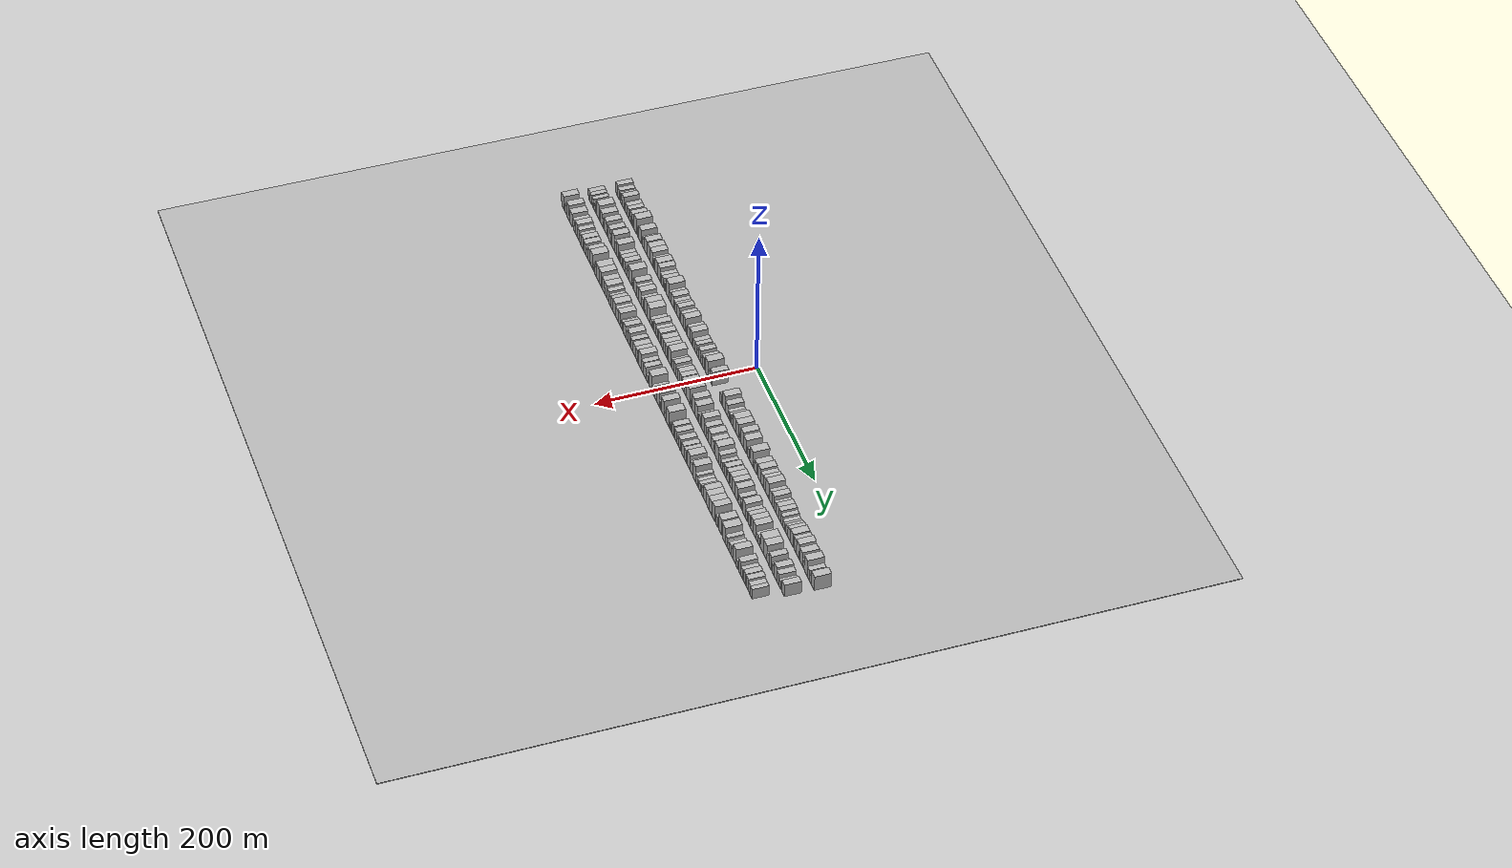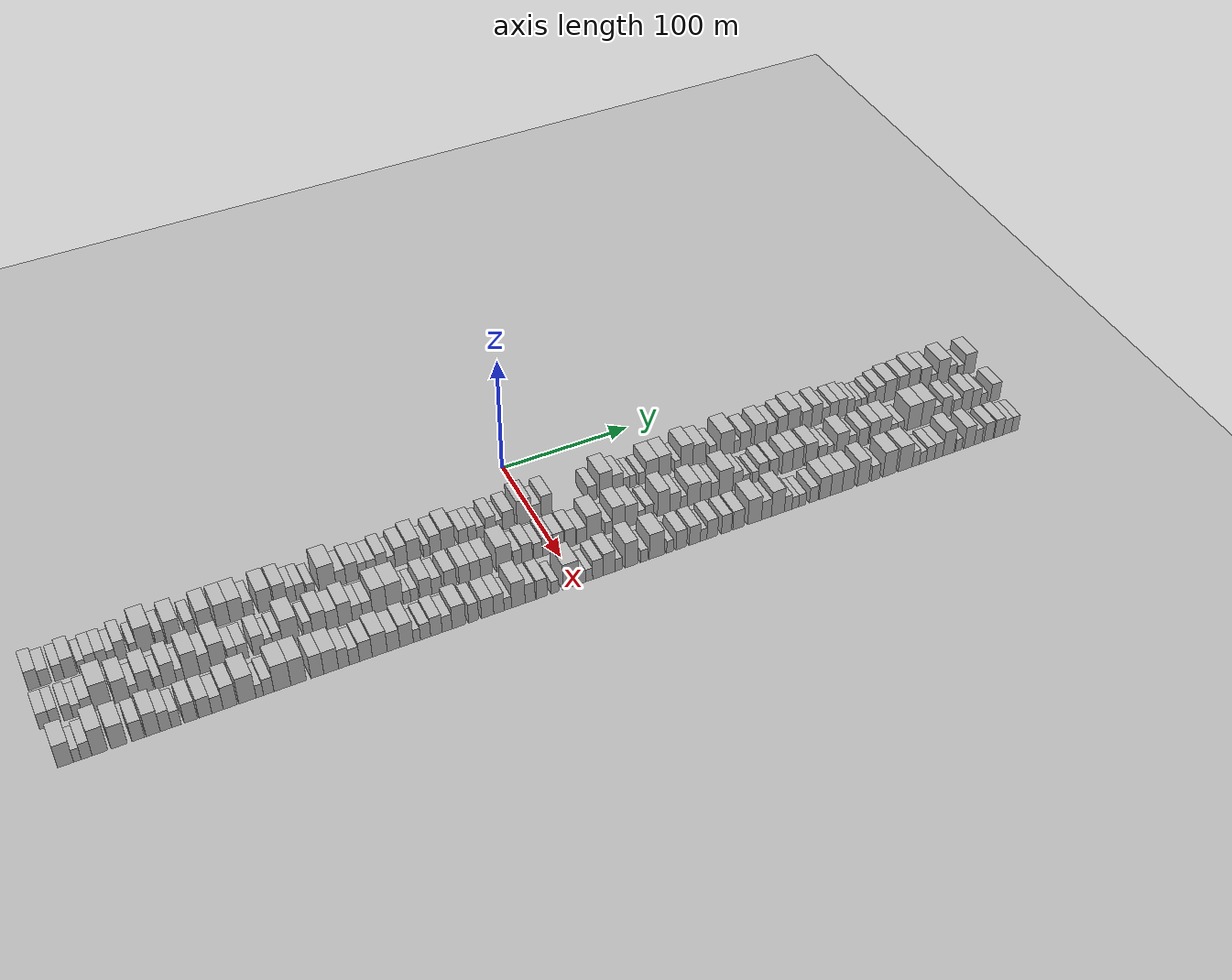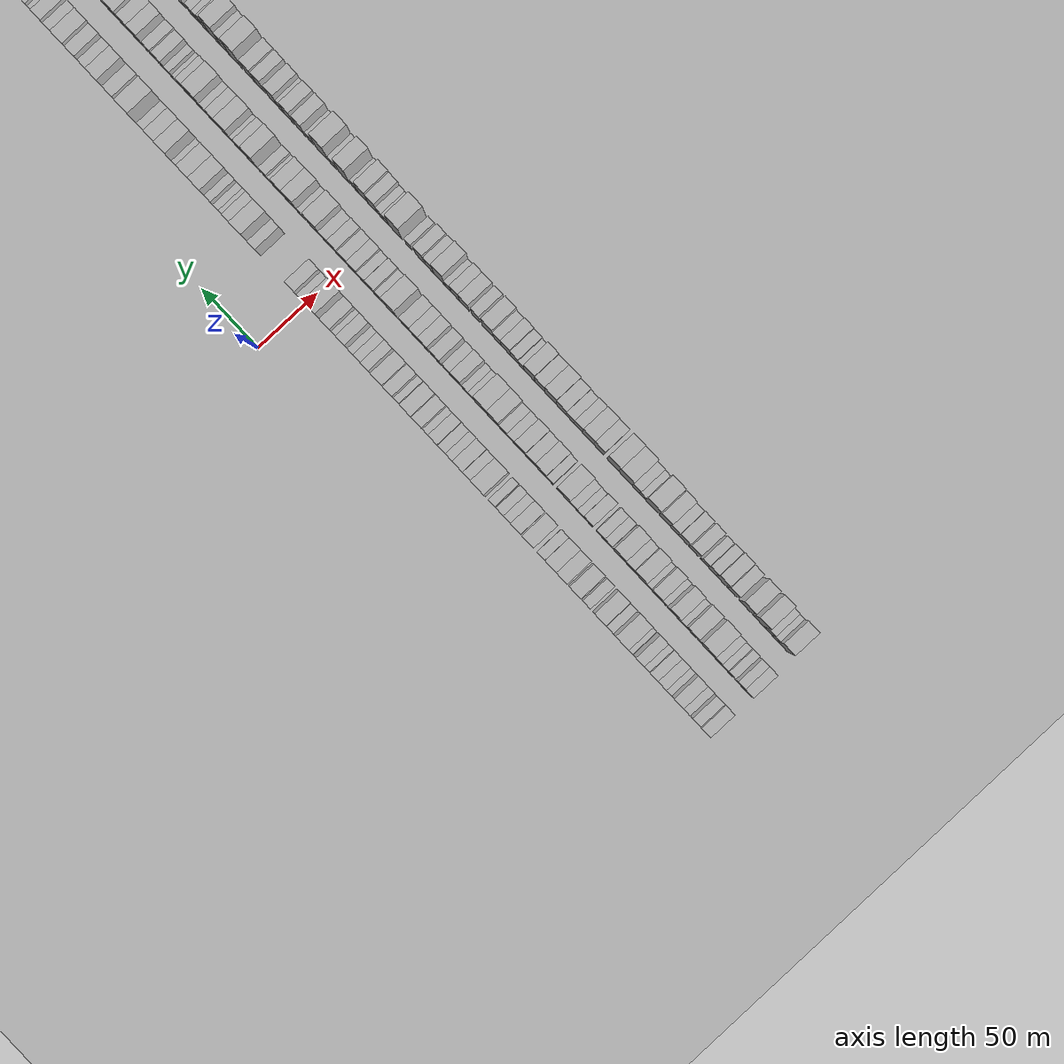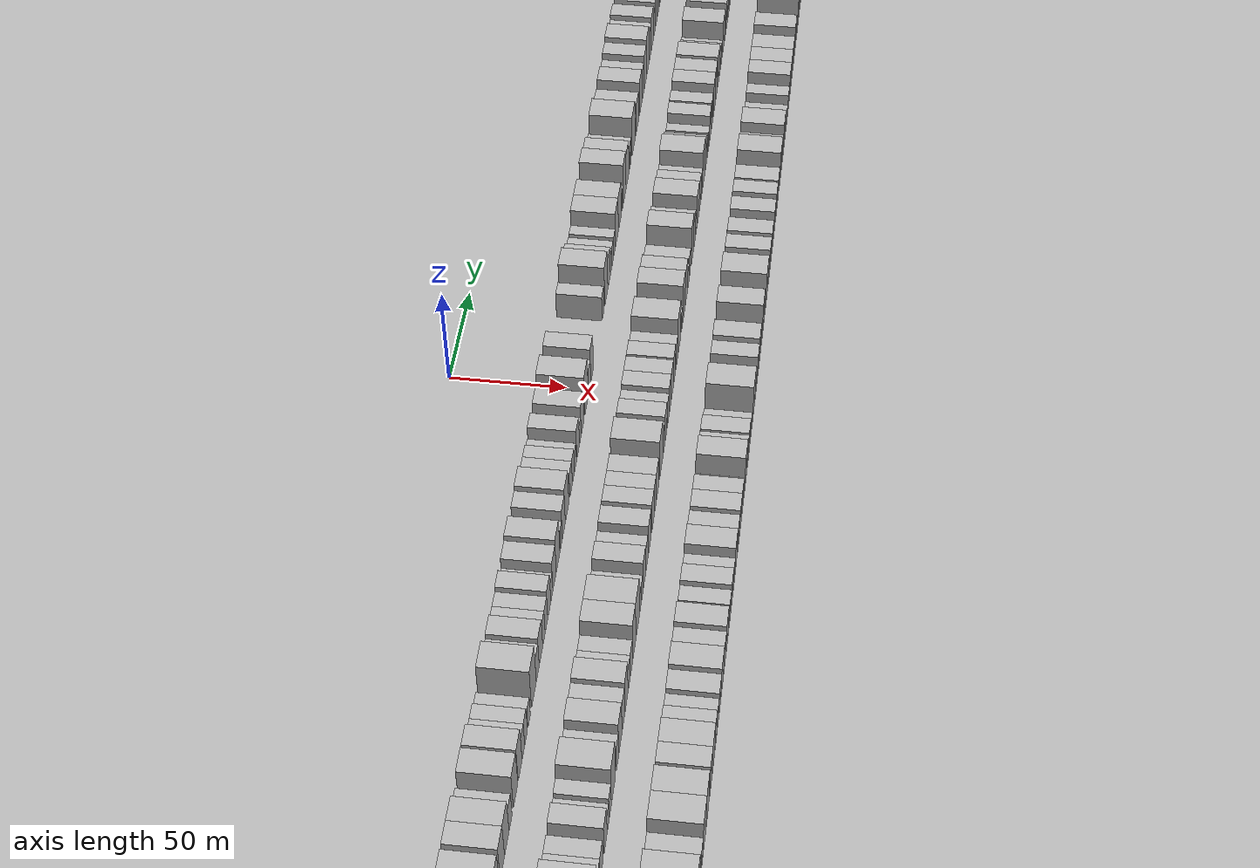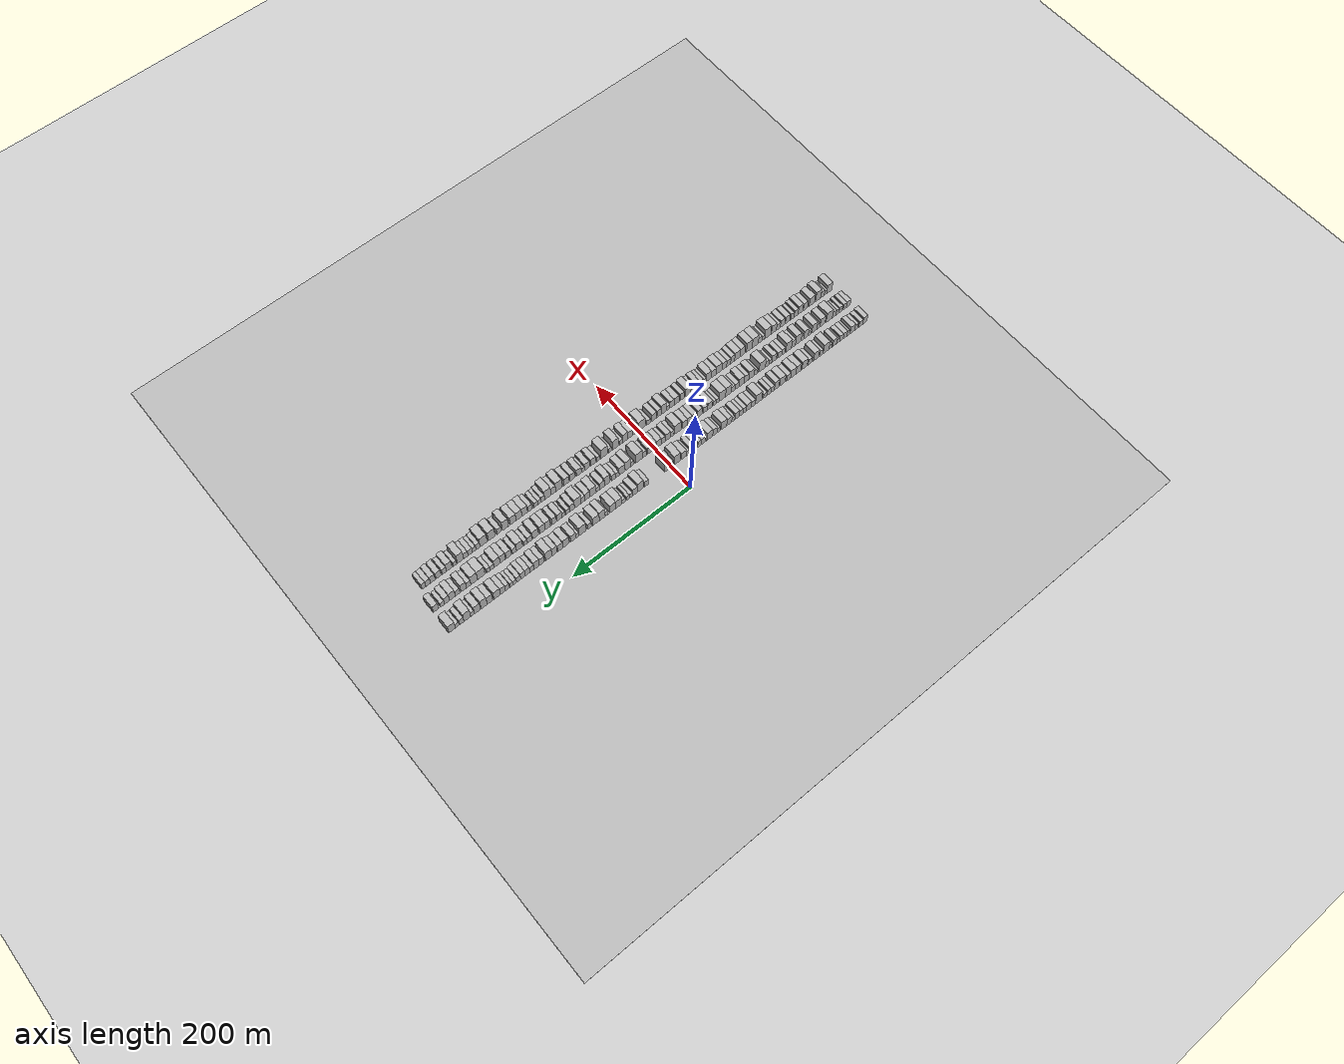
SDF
<?xml version="1.0" encoding="utf-8"?>

<sdf version="1.6">

   <world name="default">

      <gui fullscreen="0">

         <camera name="user_camera">

            <pose>-15 0 4.57585 0 0 0</pose>

            <view_controller>orbit</view_controller>

         </camera>

      </gui>

      <scene>

         <sky>

           <clouds>

             <speed>12</speed>

           </clouds>

         </sky>

         <ambient>0.4 0.4 0.4 1</ambient>

         <background>0.7 0.7 0.7 1</background>

         <shadows>1</shadows>

      </scene>

      <gravity>0 0 -9.8066</gravity>

      <magnetic_field>6e-06 2.3e-05 -4.2e-05</magnetic_field>

      <physics default="0" name="default_physics" type="ode">

         <ode>

            <solver>

               <type>quick</type>

               <iters>10</iters>

               <sor>1.0</sor>

               <use_dynamic_moi_rescaling>0</use_dynamic_moi_rescaling>

            </solver>

            <constraints>

               <cfm>0</cfm>

               <erp>0.2</erp>

               <contact_max_correcting_vel>100</contact_max_correcting_vel>

               <contact_surface_layer>0.001</contact_surface_layer>

            </constraints>

         </ode>

         <max_step_size>0.004</max_step_size>

         <real_time_factor>1</real_time_factor>

         <real_time_update_rate>250</real_time_update_rate>

      </physics>

      <light name="sun" type="directional">

         <cast_shadows>1</cast_shadows>

         <pose>0 0 10 0 0 0</pose>

         <diffuse>0.8 0.8 0.8 1</diffuse>

         <specular>0.2 0.2 0.2 1</specular>

         <attenuation>

            <range>1000</range>

            <constant>0.9</constant>

            <linear>0.01</linear>

            <quadratic>0.001</quadratic>

         </attenuation>

         <direction>-0.5 0.1 -0.9</direction>

      </light>

      <include>

         <name>ground_plane_1</name>

         <uri>model://HANNAS_ground_plane</uri>

         <pose>0 0 0  0 0 0</pose>

      </include>

      <include>

         <name>ground_plane_2</name>

         <uri>model://HANNAS_ground_plane</uri>

         <pose>100 0 0  0 0 0</pose>

      </include>

      <model name="building_1">

         <static>1</static>

         <pose frame="">50.0000 -355.0018 0 0.000000 0.000000 0.000000</pose>

         <link name="link">

            <pose frame="">0 0 9.00 0 0 0</pose>

            <collision name="collision">

               <geometry>

                  <box>

                     <size>20.0000 7.9964 18.0000</size>

                  </box>

               </geometry>

               <max_contacts>10</max_contacts>

               <surface>

                  <contact>

                     <ode/>

                  </contact>

                  <bounce/>

                  <friction>

                     <torsional>

                        <ode/>

                     </torsional>

                     <ode/>

                  </friction>

               </surface>

            </collision>

            <visual name="visual">

               <cast_shadows>0</cast_shadows>

               <geometry>

                  <box>

                     <size>20.0000 7.9964 18.0000</size>

                  </box>

               </geometry>

               <material>

                  <script>

                     <uri>model://HANNAS_wall/materials/scripts</uri>

                     <uri>model://HANNAS_wall/materials/textures</uri>

                     <name>vrc/HANNAS_wall</name>

                  </script>

               </material>

            </visual>

            <self_collide>0</self_collide>

            <enable_wind>0</enable_wind>

            <kinematic>0</kinematic>

         </link>

      </model>

      <model name="building_2">

         <static>1</static>

         <pose frame="">50.0000 -347.3747 0 0.000000 0.000000 0.000000</pose>

         <link name="link">

            <pose frame="">0 0 7.50 0 0 0</pose>

            <collision name="collision">

               <geometry>

                  <box>

                     <size>20.0000 7.2579 15.0000</size>

                  </box>

               </geometry>

               <max_contacts>10</max_contacts>

               <surface>

                  <contact>

                     <ode/>

                  </contact>

                  <bounce/>

                  <friction>

                     <torsional>

                        <ode/>

                     </torsional>

                     <ode/>

                  </friction>

               </surface>

            </collision>

            <visual name="visual">

               <cast_shadows>0</cast_shadows>

               <geometry>

                  <box>

                     <size>20.0000 7.2579 15.0000</size>

                  </box>

               </geometry>

               <material>

                  <script>

                     <uri>model://HANNAS_wall/materials/scripts</uri>

                     <uri>model://HANNAS_wall/materials/textures</uri>

                     <name>vrc/HANNAS_wall</name>

                  </script>

               </material>

            </visual>

            <self_collide>0</self_collide>

            <enable_wind>0</enable_wind>

            <kinematic>0</kinematic>

         </link>

      </model>

      <model name="building_3">

         <static>1</static>

         <pose frame="">50.0000 -338.5936 0 0.000000 0.000000 0.000000</pose>

         <link name="link">

            <pose frame="">0 0 7.50 0 0 0</pose>

            <collision name="collision">

               <geometry>

                  <box>

                     <size>20.0000 6.3044 15.0000</size>

                  </box>

               </geometry>

               <max_contacts>10</max_contacts>

               <surface>

                  <contact>

                     <ode/>

                  </contact>

                  <bounce/>

                  <friction>

                     <torsional>

                        <ode/>

                     </torsional>

                     <ode/>

                  </friction>

               </surface>

            </collision>

            <visual name="visual">

               <cast_shadows>0</cast_shadows>

               <geometry>

                  <box>

                     <size>20.0000 6.3044 15.0000</size>

                  </box>

               </geometry>

               <material>

                  <script>

                     <uri>model://HANNAS_wall/materials/scripts</uri>

                     <uri>model://HANNAS_wall/materials/textures</uri>

                     <name>vrc/HANNAS_wall</name>

                  </script>

               </material>

            </visual>

            <self_collide>0</self_collide>

            <enable_wind>0</enable_wind>

            <kinematic>0</kinematic>

         </link>

      </model>

      <model name="building_4">

         <static>1</static>

         <pose frame="">50.0000 -331.2195 0 0.000000 0.000000 0.000000</pose>

         <link name="link">

            <pose frame="">0 0 9.00 0 0 0</pose>

            <collision name="collision">

               <geometry>

                  <box>

                     <size>20.0000 8.4436 18.0000</size>

                  </box>

               </geometry>

               <max_contacts>10</max_contacts>

               <surface>

                  <contact>

                     <ode/>

                  </contact>

                  <bounce/>

                  <friction>

                     <torsional>

                        <ode/>

                     </torsional>

                     <ode/>

                  </friction>

               </surface>

            </collision>

            <visual name="visual">

               <cast_shadows>0</cast_shadows>

               <geometry>

                  <box>

                     <size>20.0000 8.4436 18.0000</size>

                  </box>

               </geometry>

               <material>

                  <script>

                     <uri>model://HANNAS_wall/materials/scripts</uri>

                     <uri>model://HANNAS_wall/materials/textures</uri>

                     <name>vrc/HANNAS_wall</name>

                  </script>

               </material>

            </visual>

            <self_collide>0</self_collide>

            <enable_wind>0</enable_wind>

            <kinematic>0</kinematic>

         </link>

      </model>

      <model name="building_5">

         <static>1</static>

         <pose frame="">50.0000 -323.4171 0 0.000000 0.000000 0.000000</pose>

         <link name="link">

            <pose frame="">0 0 6.00 0 0 0</pose>

            <collision name="collision">

               <geometry>

                  <box>

                     <size>20.0000 5.1612 12.0000</size>

                  </box>

               </geometry>

               <max_contacts>10</max_contacts>

               <surface>

                  <contact>

                     <ode/>

                  </contact>

                  <bounce/>

                  <friction>

                     <torsional>

                        <ode/>

                     </torsional>

                     <ode/>

                  </friction>

               </surface>

            </collision>

            <visual name="visual">

               <cast_shadows>0</cast_shadows>

               <geometry>

                  <box>

                     <size>20.0000 5.1612 12.0000</size>

                  </box>

               </geometry>

               <material>

                  <script>

                     <uri>model://HANNAS_wall/materials/scripts</uri>

                     <uri>model://HANNAS_wall/materials/textures</uri>

                     <name>vrc/HANNAS_wall</name>

                  </script>

               </material>

            </visual>

            <self_collide>0</self_collide>

            <enable_wind>0</enable_wind>

            <kinematic>0</kinematic>

         </link>

      </model>

      <model name="building_6">

         <static>1</static>

         <pose frame="">50.0000 -317.2213 0 0.000000 0.000000 0.000000</pose>

         <link name="link">

            <pose frame="">0 0 7.50 0 0 0</pose>

            <collision name="collision">

               <geometry>

                  <box>

                     <size>20.0000 7.2306 15.0000</size>

                  </box>

               </geometry>

               <max_contacts>10</max_contacts>

               <surface>

                  <contact>

                     <ode/>

                  </contact>

                  <bounce/>

                  <friction>

                     <torsional>

                        <ode/>

                     </torsional>

                     <ode/>

                  </friction>

               </surface>

            </collision>

            <visual name="visual">

               <cast_shadows>0</cast_shadows>

               <geometry>

                  <box>

                     <size>20.0000 7.2306 15.0000</size>

                  </box>

               </geometry>

               <material>

                  <script>

                     <uri>model://HANNAS_wall/materials/scripts</uri>

                     <uri>model://HANNAS_wall/materials/textures</uri>

                     <name>vrc/HANNAS_wall</name>

                  </script>

               </material>

            </visual>

            <self_collide>0</self_collide>

            <enable_wind>0</enable_wind>

            <kinematic>0</kinematic>

         </link>

      </model>

      <model name="building_7">

         <static>1</static>

         <pose frame="">50.0000 -310.0777 0 0.000000 0.000000 0.000000</pose>

         <link name="link">

            <pose frame="">0 0 7.50 0 0 0</pose>

            <collision name="collision">

               <geometry>

                  <box>

                     <size>20.0000 7.0565 15.0000</size>

                  </box>

               </geometry>

               <max_contacts>10</max_contacts>

               <surface>

                  <contact>

                     <ode/>

                  </contact>

                  <bounce/>

                  <friction>

                     <torsional>

                        <ode/>

                     </torsional>

                     <ode/>

                  </friction>

               </surface>

            </collision>

            <visual name="visual">

               <cast_shadows>0</cast_shadows>

               <geometry>

                  <box>

                     <size>20.0000 7.0565 15.0000</size>

                  </box>

               </geometry>

               <material>

                  <script>

                     <uri>model://HANNAS_wall/materials/scripts</uri>

                     <uri>model://HANNAS_wall/materials/textures</uri>

                     <name>vrc/HANNAS_wall</name>

                  </script>

               </material>

            </visual>

            <self_collide>0</self_collide>

            <enable_wind>0</enable_wind>

            <kinematic>0</kinematic>

         </link>

      </model>

      <model name="building_8">

         <static>1</static>

         <pose frame="">50.0000 -303.8232 0 0.000000 0.000000 0.000000</pose>

         <link name="link">

            <pose frame="">0 0 6.00 0 0 0</pose>

            <collision name="collision">

               <geometry>

                  <box>

                     <size>20.0000 5.4526 12.0000</size>

                  </box>

               </geometry>

               <max_contacts>10</max_contacts>

               <surface>

                  <contact>

                     <ode/>

                  </contact>

                  <bounce/>

                  <friction>

                     <torsional>

                        <ode/>

                     </torsional>

                     <ode/>

                  </friction>

               </surface>

            </collision>

            <visual name="visual">

               <cast_shadows>0</cast_shadows>

               <geometry>

                  <box>

                     <size>20.0000 5.4526 12.0000</size>

                  </box>

               </geometry>

               <material>

                  <script>

                     <uri>model://HANNAS_wall/materials/scripts</uri>

                     <uri>model://HANNAS_wall/materials/textures</uri>

                     <name>vrc/HANNAS_wall</name>

                  </script>

               </material>

            </visual>

            <self_collide>0</self_collide>

            <enable_wind>0</enable_wind>

            <kinematic>0</kinematic>

         </link>

      </model>

      <model name="building_9">

         <static>1</static>

         <pose frame="">50.0000 -297.4114 0 0.000000 0.000000 0.000000</pose>

         <link name="link">

            <pose frame="">0 0 9.00 0 0 0</pose>

            <collision name="collision">

               <geometry>

                  <box>

                     <size>20.0000 7.3710 18.0000</size>

                  </box>

               </geometry>

               <max_contacts>10</max_contacts>

               <surface>

                  <contact>

                     <ode/>

                  </contact>

                  <bounce/>

                  <friction>

                     <torsional>

                        <ode/>

                     </torsional>

                     <ode/>

                  </friction>

               </surface>

            </collision>

            <visual name="visual">

               <cast_shadows>0</cast_shadows>

               <geometry>

                  <box>

                     <size>20.0000 7.3710 18.0000</size>

                  </box>

               </geometry>

               <material>

                  <script>

                     <uri>model://HANNAS_wall/materials/scripts</uri>

                     <uri>model://HANNAS_wall/materials/textures</uri>

                     <name>vrc/HANNAS_wall</name>

                  </script>

               </material>

            </visual>

            <self_collide>0</self_collide>

            <enable_wind>0</enable_wind>

            <kinematic>0</kinematic>

         </link>

      </model>

      <model name="building_10">

         <static>1</static>

         <pose frame="">50.0000 -289.2260 0 0.000000 0.000000 0.000000</pose>

         <link name="link">

            <pose frame="">0 0 6.00 0 0 0</pose>

            <collision name="collision">

               <geometry>

                  <box>

                     <size>20.0000 4.9998 12.0000</size>

                  </box>

               </geometry>

               <max_contacts>10</max_contacts>

               <surface>

                  <contact>

                     <ode/>

                  </contact>

                  <bounce/>

                  <friction>

                     <torsional>

                        <ode/>

                     </torsional>

                     <ode/>

                  </friction>

               </surface>

            </collision>

            <visual name="visual">

               <cast_shadows>0</cast_shadows>

               <geometry>

                  <box>

                     <size>20.0000 4.9998 12.0000</size>

                  </box>

               </geometry>

               <material>

                  <script>

                     <uri>model://HANNAS_wall/materials/scripts</uri>

                     <uri>model://HANNAS_wall/materials/textures</uri>

                     <name>vrc/HANNAS_wall</name>

                  </script>

               </material>

            </visual>

            <self_collide>0</self_collide>

            <enable_wind>0</enable_wind>

            <kinematic>0</kinematic>

         </link>

      </model>

      <model name="building_11">

         <static>1</static>

         <pose frame="">50.0000 -281.0882 0 0.000000 0.000000 0.000000</pose>

         <link name="link">

            <pose frame="">0 0 12.00 0 0 0</pose>

            <collision name="collision">

               <geometry>

                  <box>

                     <size>20.0000 11.2757 24.0000</size>

                  </box>

               </geometry>

               <max_contacts>10</max_contacts>

               <surface>

                  <contact>

                     <ode/>

                  </contact>

                  <bounce/>

                  <friction>

                     <torsional>

                        <ode/>

                     </torsional>

                     <ode/>

                  </friction>

               </surface>

            </collision>

            <visual name="visual">

               <cast_shadows>0</cast_shadows>

               <geometry>

                  <box>

                     <size>20.0000 11.2757 24.0000</size>

                  </box>

               </geometry>

               <material>

                  <script>

                     <uri>model://HANNAS_wall/materials/scripts</uri>

                     <uri>model://HANNAS_wall/materials/textures</uri>

                     <name>vrc/HANNAS_wall</name>

                  </script>

               </material>

            </visual>

            <self_collide>0</self_collide>

            <enable_wind>0</enable_wind>

            <kinematic>0</kinematic>

         </link>

      </model>

      <model name="building_12">

         <static>1</static>

         <pose frame="">50.0000 -271.3896 0 0.000000 0.000000 0.000000</pose>

         <link name="link">

            <pose frame="">0 0 7.50 0 0 0</pose>

            <collision name="collision">

               <geometry>

                  <box>

                     <size>20.0000 6.1216 15.0000</size>

                  </box>

               </geometry>

               <max_contacts>10</max_contacts>

               <surface>

                  <contact>

                     <ode/>

                  </contact>

                  <bounce/>

                  <friction>

                     <torsional>

                        <ode/>

                     </torsional>

                     <ode/>

                  </friction>

               </surface>

            </collision>

            <visual name="visual">

               <cast_shadows>0</cast_shadows>

               <geometry>

                  <box>

                     <size>20.0000 6.1216 15.0000</size>

                  </box>

               </geometry>

               <material>

                  <script>

                     <uri>model://HANNAS_wall/materials/scripts</uri>

                     <uri>model://HANNAS_wall/materials/textures</uri>

                     <name>vrc/HANNAS_wall</name>

                  </script>

               </material>

            </visual>

            <self_collide>0</self_collide>

            <enable_wind>0</enable_wind>

            <kinematic>0</kinematic>

         </link>

      </model>

      <model name="building_13">

         <static>1</static>

         <pose frame="">50.0000 -262.3247 0 0.000000 0.000000 0.000000</pose>

         <link name="link">

            <pose frame="">0 0 10.50 0 0 0</pose>

            <collision name="collision">

               <geometry>

                  <box>

                     <size>20.0000 10.0081 21.0000</size>

                  </box>

               </geometry>

               <max_contacts>10</max_contacts>

               <surface>

                  <contact>

                     <ode/>

                  </contact>

                  <bounce/>

                  <friction>

                     <torsional>

                        <ode/>

                     </torsional>

                     <ode/>

                  </friction>

               </surface>

            </collision>

            <visual name="visual">

               <cast_shadows>0</cast_shadows>

               <geometry>

                  <box>

                     <size>20.0000 10.0081 21.0000</size>

                  </box>

               </geometry>

               <material>

                  <script>

                     <uri>model://HANNAS_wall/materials/scripts</uri>

                     <uri>model://HANNAS_wall/materials/textures</uri>

                     <name>vrc/HANNAS_wall</name>

                  </script>

               </material>

            </visual>

            <self_collide>0</self_collide>

            <enable_wind>0</enable_wind>

            <kinematic>0</kinematic>

         </link>

      </model>

      <model name="building_14">

         <static>1</static>

         <pose frame="">50.0000 -250.9115 0 0.000000 0.000000 0.000000</pose>

         <link name="link">

            <pose frame="">0 0 7.50 0 0 0</pose>

            <collision name="collision">

               <geometry>

                  <box>

                     <size>20.0000 6.8184 15.0000</size>

                  </box>

               </geometry>

               <max_contacts>10</max_contacts>

               <surface>

                  <contact>

                     <ode/>

                  </contact>

                  <bounce/>

                  <friction>

                     <torsional>

                        <ode/>

                     </torsional>

                     <ode/>

                  </friction>

               </surface>

            </collision>

            <visual name="visual">

               <cast_shadows>0</cast_shadows>

               <geometry>

                  <box>

                     <size>20.0000 6.8184 15.0000</size>

                  </box>

               </geometry>

               <material>

                  <script>

                     <uri>model://HANNAS_wall/materials/scripts</uri>

                     <uri>model://HANNAS_wall/materials/textures</uri>

                     <name>vrc/HANNAS_wall</name>

                  </script>

               </material>

            </visual>

            <self_collide>0</self_collide>

            <enable_wind>0</enable_wind>

            <kinematic>0</kinematic>

         </link>

      </model>

      <model name="building_15">

         <static>1</static>

         <pose frame="">50.0000 -240.5385 0 0.000000 0.000000 0.000000</pose>

         <link name="link">

            <pose frame="">0 0 10.50 0 0 0</pose>

            <collision name="collision">

               <geometry>

                  <box>

                     <size>20.0000 9.9277 21.0000</size>

                  </box>

               </geometry>

               <max_contacts>10</max_contacts>

               <surface>

                  <contact>

                     <ode/>

                  </contact>

                  <bounce/>

                  <friction>

                     <torsional>

                        <ode/>

                     </torsional>

                     <ode/>

                  </friction>

               </surface>

            </collision>

            <visual name="visual">

               <cast_shadows>0</cast_shadows>

               <geometry>

                  <box>

                     <size>20.0000 9.9277 21.0000</size>

                  </box>

               </geometry>

               <material>

                  <script>

                     <uri>model://HANNAS_wall/materials/scripts</uri>

                     <uri>model://HANNAS_wall/materials/textures</uri>

                     <name>vrc/HANNAS_wall</name>

                  </script>

               </material>

            </visual>

            <self_collide>0</self_collide>

            <enable_wind>0</enable_wind>

            <kinematic>0</kinematic>

         </link>

      </model>

      <model name="building_16">

         <static>1</static>

         <pose frame="">50.0000 -228.8599 0 0.000000 0.000000 0.000000</pose>

         <link name="link">

            <pose frame="">0 0 10.50 0 0 0</pose>

            <collision name="collision">

               <geometry>

                  <box>

                     <size>20.0000 9.4294 21.0000</size>

                  </box>

               </geometry>

               <max_contacts>10</max_contacts>

               <surface>

                  <contact>

                     <ode/>

                  </contact>

                  <bounce/>

                  <friction>

                     <torsional>

                        <ode/>

                     </torsional>

                     <ode/>

                  </friction>

               </surface>

            </collision>

            <visual name="visual">

               <cast_shadows>0</cast_shadows>

               <geometry>

                  <box>

                     <size>20.0000 9.4294 21.0000</size>

                  </box>

               </geometry>

               <material>

                  <script>

                     <uri>model://HANNAS_wall/materials/scripts</uri>

                     <uri>model://HANNAS_wall/materials/textures</uri>

                     <name>vrc/HANNAS_wall</name>

                  </script>

               </material>

            </visual>

            <self_collide>0</self_collide>

            <enable_wind>0</enable_wind>

            <kinematic>0</kinematic>

         </link>

      </model>

      <model name="building_17">

         <static>1</static>

         <pose frame="">50.0000 -219.2038 0 0.000000 0.000000 0.000000</pose>

         <link name="link">

            <pose frame="">0 0 10.50 0 0 0</pose>

            <collision name="collision">

               <geometry>

                  <box>

                     <size>20.0000 9.8827 21.0000</size>

                  </box>

               </geometry>

               <max_contacts>10</max_contacts>

               <surface>

                  <contact>

                     <ode/>

                  </contact>

                  <bounce/>

                  <friction>

                     <torsional>

                        <ode/>

                     </torsional>

                     <ode/>

                  </friction>

               </surface>

            </collision>

            <visual name="visual">

               <cast_shadows>0</cast_shadows>

               <geometry>

                  <box>

                     <size>20.0000 9.8827 21.0000</size>

                  </box>

               </geometry>

               <material>

                  <script>

                     <uri>model://HANNAS_wall/materials/scripts</uri>

                     <uri>model://HANNAS_wall/materials/textures</uri>

                     <name>vrc/HANNAS_wall</name>

                  </script>

               </material>

            </visual>

            <self_collide>0</self_collide>

            <enable_wind>0</enable_wind>

            <kinematic>0</kinematic>

         </link>

      </model>

      <model name="building_18">

         <static>1</static>

         <pose frame="">50.0000 -210.8104 0 0.000000 0.000000 0.000000</pose>

         <link name="link">

            <pose frame="">0 0 7.50 0 0 0</pose>

            <collision name="collision">

               <geometry>

                  <box>

                     <size>20.0000 6.9042 15.0000</size>

                  </box>

               </geometry>

               <max_contacts>10</max_contacts>

               <surface>

                  <contact>

                     <ode/>

                  </contact>

                  <bounce/>

                  <friction>

                     <torsional>

                        <ode/>

                     </torsional>

                     <ode/>

                  </friction>

               </surface>

            </collision>

            <visual name="visual">

               <cast_shadows>0</cast_shadows>

               <geometry>

                  <box>

                     <size>20.0000 6.9042 15.0000</size>

                  </box>

               </geometry>

               <material>

                  <script>

                     <uri>model://HANNAS_wall/materials/scripts</uri>

                     <uri>model://HANNAS_wall/materials/textures</uri>

                     <name>vrc/HANNAS_wall</name>

                  </script>

               </material>

            </visual>

            <self_collide>0</self_collide>

            <enable_wind>0</enable_wind>

            <kinematic>0</kinematic>

         </link>

      </model>

      <model name="building_19">

         <static>1</static>

         <pose frame="">50.0000 -199.2512 0 0.000000 0.000000 0.000000</pose>

         <link name="link">

            <pose frame="">0 0 10.50 0 0 0</pose>

            <collision name="collision">

               <geometry>

                  <box>

                     <size>20.0000 10.2143 21.0000</size>

                  </box>

               </geometry>

               <max_contacts>10</max_contacts>

               <surface>

                  <contact>

                     <ode/>

                  </contact>

                  <bounce/>

                  <friction>

                     <torsional>

                        <ode/>

                     </torsional>

                     <ode/>

                  </friction>

               </surface>

            </collision>

            <visual name="visual">

               <cast_shadows>0</cast_shadows>

               <geometry>

                  <box>

                     <size>20.0000 10.2143 21.0000</size>

                  </box>

               </geometry>

               <material>

                  <script>

                     <uri>model://HANNAS_wall/materials/scripts</uri>

                     <uri>model://HANNAS_wall/materials/textures</uri>

                     <name>vrc/HANNAS_wall</name>

                  </script>

               </material>

            </visual>

            <self_collide>0</self_collide>

            <enable_wind>0</enable_wind>

            <kinematic>0</kinematic>

         </link>

      </model>

      <model name="building_20">

         <static>1</static>

         <pose frame="">50.0000 -188.6568 0 0.000000 0.000000 0.000000</pose>

         <link name="link">

            <pose frame="">0 0 10.50 0 0 0</pose>

            <collision name="collision">

               <geometry>

                  <box>

                     <size>20.0000 8.9744 21.0000</size>

                  </box>

               </geometry>

               <max_contacts>10</max_contacts>

               <surface>

                  <contact>

                     <ode/>

                  </contact>

                  <bounce/>

                  <friction>

                     <torsional>

                        <ode/>

                     </torsional>

                     <ode/>

                  </friction>

               </surface>

            </collision>

            <visual name="visual">

               <cast_shadows>0</cast_shadows>

               <geometry>

                  <box>

                     <size>20.0000 8.9744 21.0000</size>

                  </box>

               </geometry>

               <material>

                  <script>

                     <uri>model://HANNAS_wall/materials/scripts</uri>

                     <uri>model://HANNAS_wall/materials/textures</uri>

                     <name>vrc/HANNAS_wall</name>

                  </script>

               </material>

            </visual>

            <self_collide>0</self_collide>

            <enable_wind>0</enable_wind>

            <kinematic>0</kinematic>

         </link>

      </model>

      <model name="building_21">

         <static>1</static>

         <pose frame="">50.0000 -181.0161 0 0.000000 0.000000 0.000000</pose>

         <link name="link">

            <pose frame="">0 0 7.50 0 0 0</pose>

            <collision name="collision">

               <geometry>

                  <box>

                     <size>20.0000 6.3071 15.0000</size>

                  </box>

               </geometry>

               <max_contacts>10</max_contacts>

               <surface>

                  <contact>

                     <ode/>

                  </contact>

                  <bounce/>

                  <friction>

                     <torsional>

                        <ode/>

                     </torsional>

                     <ode/>

                  </friction>

               </surface>

            </collision>

            <visual name="visual">

               <cast_shadows>0</cast_shadows>

               <geometry>

                  <box>

                     <size>20.0000 6.3071 15.0000</size>

                  </box>

               </geometry>

               <material>

                  <script>

                     <uri>model://HANNAS_wall/materials/scripts</uri>

                     <uri>model://HANNAS_wall/materials/textures</uri>

                     <name>vrc/HANNAS_wall</name>

                  </script>

               </material>

            </visual>

            <self_collide>0</self_collide>

            <enable_wind>0</enable_wind>

            <kinematic>0</kinematic>

         </link>

      </model>

      <model name="building_22">

         <static>1</static>

         <pose frame="">50.0000 -174.5558 0 0.000000 0.000000 0.000000</pose>

         <link name="link">

            <pose frame="">0 0 7.50 0 0 0</pose>

            <collision name="collision">

               <geometry>

                  <box>

                     <size>20.0000 6.6134 15.0000</size>

                  </box>

               </geometry>

               <max_contacts>10</max_contacts>

               <surface>

                  <contact>

                     <ode/>

                  </contact>

                  <bounce/>

                  <friction>

                     <torsional>

                        <ode/>

                     </torsional>

                     <ode/>

                  </friction>

               </surface>

            </collision>

            <visual name="visual">

               <cast_shadows>0</cast_shadows>

               <geometry>

                  <box>

                     <size>20.0000 6.6134 15.0000</size>

                  </box>

               </geometry>

               <material>

                  <script>

                     <uri>model://HANNAS_wall/materials/scripts</uri>

                     <uri>model://HANNAS_wall/materials/textures</uri>

                     <name>vrc/HANNAS_wall</name>

                  </script>

               </material>

            </visual>

            <self_collide>0</self_collide>

            <enable_wind>0</enable_wind>

            <kinematic>0</kinematic>

         </link>

      </model>

      <model name="building_23">

         <static>1</static>

         <pose frame="">50.0000 -167.2927 0 0.000000 0.000000 0.000000</pose>

         <link name="link">

            <pose frame="">0 0 6.00 0 0 0</pose>

            <collision name="collision">

               <geometry>

                  <box>

                     <size>20.0000 5.9128 12.0000</size>

                  </box>

               </geometry>

               <max_contacts>10</max_contacts>

               <surface>

                  <contact>

                     <ode/>

                  </contact>

                  <bounce/>

                  <friction>

                     <torsional>

                        <ode/>

                     </torsional>

                     <ode/>

                  </friction>

               </surface>

            </collision>

            <visual name="visual">

               <cast_shadows>0</cast_shadows>

               <geometry>

                  <box>

                     <size>20.0000 5.9128 12.0000</size>

                  </box>

               </geometry>

               <material>

                  <script>

                     <uri>model://HANNAS_wall/materials/scripts</uri>

                     <uri>model://HANNAS_wall/materials/textures</uri>

                     <name>vrc/HANNAS_wall</name>

                  </script>

               </material>

            </visual>

            <self_collide>0</self_collide>

            <enable_wind>0</enable_wind>

            <kinematic>0</kinematic>

         </link>

      </model>

      <model name="building_24">

         <static>1</static>

         <pose frame="">50.0000 -155.4569 0 0.000000 0.000000 0.000000</pose>

         <link name="link">

            <pose frame="">0 0 12.00 0 0 0</pose>

            <collision name="collision">

               <geometry>

                  <box>

                     <size>20.0000 11.7588 24.0000</size>

                  </box>

               </geometry>

               <max_contacts>10</max_contacts>

               <surface>

                  <contact>

                     <ode/>

                  </contact>

                  <bounce/>

                  <friction>

                     <torsional>

                        <ode/>

                     </torsional>

                     <ode/>

                  </friction>

               </surface>

            </collision>

            <visual name="visual">

               <cast_shadows>0</cast_shadows>

               <geometry>

                  <box>

                     <size>20.0000 11.7588 24.0000</size>

                  </box>

               </geometry>

               <material>

                  <script>

                     <uri>model://HANNAS_wall/materials/scripts</uri>

                     <uri>model://HANNAS_wall/materials/textures</uri>

                     <name>vrc/HANNAS_wall</name>

                  </script>

               </material>

            </visual>

            <self_collide>0</self_collide>

            <enable_wind>0</enable_wind>

            <kinematic>0</kinematic>

         </link>

      </model>

      <model name="building_25">

         <static>1</static>

         <pose frame="">50.0000 -145.8737 0 0.000000 0.000000 0.000000</pose>

         <link name="link">

            <pose frame="">0 0 7.50 0 0 0</pose>

            <collision name="collision">

               <geometry>

                  <box>

                     <size>20.0000 7.4076 15.0000</size>

                  </box>

               </geometry>

               <max_contacts>10</max_contacts>

               <surface>

                  <contact>

                     <ode/>

                  </contact>

                  <bounce/>

                  <friction>

                     <torsional>

                        <ode/>

                     </torsional>

                     <ode/>

                  </friction>

               </surface>

            </collision>

            <visual name="visual">

               <cast_shadows>0</cast_shadows>

               <geometry>

                  <box>

                     <size>20.0000 7.4076 15.0000</size>

                  </box>

               </geometry>

               <material>

                  <script>

                     <uri>model://HANNAS_wall/materials/scripts</uri>

                     <uri>model://HANNAS_wall/materials/textures</uri>

                     <name>vrc/HANNAS_wall</name>

                  </script>

               </material>

            </visual>

            <self_collide>0</self_collide>

            <enable_wind>0</enable_wind>

            <kinematic>0</kinematic>

         </link>

      </model>

      <model name="building_26">

         <static>1</static>

         <pose frame="">50.0000 -137.6836 0 0.000000 0.000000 0.000000</pose>

         <link name="link">

            <pose frame="">0 0 9.00 0 0 0</pose>

            <collision name="collision">

               <geometry>

                  <box>

                     <size>20.0000 8.9725 18.0000</size>

                  </box>

               </geometry>

               <max_contacts>10</max_contacts>

               <surface>

                  <contact>

                     <ode/>

                  </contact>

                  <bounce/>

                  <friction>

                     <torsional>

                        <ode/>

                     </torsional>

                     <ode/>

                  </friction>

               </surface>

            </collision>

            <visual name="visual">

               <cast_shadows>0</cast_shadows>

               <geometry>

                  <box>

                     <size>20.0000 8.9725 18.0000</size>

                  </box>

               </geometry>

               <material>

                  <script>

                     <uri>model://HANNAS_wall/materials/scripts</uri>

                     <uri>model://HANNAS_wall/materials/textures</uri>

                     <name>vrc/HANNAS_wall</name>

                  </script>

               </material>

            </visual>

            <self_collide>0</self_collide>

            <enable_wind>0</enable_wind>

            <kinematic>0</kinematic>

         </link>

      </model>

      <model name="building_27">

         <static>1</static>

         <pose frame="">50.0000 -130.0861 0 0.000000 0.000000 0.000000</pose>

         <link name="link">

            <pose frame="">0 0 7.50 0 0 0</pose>

            <collision name="collision">

               <geometry>

                  <box>

                     <size>20.0000 6.2227 15.0000</size>

                  </box>

               </geometry>

               <max_contacts>10</max_contacts>

               <surface>

                  <contact>

                     <ode/>

                  </contact>

                  <bounce/>

                  <friction>

                     <torsional>

                        <ode/>

                     </torsional>

                     <ode/>

                  </friction>

               </surface>

            </collision>

            <visual name="visual">

               <cast_shadows>0</cast_shadows>

               <geometry>

                  <box>

                     <size>20.0000 6.2227 15.0000</size>

                  </box>

               </geometry>

               <material>

                  <script>

                     <uri>model://HANNAS_wall/materials/scripts</uri>

                     <uri>model://HANNAS_wall/materials/textures</uri>

                     <name>vrc/HANNAS_wall</name>

                  </script>

               </material>

            </visual>

            <self_collide>0</self_collide>

            <enable_wind>0</enable_wind>

            <kinematic>0</kinematic>

         </link>

      </model>

      <model name="building_28">

         <static>1</static>

         <pose frame="">50.0000 -123.5246 0 0.000000 0.000000 0.000000</pose>

         <link name="link">

            <pose frame="">0 0 7.50 0 0 0</pose>

            <collision name="collision">

               <geometry>

                  <box>

                     <size>20.0000 6.9003 15.0000</size>

                  </box>

               </geometry>

               <max_contacts>10</max_contacts>

               <surface>

                  <contact>

                     <ode/>

                  </contact>

                  <bounce/>

                  <friction>

                     <torsional>

                        <ode/>

                     </torsional>

                     <ode/>

                  </friction>

               </surface>

            </collision>

            <visual name="visual">

               <cast_shadows>0</cast_shadows>

               <geometry>

                  <box>

                     <size>20.0000 6.9003 15.0000</size>

                  </box>

               </geometry>

               <material>

                  <script>

                     <uri>model://HANNAS_wall/materials/scripts</uri>

                     <uri>model://HANNAS_wall/materials/textures</uri>

                     <name>vrc/HANNAS_wall</name>

                  </script>

               </material>

            </visual>

            <self_collide>0</self_collide>

            <enable_wind>0</enable_wind>

            <kinematic>0</kinematic>

         </link>

      </model>

      <model name="building_29">

         <static>1</static>

         <pose frame="">50.0000 -116.0841 0 0.000000 0.000000 0.000000</pose>

         <link name="link">

            <pose frame="">0 0 9.00 0 0 0</pose>

            <collision name="collision">

               <geometry>

                  <box>

                     <size>20.0000 7.9808 18.0000</size>

                  </box>

               </geometry>

               <max_contacts>10</max_contacts>

               <surface>

                  <contact>

                     <ode/>

                  </contact>

                  <bounce/>

                  <friction>

                     <torsional>

                        <ode/>

                     </torsional>

                     <ode/>

                  </friction>

               </surface>

            </collision>

            <visual name="visual">

               <cast_shadows>0</cast_shadows>

               <geometry>

                  <box>

                     <size>20.0000 7.9808 18.0000</size>

                  </box>

               </geometry>

               <material>

                  <script>

                     <uri>model://HANNAS_wall/materials/scripts</uri>

                     <uri>model://HANNAS_wall/materials/textures</uri>

                     <name>vrc/HANNAS_wall</name>

                  </script>

               </material>

            </visual>

            <self_collide>0</self_collide>

            <enable_wind>0</enable_wind>

            <kinematic>0</kinematic>

         </link>

      </model>

      <model name="building_30">

         <static>1</static>

         <pose frame="">50.0000 -109.2844 0 0.000000 0.000000 0.000000</pose>

         <link name="link">

            <pose frame="">0 0 6.00 0 0 0</pose>

            <collision name="collision">

               <geometry>

                  <box>

                     <size>20.0000 5.6186 12.0000</size>

                  </box>

               </geometry>

               <max_contacts>10</max_contacts>

               <surface>

                  <contact>

                     <ode/>

                  </contact>

                  <bounce/>

                  <friction>

                     <torsional>

                        <ode/>

                     </torsional>

                     <ode/>

                  </friction>

               </surface>

            </collision>

            <visual name="visual">

               <cast_shadows>0</cast_shadows>

               <geometry>

                  <box>

                     <size>20.0000 5.6186 12.0000</size>

                  </box>

               </geometry>

               <material>

                  <script>

                     <uri>model://HANNAS_wall/materials/scripts</uri>

                     <uri>model://HANNAS_wall/materials/textures</uri>

                     <name>vrc/HANNAS_wall</name>

                  </script>

               </material>

            </visual>

            <self_collide>0</self_collide>

            <enable_wind>0</enable_wind>

            <kinematic>0</kinematic>

         </link>

      </model>

      <model name="building_31">

         <static>1</static>

         <pose frame="">50.0000 -101.9850 0 0.000000 0.000000 0.000000</pose>

         <link name="link">

            <pose frame="">0 0 9.00 0 0 0</pose>

            <collision name="collision">

               <geometry>

                  <box>

                     <size>20.0000 8.9801 18.0000</size>

                  </box>

               </geometry>

               <max_contacts>10</max_contacts>

               <surface>

                  <contact>

                     <ode/>

                  </contact>

                  <bounce/>

                  <friction>

                     <torsional>

                        <ode/>

                     </torsional>

                     <ode/>

                  </friction>

               </surface>

            </collision>

            <visual name="visual">

               <cast_shadows>0</cast_shadows>

               <geometry>

                  <box>

                     <size>20.0000 8.9801 18.0000</size>

                  </box>

               </geometry>

               <material>

                  <script>

                     <uri>model://HANNAS_wall/materials/scripts</uri>

                     <uri>model://HANNAS_wall/materials/textures</uri>

                     <name>vrc/HANNAS_wall</name>

                  </script>

               </material>

            </visual>

            <self_collide>0</self_collide>

            <enable_wind>0</enable_wind>

            <kinematic>0</kinematic>

         </link>

      </model>

      <model name="building_32">

         <static>1</static>

         <pose frame="">50.0000 -92.5490 0 0.000000 0.000000 0.000000</pose>

         <link name="link">

            <pose frame="">0 0 10.50 0 0 0</pose>

            <collision name="collision">

               <geometry>

                  <box>

                     <size>20.0000 9.8919 21.0000</size>

                  </box>

               </geometry>

               <max_contacts>10</max_contacts>

               <surface>

                  <contact>

                     <ode/>

                  </contact>

                  <bounce/>

                  <friction>

                     <torsional>

                        <ode/>

                     </torsional>

                     <ode/>

                  </friction>

               </surface>

            </collision>

            <visual name="visual">

               <cast_shadows>0</cast_shadows>

               <geometry>

                  <box>

                     <size>20.0000 9.8919 21.0000</size>

                  </box>

               </geometry>

               <material>

                  <script>

                     <uri>model://HANNAS_wall/materials/scripts</uri>

                     <uri>model://HANNAS_wall/materials/textures</uri>

                     <name>vrc/HANNAS_wall</name>

                  </script>

               </material>

            </visual>

            <self_collide>0</self_collide>

            <enable_wind>0</enable_wind>

            <kinematic>0</kinematic>

         </link>

      </model>

      <model name="building_33">

         <static>1</static>

         <pose frame="">50.0000 -83.1782 0 0.000000 0.000000 0.000000</pose>

         <link name="link">

            <pose frame="">0 0 6.00 0 0 0</pose>

            <collision name="collision">

               <geometry>

                  <box>

                     <size>20.0000 4.8496 12.0000</size>

                  </box>

               </geometry>

               <max_contacts>10</max_contacts>

               <surface>

                  <contact>

                     <ode/>

                  </contact>

                  <bounce/>

                  <friction>

                     <torsional>

                        <ode/>

                     </torsional>

                     <ode/>

                  </friction>

               </surface>

            </collision>

            <visual name="visual">

               <cast_shadows>0</cast_shadows>

               <geometry>

                  <box>

                     <size>20.0000 4.8496 12.0000</size>

                  </box>

               </geometry>

               <material>

                  <script>

                     <uri>model://HANNAS_wall/materials/scripts</uri>

                     <uri>model://HANNAS_wall/materials/textures</uri>

                     <name>vrc/HANNAS_wall</name>

                  </script>

               </material>

            </visual>

            <self_collide>0</self_collide>

            <enable_wind>0</enable_wind>

            <kinematic>0</kinematic>

         </link>

      </model>

      <model name="building_34">

         <static>1</static>

         <pose frame="">50.0000 -76.5989 0 0.000000 0.000000 0.000000</pose>

         <link name="link">

            <pose frame="">0 0 9.00 0 0 0</pose>

            <collision name="collision">

               <geometry>

                  <box>

                     <size>20.0000 8.3091 18.0000</size>

                  </box>

               </geometry>

               <max_contacts>10</max_contacts>

               <surface>

                  <contact>

                     <ode/>

                  </contact>

                  <bounce/>

                  <friction>

                     <torsional>

                        <ode/>

                     </torsional>

                     <ode/>

                  </friction>

               </surface>

            </collision>

            <visual name="visual">

               <cast_shadows>0</cast_shadows>

               <geometry>

                  <box>

                     <size>20.0000 8.3091 18.0000</size>

                  </box>

               </geometry>

               <material>

                  <script>

                     <uri>model://HANNAS_wall/materials/scripts</uri>

                     <uri>model://HANNAS_wall/materials/textures</uri>

                     <name>vrc/HANNAS_wall</name>

                  </script>

               </material>

            </visual>

            <self_collide>0</self_collide>

            <enable_wind>0</enable_wind>

            <kinematic>0</kinematic>

         </link>

      </model>

      <model name="building_35">

         <static>1</static>

         <pose frame="">50.0000 -67.3778 0 0.000000 0.000000 0.000000</pose>

         <link name="link">

            <pose frame="">0 0 10.50 0 0 0</pose>

            <collision name="collision">

               <geometry>

                  <box>

                     <size>20.0000 10.1330 21.0000</size>

                  </box>

               </geometry>

               <max_contacts>10</max_contacts>

               <surface>

                  <contact>

                     <ode/>

                  </contact>

                  <bounce/>

                  <friction>

                     <torsional>

                        <ode/>

                     </torsional>

                     <ode/>

                  </friction>

               </surface>

            </collision>

            <visual name="visual">

               <cast_shadows>0</cast_shadows>

               <geometry>

                  <box>

                     <size>20.0000 10.1330 21.0000</size>

                  </box>

               </geometry>

               <material>

                  <script>

                     <uri>model://HANNAS_wall/materials/scripts</uri>

                     <uri>model://HANNAS_wall/materials/textures</uri>

                     <name>vrc/HANNAS_wall</name>

                  </script>

               </material>

            </visual>

            <self_collide>0</self_collide>

            <enable_wind>0</enable_wind>

            <kinematic>0</kinematic>

         </link>

      </model>

      <model name="building_36">

         <static>1</static>

         <pose frame="">50.0000 -55.7627 0 0.000000 0.000000 0.000000</pose>

         <link name="link">

            <pose frame="">0 0 7.50 0 0 0</pose>

            <collision name="collision">

               <geometry>

                  <box>

                     <size>20.0000 7.0973 15.0000</size>

                  </box>

               </geometry>

               <max_contacts>10</max_contacts>

               <surface>

                  <contact>

                     <ode/>

                  </contact>

                  <bounce/>

                  <friction>

                     <torsional>

                        <ode/>

                     </torsional>

                     <ode/>

                  </friction>

               </surface>

            </collision>

            <visual name="visual">

               <cast_shadows>0</cast_shadows>

               <geometry>

                  <box>

                     <size>20.0000 7.0973 15.0000</size>

                  </box>

               </geometry>

               <material>

                  <script>

                     <uri>model://HANNAS_wall/materials/scripts</uri>

                     <uri>model://HANNAS_wall/materials/textures</uri>

                     <name>vrc/HANNAS_wall</name>

                  </script>

               </material>

            </visual>

            <self_collide>0</self_collide>

            <enable_wind>0</enable_wind>

            <kinematic>0</kinematic>

         </link>

      </model>

      <model name="building_37">

         <static>1</static>

         <pose frame="">50.0000 -49.0424 0 0.000000 0.000000 0.000000</pose>

         <link name="link">

            <pose frame="">0 0 7.50 0 0 0</pose>

            <collision name="collision">

               <geometry>

                  <box>

                     <size>20.0000 6.3432 15.0000</size>

                  </box>

               </geometry>

               <max_contacts>10</max_contacts>

               <surface>

                  <contact>

                     <ode/>

                  </contact>

                  <bounce/>

                  <friction>

                     <torsional>

                        <ode/>

                     </torsional>

                     <ode/>

                  </friction>

               </surface>

            </collision>

            <visual name="visual">

               <cast_shadows>0</cast_shadows>

               <geometry>

                  <box>

                     <size>20.0000 6.3432 15.0000</size>

                  </box>

               </geometry>

               <material>

                  <script>

                     <uri>model://HANNAS_wall/materials/scripts</uri>

                     <uri>model://HANNAS_wall/materials/textures</uri>

                     <name>vrc/HANNAS_wall</name>

                  </script>

               </material>

            </visual>

            <self_collide>0</self_collide>

            <enable_wind>0</enable_wind>

            <kinematic>0</kinematic>

         </link>

      </model>

      <model name="building_38">

         <static>1</static>

         <pose frame="">50.0000 -42.9923 0 0.000000 0.000000 0.000000</pose>

         <link name="link">

            <pose frame="">0 0 6.00 0 0 0</pose>

            <collision name="collision">

               <geometry>

                  <box>

                     <size>20.0000 5.7570 12.0000</size>

                  </box>

               </geometry>

               <max_contacts>10</max_contacts>

               <surface>

                  <contact>

                     <ode/>

                  </contact>

                  <bounce/>

                  <friction>

                     <torsional>

                        <ode/>

                     </torsional>

                     <ode/>

                  </friction>

               </surface>

            </collision>

            <visual name="visual">

               <cast_shadows>0</cast_shadows>

               <geometry>

                  <box>

                     <size>20.0000 5.7570 12.0000</size>

                  </box>

               </geometry>

               <material>

                  <script>

                     <uri>model://HANNAS_wall/materials/scripts</uri>

                     <uri>model://HANNAS_wall/materials/textures</uri>

                     <name>vrc/HANNAS_wall</name>

                  </script>

               </material>

            </visual>

            <self_collide>0</self_collide>

            <enable_wind>0</enable_wind>

            <kinematic>0</kinematic>

         </link>

      </model>

      <model name="building_39">

         <static>1</static>

         <pose frame="">50.0000 -35.1709 0 0.000000 0.000000 0.000000</pose>

         <link name="link">

            <pose frame="">0 0 9.00 0 0 0</pose>

            <collision name="collision">

               <geometry>

                  <box>

                     <size>20.0000 7.8859 18.0000</size>

                  </box>

               </geometry>

               <max_contacts>10</max_contacts>

               <surface>

                  <contact>

                     <ode/>

                  </contact>

                  <bounce/>

                  <friction>

                     <torsional>

                        <ode/>

                     </torsional>

                     <ode/>

                  </friction>

               </surface>

            </collision>

            <visual name="visual">

               <cast_shadows>0</cast_shadows>

               <geometry>

                  <box>

                     <size>20.0000 7.8859 18.0000</size>

                  </box>

               </geometry>

               <material>

                  <script>

                     <uri>model://HANNAS_wall/materials/scripts</uri>

                     <uri>model://HANNAS_wall/materials/textures</uri>

                     <name>vrc/HANNAS_wall</name>

                  </script>

               </material>

            </visual>

            <self_collide>0</self_collide>

            <enable_wind>0</enable_wind>

            <kinematic>0</kinematic>

         </link>

      </model>

      <model name="building_40">

         <static>1</static>

         <pose frame="">50.0000 -28.6273 0 0.000000 0.000000 0.000000</pose>

         <link name="link">

            <pose frame="">0 0 6.00 0 0 0</pose>

            <collision name="collision">

               <geometry>

                  <box>

                     <size>20.0000 5.2014 12.0000</size>

                  </box>

               </geometry>

               <max_contacts>10</max_contacts>

               <surface>

                  <contact>

                     <ode/>

                  </contact>

                  <bounce/>

                  <friction>

                     <torsional>

                        <ode/>

                     </torsional>

                     <ode/>

                  </friction>

               </surface>

            </collision>

            <visual name="visual">

               <cast_shadows>0</cast_shadows>

               <geometry>

                  <box>

                     <size>20.0000 5.2014 12.0000</size>

                  </box>

               </geometry>

               <material>

                  <script>

                     <uri>model://HANNAS_wall/materials/scripts</uri>

                     <uri>model://HANNAS_wall/materials/textures</uri>

                     <name>vrc/HANNAS_wall</name>

                  </script>

               </material>

            </visual>

            <self_collide>0</self_collide>

            <enable_wind>0</enable_wind>

            <kinematic>0</kinematic>

         </link>

      </model>

      <model name="building_41">

         <static>1</static>

         <pose frame="">50.0000 -21.6222 0 0.000000 0.000000 0.000000</pose>

         <link name="link">

            <pose frame="">0 0 9.00 0 0 0</pose>

            <collision name="collision">

               <geometry>

                  <box>

                     <size>20.0000 8.8088 18.0000</size>

                  </box>

               </geometry>

               <max_contacts>10</max_contacts>

               <surface>

                  <contact>

                     <ode/>

                  </contact>

                  <bounce/>

                  <friction>

                     <torsional>

                        <ode/>

                     </torsional>

                     <ode/>

                  </friction>

               </surface>

            </collision>

            <visual name="visual">

               <cast_shadows>0</cast_shadows>

               <geometry>

                  <box>

                     <size>20.0000 8.8088 18.0000</size>

                  </box>

               </geometry>

               <material>

                  <script>

                     <uri>model://HANNAS_wall/materials/scripts</uri>

                     <uri>model://HANNAS_wall/materials/textures</uri>

                     <name>vrc/HANNAS_wall</name>

                  </script>

               </material>

            </visual>

            <self_collide>0</self_collide>

            <enable_wind>0</enable_wind>

            <kinematic>0</kinematic>

         </link>

      </model>

      <model name="building_42">

         <static>1</static>

         <pose frame="">50.0000 -9.7464 0 0.000000 0.000000 0.000000</pose>

         <link name="link">

            <pose frame="">0 0 12.00 0 0 0</pose>

            <collision name="collision">

               <geometry>

                  <box>

                     <size>20.0000 10.9427 24.0000</size>

                  </box>

               </geometry>

               <max_contacts>10</max_contacts>

               <surface>

                  <contact>

                     <ode/>

                  </contact>

                  <bounce/>

                  <friction>

                     <torsional>

                        <ode/>

                     </torsional>

                     <ode/>

                  </friction>

               </surface>

            </collision>

            <visual name="visual">

               <cast_shadows>0</cast_shadows>

               <geometry>

                  <box>

                     <size>20.0000 10.9427 24.0000</size>

                  </box>

               </geometry>

               <material>

                  <script>

                     <uri>model://HANNAS_wall/materials/scripts</uri>

                     <uri>model://HANNAS_wall/materials/textures</uri>

                     <name>vrc/HANNAS_wall</name>

                  </script>

               </material>

            </visual>

            <self_collide>0</self_collide>

            <enable_wind>0</enable_wind>

            <kinematic>0</kinematic>

         </link>

      </model>

      <model name="building_43">

         <static>1</static>

         <pose frame="">50.0000 0.1509 0 0.000000 0.000000 0.000000</pose>

         <link name="link">

            <pose frame="">0 0 7.50 0 0 0</pose>

            <collision name="collision">

               <geometry>

                  <box>

                     <size>20.0000 6.8520 15.0000</size>

                  </box>

               </geometry>

               <max_contacts>10</max_contacts>

               <surface>

                  <contact>

                     <ode/>

                  </contact>

                  <bounce/>

                  <friction>

                     <torsional>

                        <ode/>

                     </torsional>

                     <ode/>

                  </friction>

               </surface>

            </collision>

            <visual name="visual">

               <cast_shadows>0</cast_shadows>

               <geometry>

                  <box>

                     <size>20.0000 6.8520 15.0000</size>

                  </box>

               </geometry>

               <material>

                  <script>

                     <uri>model://HANNAS_wall/materials/scripts</uri>

                     <uri>model://HANNAS_wall/materials/textures</uri>

                     <name>vrc/HANNAS_wall</name>

                  </script>

               </material>

            </visual>

            <self_collide>0</self_collide>

            <enable_wind>0</enable_wind>

            <kinematic>0</kinematic>

         </link>

      </model>

      <model name="building_44">

         <static>1</static>

         <pose frame="">50.0000 7.8395 0 0.000000 0.000000 0.000000</pose>

         <link name="link">

            <pose frame="">0 0 10.50 0 0 0</pose>

            <collision name="collision">

               <geometry>

                  <box>

                     <size>20.0000 8.5250 21.0000</size>

                  </box>

               </geometry>

               <max_contacts>10</max_contacts>

               <surface>

                  <contact>

                     <ode/>

                  </contact>

                  <bounce/>

                  <friction>

                     <torsional>

                        <ode/>

                     </torsional>

                     <ode/>

                  </friction>

               </surface>

            </collision>

            <visual name="visual">

               <cast_shadows>0</cast_shadows>

               <geometry>

                  <box>

                     <size>20.0000 8.5250 21.0000</size>

                  </box>

               </geometry>

               <material>

                  <script>

                     <uri>model://HANNAS_wall/materials/scripts</uri>

                     <uri>model://HANNAS_wall/materials/textures</uri>

                     <name>vrc/HANNAS_wall</name>

                  </script>

               </material>

            </visual>

            <self_collide>0</self_collide>

            <enable_wind>0</enable_wind>

            <kinematic>0</kinematic>

         </link>

      </model>

      <model name="building_45">

         <static>1</static>

         <pose frame="">50.0000 43.5296 0 0.000000 0.000000 0.000000</pose>

         <link name="link">

            <pose frame="">0 0 7.50 0 0 0</pose>

            <collision name="collision">

               <geometry>

                  <box>

                     <size>20.0000 6.9517 15.0000</size>

                  </box>

               </geometry>

               <max_contacts>10</max_contacts>

               <surface>

                  <contact>

                     <ode/>

                  </contact>

                  <bounce/>

                  <friction>

                     <torsional>

                        <ode/>

                     </torsional>

                     <ode/>

                  </friction>

               </surface>

            </collision>

            <visual name="visual">

               <cast_shadows>0</cast_shadows>

               <geometry>

                  <box>

                     <size>20.0000 6.9517 15.0000</size>

                  </box>

               </geometry>

               <material>

                  <script>

                     <uri>model://HANNAS_wall/materials/scripts</uri>

                     <uri>model://HANNAS_wall/materials/textures</uri>

                     <name>vrc/HANNAS_wall</name>

                  </script>

               </material>

            </visual>

            <self_collide>0</self_collide>

            <enable_wind>0</enable_wind>

            <kinematic>0</kinematic>

         </link>

      </model>

      <model name="building_46">

         <static>1</static>

         <pose frame="">50.0000 54.2052 0 0.000000 0.000000 0.000000</pose>

         <link name="link">

            <pose frame="">0 0 12.00 0 0 0</pose>

            <collision name="collision">

               <geometry>

                  <box>

                     <size>20.0000 10.3996 24.0000</size>

                  </box>

               </geometry>

               <max_contacts>10</max_contacts>

               <surface>

                  <contact>

                     <ode/>

                  </contact>

                  <bounce/>

                  <friction>

                     <torsional>

                        <ode/>

                     </torsional>

                     <ode/>

                  </friction>

               </surface>

            </collision>

            <visual name="visual">

               <cast_shadows>0</cast_shadows>

               <geometry>

                  <box>

                     <size>20.0000 10.3996 24.0000</size>

                  </box>

               </geometry>

               <material>

                  <script>

                     <uri>model://HANNAS_wall/materials/scripts</uri>

                     <uri>model://HANNAS_wall/materials/textures</uri>

                     <name>vrc/HANNAS_wall</name>

                  </script>

               </material>

            </visual>

            <self_collide>0</self_collide>

            <enable_wind>0</enable_wind>

            <kinematic>0</kinematic>

         </link>

      </model>

      <model name="building_47">

         <static>1</static>

         <pose frame="">50.0000 63.7907 0 0.000000 0.000000 0.000000</pose>

         <link name="link">

            <pose frame="">0 0 9.00 0 0 0</pose>

            <collision name="collision">

               <geometry>

                  <box>

                     <size>20.0000 8.7714 18.0000</size>

                  </box>

               </geometry>

               <max_contacts>10</max_contacts>

               <surface>

                  <contact>

                     <ode/>

                  </contact>

                  <bounce/>

                  <friction>

                     <torsional>

                        <ode/>

                     </torsional>

                     <ode/>

                  </friction>

               </surface>

            </collision>

            <visual name="visual">

               <cast_shadows>0</cast_shadows>

               <geometry>

                  <box>

                     <size>20.0000 8.7714 18.0000</size>

                  </box>

               </geometry>

               <material>

                  <script>

                     <uri>model://HANNAS_wall/materials/scripts</uri>

                     <uri>model://HANNAS_wall/materials/textures</uri>

                     <name>vrc/HANNAS_wall</name>

                  </script>

               </material>

            </visual>

            <self_collide>0</self_collide>

            <enable_wind>0</enable_wind>

            <kinematic>0</kinematic>

         </link>

      </model>

      <model name="building_48">

         <static>1</static>

         <pose frame="">50.0000 70.7901 0 0.000000 0.000000 0.000000</pose>

         <link name="link">

            <pose frame="">0 0 6.00 0 0 0</pose>

            <collision name="collision">

               <geometry>

                  <box>

                     <size>20.0000 5.2275 12.0000</size>

                  </box>

               </geometry>

               <max_contacts>10</max_contacts>

               <surface>

                  <contact>

                     <ode/>

                  </contact>

                  <bounce/>

                  <friction>

                     <torsional>

                        <ode/>

                     </torsional>

                     <ode/>

                  </friction>

               </surface>

            </collision>

            <visual name="visual">

               <cast_shadows>0</cast_shadows>

               <geometry>

                  <box>

                     <size>20.0000 5.2275 12.0000</size>

                  </box>

               </geometry>

               <material>

                  <script>

                     <uri>model://HANNAS_wall/materials/scripts</uri>

                     <uri>model://HANNAS_wall/materials/textures</uri>

                     <name>vrc/HANNAS_wall</name>

                  </script>

               </material>

            </visual>

            <self_collide>0</self_collide>

            <enable_wind>0</enable_wind>

            <kinematic>0</kinematic>

         </link>

      </model>

      <model name="building_49">

         <static>1</static>

         <pose frame="">50.0000 75.8190 0 0.000000 0.000000 0.000000</pose>

         <link name="link">

            <pose frame="">0 0 6.00 0 0 0</pose>

            <collision name="collision">

               <geometry>

                  <box>

                     <size>20.0000 4.8302 12.0000</size>

                  </box>

               </geometry>

               <max_contacts>10</max_contacts>

               <surface>

                  <contact>

                     <ode/>

                  </contact>

                  <bounce/>

                  <friction>

                     <torsional>

                        <ode/>

                     </torsional>

                     <ode/>

                  </friction>

               </surface>

            </collision>

            <visual name="visual">

               <cast_shadows>0</cast_shadows>

               <geometry>

                  <box>

                     <size>20.0000 4.8302 12.0000</size>

                  </box>

               </geometry>

               <material>

                  <script>

                     <uri>model://HANNAS_wall/materials/scripts</uri>

                     <uri>model://HANNAS_wall/materials/textures</uri>

                     <name>vrc/HANNAS_wall</name>

                  </script>

               </material>

            </visual>

            <self_collide>0</self_collide>

            <enable_wind>0</enable_wind>

            <kinematic>0</kinematic>

         </link>

      </model>

      <model name="building_50">

         <static>1</static>

         <pose frame="">50.0000 83.0791 0 0.000000 0.000000 0.000000</pose>

         <link name="link">

            <pose frame="">0 0 6.00 0 0 0</pose>

            <collision name="collision">

               <geometry>

                  <box>

                     <size>20.0000 5.6902 12.0000</size>

                  </box>

               </geometry>

               <max_contacts>10</max_contacts>

               <surface>

                  <contact>

                     <ode/>

                  </contact>

                  <bounce/>

                  <friction>

                     <torsional>

                        <ode/>

                     </torsional>

                     <ode/>

                  </friction>

               </surface>

            </collision>

            <visual name="visual">

               <cast_shadows>0</cast_shadows>

               <geometry>

                  <box>

                     <size>20.0000 5.6902 12.0000</size>

                  </box>

               </geometry>

               <material>

                  <script>

                     <uri>model://HANNAS_wall/materials/scripts</uri>

                     <uri>model://HANNAS_wall/materials/textures</uri>

                     <name>vrc/HANNAS_wall</name>

                  </script>

               </material>

            </visual>

            <self_collide>0</self_collide>

            <enable_wind>0</enable_wind>

            <kinematic>0</kinematic>

         </link>

      </model>

      <model name="building_51">

         <static>1</static>

         <pose frame="">50.0000 91.1580 0 0.000000 0.000000 0.000000</pose>

         <link name="link">

            <pose frame="">0 0 10.50 0 0 0</pose>

            <collision name="collision">

               <geometry>

                  <box>

                     <size>20.0000 10.4676 21.0000</size>

                  </box>

               </geometry>

               <max_contacts>10</max_contacts>

               <surface>

                  <contact>

                     <ode/>

                  </contact>

                  <bounce/>

                  <friction>

                     <torsional>

                        <ode/>

                     </torsional>

                     <ode/>

                  </friction>

               </surface>

            </collision>

            <visual name="visual">

               <cast_shadows>0</cast_shadows>

               <geometry>

                  <box>

                     <size>20.0000 10.4676 21.0000</size>

                  </box>

               </geometry>

               <material>

                  <script>

                     <uri>model://HANNAS_wall/materials/scripts</uri>

                     <uri>model://HANNAS_wall/materials/textures</uri>

                     <name>vrc/HANNAS_wall</name>

                  </script>

               </material>

            </visual>

            <self_collide>0</self_collide>

            <enable_wind>0</enable_wind>

            <kinematic>0</kinematic>

         </link>

      </model>

      <model name="building_52">

         <static>1</static>

         <pose frame="">50.0000 101.4219 0 0.000000 0.000000 0.000000</pose>

         <link name="link">

            <pose frame="">0 0 10.50 0 0 0</pose>

            <collision name="collision">

               <geometry>

                  <box>

                     <size>20.0000 10.0602 21.0000</size>

                  </box>

               </geometry>

               <max_contacts>10</max_contacts>

               <surface>

                  <contact>

                     <ode/>

                  </contact>

                  <bounce/>

                  <friction>

                     <torsional>

                        <ode/>

                     </torsional>

                     <ode/>

                  </friction>

               </surface>

            </collision>

            <visual name="visual">

               <cast_shadows>0</cast_shadows>

               <geometry>

                  <box>

                     <size>20.0000 10.0602 21.0000</size>

                  </box>

               </geometry>

               <material>

                  <script>

                     <uri>model://HANNAS_wall/materials/scripts</uri>

                     <uri>model://HANNAS_wall/materials/textures</uri>

                     <name>vrc/HANNAS_wall</name>

                  </script>

               </material>

            </visual>

            <self_collide>0</self_collide>

            <enable_wind>0</enable_wind>

            <kinematic>0</kinematic>

         </link>

      </model>

      <model name="building_53">

         <static>1</static>

         <pose frame="">50.0000 111.9595 0 0.000000 0.000000 0.000000</pose>

         <link name="link">

            <pose frame="">0 0 6.00 0 0 0</pose>

            <collision name="collision">

               <geometry>

                  <box>

                     <size>20.0000 5.0150 12.0000</size>

                  </box>

               </geometry>

               <max_contacts>10</max_contacts>

               <surface>

                  <contact>

                     <ode/>

                  </contact>

                  <bounce/>

                  <friction>

                     <torsional>

                        <ode/>

                     </torsional>

                     <ode/>

                  </friction>

               </surface>

            </collision>

            <visual name="visual">

               <cast_shadows>0</cast_shadows>

               <geometry>

                  <box>

                     <size>20.0000 5.0150 12.0000</size>

                  </box>

               </geometry>

               <material>

                  <script>

                     <uri>model://HANNAS_wall/materials/scripts</uri>

                     <uri>model://HANNAS_wall/materials/textures</uri>

                     <name>vrc/HANNAS_wall</name>

                  </script>

               </material>

            </visual>

            <self_collide>0</self_collide>

            <enable_wind>0</enable_wind>

            <kinematic>0</kinematic>

         </link>

      </model>

      <model name="building_54">

         <static>1</static>

         <pose frame="">50.0000 119.3918 0 0.000000 0.000000 0.000000</pose>

         <link name="link">

            <pose frame="">0 0 12.00 0 0 0</pose>

            <collision name="collision">

               <geometry>

                  <box>

                     <size>20.0000 9.8497 24.0000</size>

                  </box>

               </geometry>

               <max_contacts>10</max_contacts>

               <surface>

                  <contact>

                     <ode/>

                  </contact>

                  <bounce/>

                  <friction>

                     <torsional>

                        <ode/>

                     </torsional>

                     <ode/>

                  </friction>

               </surface>

            </collision>

            <visual name="visual">

               <cast_shadows>0</cast_shadows>

               <geometry>

                  <box>

                     <size>20.0000 9.8497 24.0000</size>

                  </box>

               </geometry>

               <material>

                  <script>

                     <uri>model://HANNAS_wall/materials/scripts</uri>

                     <uri>model://HANNAS_wall/materials/textures</uri>

                     <name>vrc/HANNAS_wall</name>

                  </script>

               </material>

            </visual>

            <self_collide>0</self_collide>

            <enable_wind>0</enable_wind>

            <kinematic>0</kinematic>

         </link>

      </model>

      <model name="building_55">

         <static>1</static>

         <pose frame="">50.0000 129.5492 0 0.000000 0.000000 0.000000</pose>

         <link name="link">

            <pose frame="">0 0 10.50 0 0 0</pose>

            <collision name="collision">

               <geometry>

                  <box>

                     <size>20.0000 10.4650 21.0000</size>

                  </box>

               </geometry>

               <max_contacts>10</max_contacts>

               <surface>

                  <contact>

                     <ode/>

                  </contact>

                  <bounce/>

                  <friction>

                     <torsional>

                        <ode/>

                     </torsional>

                     <ode/>

                  </friction>

               </surface>

            </collision>

            <visual name="visual">

               <cast_shadows>0</cast_shadows>

               <geometry>

                  <box>

                     <size>20.0000 10.4650 21.0000</size>

                  </box>

               </geometry>

               <material>

                  <script>

                     <uri>model://HANNAS_wall/materials/scripts</uri>

                     <uri>model://HANNAS_wall/materials/textures</uri>

                     <name>vrc/HANNAS_wall</name>

                  </script>

               </material>

            </visual>

            <self_collide>0</self_collide>

            <enable_wind>0</enable_wind>

            <kinematic>0</kinematic>

         </link>

      </model>

      <model name="building_56">

         <static>1</static>

         <pose frame="">50.0000 140.7917 0 0.000000 0.000000 0.000000</pose>

         <link name="link">

            <pose frame="">0 0 7.50 0 0 0</pose>

            <collision name="collision">

               <geometry>

                  <box>

                     <size>20.0000 6.0201 15.0000</size>

                  </box>

               </geometry>

               <max_contacts>10</max_contacts>

               <surface>

                  <contact>

                     <ode/>

                  </contact>

                  <bounce/>

                  <friction>

                     <torsional>

                        <ode/>

                     </torsional>

                     <ode/>

                  </friction>

               </surface>

            </collision>

            <visual name="visual">

               <cast_shadows>0</cast_shadows>

               <geometry>

                  <box>

                     <size>20.0000 6.0201 15.0000</size>

                  </box>

               </geometry>

               <material>

                  <script>

                     <uri>model://HANNAS_wall/materials/scripts</uri>

                     <uri>model://HANNAS_wall/materials/textures</uri>

                     <name>vrc/HANNAS_wall</name>

                  </script>

               </material>

            </visual>

            <self_collide>0</self_collide>

            <enable_wind>0</enable_wind>

            <kinematic>0</kinematic>

         </link>

      </model>

      <model name="building_57">

         <static>1</static>

         <pose frame="">50.0000 152.6573 0 0.000000 0.000000 0.000000</pose>

         <link name="link">

            <pose frame="">0 0 12.00 0 0 0</pose>

            <collision name="collision">

               <geometry>

                  <box>

                     <size>20.0000 11.7112 24.0000</size>

                  </box>

               </geometry>

               <max_contacts>10</max_contacts>

               <surface>

                  <contact>

                     <ode/>

                  </contact>

                  <bounce/>

                  <friction>

                     <torsional>

                        <ode/>

                     </torsional>

                     <ode/>

                  </friction>

               </surface>

            </collision>

            <visual name="visual">

               <cast_shadows>0</cast_shadows>

               <geometry>

                  <box>

                     <size>20.0000 11.7112 24.0000</size>

                  </box>

               </geometry>

               <material>

                  <script>

                     <uri>model://HANNAS_wall/materials/scripts</uri>

                     <uri>model://HANNAS_wall/materials/textures</uri>

                     <name>vrc/HANNAS_wall</name>

                  </script>

               </material>

            </visual>

            <self_collide>0</self_collide>

            <enable_wind>0</enable_wind>

            <kinematic>0</kinematic>

         </link>

      </model>

      <model name="building_58">

         <static>1</static>

         <pose frame="">50.0000 161.0037 0 0.000000 0.000000 0.000000</pose>

         <link name="link">

            <pose frame="">0 0 6.00 0 0 0</pose>

            <collision name="collision">

               <geometry>

                  <box>

                     <size>20.0000 4.9817 12.0000</size>

                  </box>

               </geometry>

               <max_contacts>10</max_contacts>

               <surface>

                  <contact>

                     <ode/>

                  </contact>

                  <bounce/>

                  <friction>

                     <torsional>

                        <ode/>

                     </torsional>

                     <ode/>

                  </friction>

               </surface>

            </collision>

            <visual name="visual">

               <cast_shadows>0</cast_shadows>

               <geometry>

                  <box>

                     <size>20.0000 4.9817 12.0000</size>

                  </box>

               </geometry>

               <material>

                  <script>

                     <uri>model://HANNAS_wall/materials/scripts</uri>

                     <uri>model://HANNAS_wall/materials/textures</uri>

                     <name>vrc/HANNAS_wall</name>

                  </script>

               </material>

            </visual>

            <self_collide>0</self_collide>

            <enable_wind>0</enable_wind>

            <kinematic>0</kinematic>

         </link>

      </model>

      <model name="building_59">

         <static>1</static>

         <pose frame="">50.0000 167.9402 0 0.000000 0.000000 0.000000</pose>

         <link name="link">

            <pose frame="">0 0 9.00 0 0 0</pose>

            <collision name="collision">

               <geometry>

                  <box>

                     <size>20.0000 8.8914 18.0000</size>

                  </box>

               </geometry>

               <max_contacts>10</max_contacts>

               <surface>

                  <contact>

                     <ode/>

                  </contact>

                  <bounce/>

                  <friction>

                     <torsional>

                        <ode/>

                     </torsional>

                     <ode/>

                  </friction>

               </surface>

            </collision>

            <visual name="visual">

               <cast_shadows>0</cast_shadows>

               <geometry>

                  <box>

                     <size>20.0000 8.8914 18.0000</size>

                  </box>

               </geometry>

               <material>

                  <script>

                     <uri>model://HANNAS_wall/materials/scripts</uri>

                     <uri>model://HANNAS_wall/materials/textures</uri>

                     <name>vrc/HANNAS_wall</name>

                  </script>

               </material>

            </visual>

            <self_collide>0</self_collide>

            <enable_wind>0</enable_wind>

            <kinematic>0</kinematic>

         </link>

      </model>

      <model name="building_60">

         <static>1</static>

         <pose frame="">50.0000 180.3004 0 0.000000 0.000000 0.000000</pose>

         <link name="link">

            <pose frame="">0 0 10.50 0 0 0</pose>

            <collision name="collision">

               <geometry>

                  <box>

                     <size>20.0000 9.8290 21.0000</size>

                  </box>

               </geometry>

               <max_contacts>10</max_contacts>

               <surface>

                  <contact>

                     <ode/>

                  </contact>

                  <bounce/>

                  <friction>

                     <torsional>

                        <ode/>

                     </torsional>

                     <ode/>

                  </friction>

               </surface>

            </collision>

            <visual name="visual">

               <cast_shadows>0</cast_shadows>

               <geometry>

                  <box>

                     <size>20.0000 9.8290 21.0000</size>

                  </box>

               </geometry>

               <material>

                  <script>

                     <uri>model://HANNAS_wall/materials/scripts</uri>

                     <uri>model://HANNAS_wall/materials/textures</uri>

                     <name>vrc/HANNAS_wall</name>

                  </script>

               </material>

            </visual>

            <self_collide>0</self_collide>

            <enable_wind>0</enable_wind>

            <kinematic>0</kinematic>

         </link>

      </model>

      <model name="building_61">

         <static>1</static>

         <pose frame="">50.0000 189.5062 0 0.000000 0.000000 0.000000</pose>

         <link name="link">

            <pose frame="">0 0 9.00 0 0 0</pose>

            <collision name="collision">

               <geometry>

                  <box>

                     <size>20.0000 8.5826 18.0000</size>

                  </box>

               </geometry>

               <max_contacts>10</max_contacts>

               <surface>

                  <contact>

                     <ode/>

                  </contact>

                  <bounce/>

                  <friction>

                     <torsional>

                        <ode/>

                     </torsional>

                     <ode/>

                  </friction>

               </surface>

            </collision>

            <visual name="visual">

               <cast_shadows>0</cast_shadows>

               <geometry>

                  <box>

                     <size>20.0000 8.5826 18.0000</size>

                  </box>

               </geometry>

               <material>

                  <script>

                     <uri>model://HANNAS_wall/materials/scripts</uri>

                     <uri>model://HANNAS_wall/materials/textures</uri>

                     <name>vrc/HANNAS_wall</name>

                  </script>

               </material>

            </visual>

            <self_collide>0</self_collide>

            <enable_wind>0</enable_wind>

            <kinematic>0</kinematic>

         </link>

      </model>

      <model name="building_62">

         <static>1</static>

         <pose frame="">50.0000 199.0458 0 0.000000 0.000000 0.000000</pose>

         <link name="link">

            <pose frame="">0 0 10.50 0 0 0</pose>

            <collision name="collision">

               <geometry>

                  <box>

                     <size>20.0000 8.4966 21.0000</size>

                  </box>

               </geometry>

               <max_contacts>10</max_contacts>

               <surface>

                  <contact>

                     <ode/>

                  </contact>

                  <bounce/>

                  <friction>

                     <torsional>

                        <ode/>

                     </torsional>

                     <ode/>

                  </friction>

               </surface>

            </collision>

            <visual name="visual">

               <cast_shadows>0</cast_shadows>

               <geometry>

                  <box>

                     <size>20.0000 8.4966 21.0000</size>

                  </box>

               </geometry>

               <material>

                  <script>

                     <uri>model://HANNAS_wall/materials/scripts</uri>

                     <uri>model://HANNAS_wall/materials/textures</uri>

                     <name>vrc/HANNAS_wall</name>

                  </script>

               </material>

            </visual>

            <self_collide>0</self_collide>

            <enable_wind>0</enable_wind>

            <kinematic>0</kinematic>

         </link>

      </model>

      <model name="building_63">

         <static>1</static>

         <pose frame="">50.0000 208.5185 0 0.000000 0.000000 0.000000</pose>

         <link name="link">

            <pose frame="">0 0 12.00 0 0 0</pose>

            <collision name="collision">

               <geometry>

                  <box>

                     <size>20.0000 10.4487 24.0000</size>

                  </box>

               </geometry>

               <max_contacts>10</max_contacts>

               <surface>

                  <contact>

                     <ode/>

                  </contact>

                  <bounce/>

                  <friction>

                     <torsional>

                        <ode/>

                     </torsional>

                     <ode/>

                  </friction>

               </surface>

            </collision>

            <visual name="visual">

               <cast_shadows>0</cast_shadows>

               <geometry>

                  <box>

                     <size>20.0000 10.4487 24.0000</size>

                  </box>

               </geometry>

               <material>

                  <script>

                     <uri>model://HANNAS_wall/materials/scripts</uri>

                     <uri>model://HANNAS_wall/materials/textures</uri>

                     <name>vrc/HANNAS_wall</name>

                  </script>

               </material>

            </visual>

            <self_collide>0</self_collide>

            <enable_wind>0</enable_wind>

            <kinematic>0</kinematic>

         </link>

      </model>

      <model name="building_64">

         <static>1</static>

         <pose frame="">50.0000 219.8990 0 0.000000 0.000000 0.000000</pose>

         <link name="link">

            <pose frame="">0 0 9.00 0 0 0</pose>

            <collision name="collision">

               <geometry>

                  <box>

                     <size>20.0000 8.3124 18.0000</size>

                  </box>

               </geometry>

               <max_contacts>10</max_contacts>

               <surface>

                  <contact>

                     <ode/>

                  </contact>

                  <bounce/>

                  <friction>

                     <torsional>

                        <ode/>

                     </torsional>

                     <ode/>

                  </friction>

               </surface>

            </collision>

            <visual name="visual">

               <cast_shadows>0</cast_shadows>

               <geometry>

                  <box>

                     <size>20.0000 8.3124 18.0000</size>

                  </box>

               </geometry>

               <material>

                  <script>

                     <uri>model://HANNAS_wall/materials/scripts</uri>

                     <uri>model://HANNAS_wall/materials/textures</uri>

                     <name>vrc/HANNAS_wall</name>

                  </script>

               </material>

            </visual>

            <self_collide>0</self_collide>

            <enable_wind>0</enable_wind>

            <kinematic>0</kinematic>

         </link>

      </model>

      <model name="building_65">

         <static>1</static>

         <pose frame="">50.0000 228.4237 0 0.000000 0.000000 0.000000</pose>

         <link name="link">

            <pose frame="">0 0 10.50 0 0 0</pose>

            <collision name="collision">

               <geometry>

                  <box>

                     <size>20.0000 8.7370 21.0000</size>

                  </box>

               </geometry>

               <max_contacts>10</max_contacts>

               <surface>

                  <contact>

                     <ode/>

                  </contact>

                  <bounce/>

                  <friction>

                     <torsional>

                        <ode/>

                     </torsional>

                     <ode/>

                  </friction>

               </surface>

            </collision>

            <visual name="visual">

               <cast_shadows>0</cast_shadows>

               <geometry>

                  <box>

                     <size>20.0000 8.7370 21.0000</size>

                  </box>

               </geometry>

               <material>

                  <script>

                     <uri>model://HANNAS_wall/materials/scripts</uri>

                     <uri>model://HANNAS_wall/materials/textures</uri>

                     <name>vrc/HANNAS_wall</name>

                  </script>

               </material>

            </visual>

            <self_collide>0</self_collide>

            <enable_wind>0</enable_wind>

            <kinematic>0</kinematic>

         </link>

      </model>

      <model name="building_66">

         <static>1</static>

         <pose frame="">50.0000 236.1806 0 0.000000 0.000000 0.000000</pose>

         <link name="link">

            <pose frame="">0 0 7.50 0 0 0</pose>

            <collision name="collision">

               <geometry>

                  <box>

                     <size>20.0000 6.7767 15.0000</size>

                  </box>

               </geometry>

               <max_contacts>10</max_contacts>

               <surface>

                  <contact>

                     <ode/>

                  </contact>

                  <bounce/>

                  <friction>

                     <torsional>

                        <ode/>

                     </torsional>

                     <ode/>

                  </friction>

               </surface>

            </collision>

            <visual name="visual">

               <cast_shadows>0</cast_shadows>

               <geometry>

                  <box>

                     <size>20.0000 6.7767 15.0000</size>

                  </box>

               </geometry>

               <material>

                  <script>

                     <uri>model://HANNAS_wall/materials/scripts</uri>

                     <uri>model://HANNAS_wall/materials/textures</uri>

                     <name>vrc/HANNAS_wall</name>

                  </script>

               </material>

            </visual>

            <self_collide>0</self_collide>

            <enable_wind>0</enable_wind>

            <kinematic>0</kinematic>

         </link>

      </model>

      <model name="building_67">

         <static>1</static>

         <pose frame="">50.0000 243.2660 0 0.000000 0.000000 0.000000</pose>

         <link name="link">

            <pose frame="">0 0 9.00 0 0 0</pose>

            <collision name="collision">

               <geometry>

                  <box>

                     <size>20.0000 7.3940 18.0000</size>

                  </box>

               </geometry>

               <max_contacts>10</max_contacts>

               <surface>

                  <contact>

                     <ode/>

                  </contact>

                  <bounce/>

                  <friction>

                     <torsional>

                        <ode/>

                     </torsional>

                     <ode/>

                  </friction>

               </surface>

            </collision>

            <visual name="visual">

               <cast_shadows>0</cast_shadows>

               <geometry>

                  <box>

                     <size>20.0000 7.3940 18.0000</size>

                  </box>

               </geometry>

               <material>

                  <script>

                     <uri>model://HANNAS_wall/materials/scripts</uri>

                     <uri>model://HANNAS_wall/materials/textures</uri>

                     <name>vrc/HANNAS_wall</name>

                  </script>

               </material>

            </visual>

            <self_collide>0</self_collide>

            <enable_wind>0</enable_wind>

            <kinematic>0</kinematic>

         </link>

      </model>

      <model name="building_68">

         <static>1</static>

         <pose frame="">50.0000 250.7237 0 0.000000 0.000000 0.000000</pose>

         <link name="link">

            <pose frame="">0 0 9.00 0 0 0</pose>

            <collision name="collision">

               <geometry>

                  <box>

                     <size>20.0000 7.5214 18.0000</size>

                  </box>

               </geometry>

               <max_contacts>10</max_contacts>

               <surface>

                  <contact>

                     <ode/>

                  </contact>

                  <bounce/>

                  <friction>

                     <torsional>

                        <ode/>

                     </torsional>

                     <ode/>

                  </friction>

               </surface>

            </collision>

            <visual name="visual">

               <cast_shadows>0</cast_shadows>

               <geometry>

                  <box>

                     <size>20.0000 7.5214 18.0000</size>

                  </box>

               </geometry>

               <material>

                  <script>

                     <uri>model://HANNAS_wall/materials/scripts</uri>

                     <uri>model://HANNAS_wall/materials/textures</uri>

                     <name>vrc/HANNAS_wall</name>

                  </script>

               </material>

            </visual>

            <self_collide>0</self_collide>

            <enable_wind>0</enable_wind>

            <kinematic>0</kinematic>

         </link>

      </model>

      <model name="building_69">

         <static>1</static>

         <pose frame="">50.0000 257.7982 0 0.000000 0.000000 0.000000</pose>

         <link name="link">

            <pose frame="">0 0 7.50 0 0 0</pose>

            <collision name="collision">

               <geometry>

                  <box>

                     <size>20.0000 6.6276 15.0000</size>

                  </box>

               </geometry>

               <max_contacts>10</max_contacts>

               <surface>

                  <contact>

                     <ode/>

                  </contact>

                  <bounce/>

                  <friction>

                     <torsional>

                        <ode/>

                     </torsional>

                     <ode/>

                  </friction>

               </surface>

            </collision>

            <visual name="visual">

               <cast_shadows>0</cast_shadows>

               <geometry>

                  <box>

                     <size>20.0000 6.6276 15.0000</size>

                  </box>

               </geometry>

               <material>

                  <script>

                     <uri>model://HANNAS_wall/materials/scripts</uri>

                     <uri>model://HANNAS_wall/materials/textures</uri>

                     <name>vrc/HANNAS_wall</name>

                  </script>

               </material>

            </visual>

            <self_collide>0</self_collide>

            <enable_wind>0</enable_wind>

            <kinematic>0</kinematic>

         </link>

      </model>

      <model name="building_70">

         <static>1</static>

         <pose frame="">50.0000 263.9944 0 0.000000 0.000000 0.000000</pose>

         <link name="link">

            <pose frame="">0 0 6.00 0 0 0</pose>

            <collision name="collision">

               <geometry>

                  <box>

                     <size>20.0000 5.7649 12.0000</size>

                  </box>

               </geometry>

               <max_contacts>10</max_contacts>

               <surface>

                  <contact>

                     <ode/>

                  </contact>

                  <bounce/>

                  <friction>

                     <torsional>

                        <ode/>

                     </torsional>

                     <ode/>

                  </friction>

               </surface>

            </collision>

            <visual name="visual">

               <cast_shadows>0</cast_shadows>

               <geometry>

                  <box>

                     <size>20.0000 5.7649 12.0000</size>

                  </box>

               </geometry>

               <material>

                  <script>

                     <uri>model://HANNAS_wall/materials/scripts</uri>

                     <uri>model://HANNAS_wall/materials/textures</uri>

                     <name>vrc/HANNAS_wall</name>

                  </script>

               </material>

            </visual>

            <self_collide>0</self_collide>

            <enable_wind>0</enable_wind>

            <kinematic>0</kinematic>

         </link>

      </model>

      <model name="building_71">

         <static>1</static>

         <pose frame="">50.0000 269.3222 0 0.000000 0.000000 0.000000</pose>

         <link name="link">

            <pose frame="">0 0 6.00 0 0 0</pose>

            <collision name="collision">

               <geometry>

                  <box>

                     <size>20.0000 4.8907 12.0000</size>

                  </box>

               </geometry>

               <max_contacts>10</max_contacts>

               <surface>

                  <contact>

                     <ode/>

                  </contact>

                  <bounce/>

                  <friction>

                     <torsional>

                        <ode/>

                     </torsional>

                     <ode/>

                  </friction>

               </surface>

            </collision>

            <visual name="visual">

               <cast_shadows>0</cast_shadows>

               <geometry>

                  <box>

                     <size>20.0000 4.8907 12.0000</size>

                  </box>

               </geometry>

               <material>

                  <script>

                     <uri>model://HANNAS_wall/materials/scripts</uri>

                     <uri>model://HANNAS_wall/materials/textures</uri>

                     <name>vrc/HANNAS_wall</name>

                  </script>

               </material>

            </visual>

            <self_collide>0</self_collide>

            <enable_wind>0</enable_wind>

            <kinematic>0</kinematic>

         </link>

      </model>

      <model name="building_72">

         <static>1</static>

         <pose frame="">50.0000 276.0290 0 0.000000 0.000000 0.000000</pose>

         <link name="link">

            <pose frame="">0 0 7.50 0 0 0</pose>

            <collision name="collision">

               <geometry>

                  <box>

                     <size>20.0000 6.5229 15.0000</size>

                  </box>

               </geometry>

               <max_contacts>10</max_contacts>

               <surface>

                  <contact>

                     <ode/>

                  </contact>

                  <bounce/>

                  <friction>

                     <torsional>

                        <ode/>

                     </torsional>

                     <ode/>

                  </friction>

               </surface>

            </collision>

            <visual name="visual">

               <cast_shadows>0</cast_shadows>

               <geometry>

                  <box>

                     <size>20.0000 6.5229 15.0000</size>

                  </box>

               </geometry>

               <material>

                  <script>

                     <uri>model://HANNAS_wall/materials/scripts</uri>

                     <uri>model://HANNAS_wall/materials/textures</uri>

                     <name>vrc/HANNAS_wall</name>

                  </script>

               </material>

            </visual>

            <self_collide>0</self_collide>

            <enable_wind>0</enable_wind>

            <kinematic>0</kinematic>

         </link>

      </model>

      <model name="building_73">

         <static>1</static>

         <pose frame="">50.0000 283.3544 0 0.000000 0.000000 0.000000</pose>

         <link name="link">

            <pose frame="">0 0 9.00 0 0 0</pose>

            <collision name="collision">

               <geometry>

                  <box>

                     <size>20.0000 8.1279 18.0000</size>

                  </box>

               </geometry>

               <max_contacts>10</max_contacts>

               <surface>

                  <contact>

                     <ode/>

                  </contact>

                  <bounce/>

                  <friction>

                     <torsional>

                        <ode/>

                     </torsional>

                     <ode/>

                  </friction>

               </surface>

            </collision>

            <visual name="visual">

               <cast_shadows>0</cast_shadows>

               <geometry>

                  <box>

                     <size>20.0000 8.1279 18.0000</size>

                  </box>

               </geometry>

               <material>

                  <script>

                     <uri>model://HANNAS_wall/materials/scripts</uri>

                     <uri>model://HANNAS_wall/materials/textures</uri>

                     <name>vrc/HANNAS_wall</name>

                  </script>

               </material>

            </visual>

            <self_collide>0</self_collide>

            <enable_wind>0</enable_wind>

            <kinematic>0</kinematic>

         </link>

      </model>

      <model name="building_74">

         <static>1</static>

         <pose frame="">50.0000 292.4575 0 0.000000 0.000000 0.000000</pose>

         <link name="link">

            <pose frame="">0 0 10.50 0 0 0</pose>

            <collision name="collision">

               <geometry>

                  <box>

                     <size>20.0000 10.0783 21.0000</size>

                  </box>

               </geometry>

               <max_contacts>10</max_contacts>

               <surface>

                  <contact>

                     <ode/>

                  </contact>

                  <bounce/>

                  <friction>

                     <torsional>

                        <ode/>

                     </torsional>

                     <ode/>

                  </friction>

               </surface>

            </collision>

            <visual name="visual">

               <cast_shadows>0</cast_shadows>

               <geometry>

                  <box>

                     <size>20.0000 10.0783 21.0000</size>

                  </box>

               </geometry>

               <material>

                  <script>

                     <uri>model://HANNAS_wall/materials/scripts</uri>

                     <uri>model://HANNAS_wall/materials/textures</uri>

                     <name>vrc/HANNAS_wall</name>

                  </script>

               </material>

            </visual>

            <self_collide>0</self_collide>

            <enable_wind>0</enable_wind>

            <kinematic>0</kinematic>

         </link>

      </model>

      <model name="building_75">

         <static>1</static>

         <pose frame="">50.0000 303.9528 0 0.000000 0.000000 0.000000</pose>

         <link name="link">

            <pose frame="">0 0 10.50 0 0 0</pose>

            <collision name="collision">

               <geometry>

                  <box>

                     <size>20.0000 8.9124 21.0000</size>

                  </box>

               </geometry>

               <max_contacts>10</max_contacts>

               <surface>

                  <contact>

                     <ode/>

                  </contact>

                  <bounce/>

                  <friction>

                     <torsional>

                        <ode/>

                     </torsional>

                     <ode/>

                  </friction>

               </surface>

            </collision>

            <visual name="visual">

               <cast_shadows>0</cast_shadows>

               <geometry>

                  <box>

                     <size>20.0000 8.9124 21.0000</size>

                  </box>

               </geometry>

               <material>

                  <script>

                     <uri>model://HANNAS_wall/materials/scripts</uri>

                     <uri>model://HANNAS_wall/materials/textures</uri>

                     <name>vrc/HANNAS_wall</name>

                  </script>

               </material>

            </visual>

            <self_collide>0</self_collide>

            <enable_wind>0</enable_wind>

            <kinematic>0</kinematic>

         </link>

      </model>

      <model name="building_76">

         <static>1</static>

         <pose frame="">50.0000 313.2614 0 0.000000 0.000000 0.000000</pose>

         <link name="link">

            <pose frame="">0 0 12.00 0 0 0</pose>

            <collision name="collision">

               <geometry>

                  <box>

                     <size>20.0000 9.7048 24.0000</size>

                  </box>

               </geometry>

               <max_contacts>10</max_contacts>

               <surface>

                  <contact>

                     <ode/>

                  </contact>

                  <bounce/>

                  <friction>

                     <torsional>

                        <ode/>

                     </torsional>

                     <ode/>

                  </friction>

               </surface>

            </collision>

            <visual name="visual">

               <cast_shadows>0</cast_shadows>

               <geometry>

                  <box>

                     <size>20.0000 9.7048 24.0000</size>

                  </box>

               </geometry>

               <material>

                  <script>

                     <uri>model://HANNAS_wall/materials/scripts</uri>

                     <uri>model://HANNAS_wall/materials/textures</uri>

                     <name>vrc/HANNAS_wall</name>

                  </script>

               </material>

            </visual>

            <self_collide>0</self_collide>

            <enable_wind>0</enable_wind>

            <kinematic>0</kinematic>

         </link>

      </model>

      <model name="building_77">

         <static>1</static>

         <pose frame="">50.0000 323.8792 0 0.000000 0.000000 0.000000</pose>

         <link name="link">

            <pose frame="">0 0 10.50 0 0 0</pose>

            <collision name="collision">

               <geometry>

                  <box>

                     <size>20.0000 9.5310 21.0000</size>

                  </box>

               </geometry>

               <max_contacts>10</max_contacts>

               <surface>

                  <contact>

                     <ode/>

                  </contact>

                  <bounce/>

                  <friction>

                     <torsional>

                        <ode/>

                     </torsional>

                     <ode/>

                  </friction>

               </surface>

            </collision>

            <visual name="visual">

               <cast_shadows>0</cast_shadows>

               <geometry>

                  <box>

                     <size>20.0000 9.5310 21.0000</size>

                  </box>

               </geometry>

               <material>

                  <script>

                     <uri>model://HANNAS_wall/materials/scripts</uri>

                     <uri>model://HANNAS_wall/materials/textures</uri>

                     <name>vrc/HANNAS_wall</name>

                  </script>

               </material>

            </visual>

            <self_collide>0</self_collide>

            <enable_wind>0</enable_wind>

            <kinematic>0</kinematic>

         </link>

      </model>

      <model name="building_78">

         <static>1</static>

         <pose frame="">50.0000 331.6305 0 0.000000 0.000000 0.000000</pose>

         <link name="link">

            <pose frame="">0 0 6.00 0 0 0</pose>

            <collision name="collision">

               <geometry>

                  <box>

                     <size>20.0000 5.9716 12.0000</size>

                  </box>

               </geometry>

               <max_contacts>10</max_contacts>

               <surface>

                  <contact>

                     <ode/>

                  </contact>

                  <bounce/>

                  <friction>

                     <torsional>

                        <ode/>

                     </torsional>

                     <ode/>

                  </friction>

               </surface>

            </collision>

            <visual name="visual">

               <cast_shadows>0</cast_shadows>

               <geometry>

                  <box>

                     <size>20.0000 5.9716 12.0000</size>

                  </box>

               </geometry>

               <material>

                  <script>

                     <uri>model://HANNAS_wall/materials/scripts</uri>

                     <uri>model://HANNAS_wall/materials/textures</uri>

                     <name>vrc/HANNAS_wall</name>

                  </script>

               </material>

            </visual>

            <self_collide>0</self_collide>

            <enable_wind>0</enable_wind>

            <kinematic>0</kinematic>

         </link>

      </model>

      <model name="building_79">

         <static>1</static>

         <pose frame="">50.0000 339.8569 0 0.000000 0.000000 0.000000</pose>

         <link name="link">

            <pose frame="">0 0 12.00 0 0 0</pose>

            <collision name="collision">

               <geometry>

                  <box>

                     <size>20.0000 10.4810 24.0000</size>

                  </box>

               </geometry>

               <max_contacts>10</max_contacts>

               <surface>

                  <contact>

                     <ode/>

                  </contact>

                  <bounce/>

                  <friction>

                     <torsional>

                        <ode/>

                     </torsional>

                     <ode/>

                  </friction>

               </surface>

            </collision>

            <visual name="visual">

               <cast_shadows>0</cast_shadows>

               <geometry>

                  <box>

                     <size>20.0000 10.4810 24.0000</size>

                  </box>

               </geometry>

               <material>

                  <script>

                     <uri>model://HANNAS_wall/materials/scripts</uri>

                     <uri>model://HANNAS_wall/materials/textures</uri>

                     <name>vrc/HANNAS_wall</name>

                  </script>

               </material>

            </visual>

            <self_collide>0</self_collide>

            <enable_wind>0</enable_wind>

            <kinematic>0</kinematic>

         </link>

      </model>

      <model name="building_80">

         <static>1</static>

         <pose frame="">50.0000 348.5293 0 0.000000 0.000000 0.000000</pose>

         <link name="link">

            <pose frame="">0 0 7.50 0 0 0</pose>

            <collision name="collision">

               <geometry>

                  <box>

                     <size>20.0000 6.8639 15.0000</size>

                  </box>

               </geometry>

               <max_contacts>10</max_contacts>

               <surface>

                  <contact>

                     <ode/>

                  </contact>

                  <bounce/>

                  <friction>

                     <torsional>

                        <ode/>

                     </torsional>

                     <ode/>

                  </friction>

               </surface>

            </collision>

            <visual name="visual">

               <cast_shadows>0</cast_shadows>

               <geometry>

                  <box>

                     <size>20.0000 6.8639 15.0000</size>

                  </box>

               </geometry>

               <material>

                  <script>

                     <uri>model://HANNAS_wall/materials/scripts</uri>

                     <uri>model://HANNAS_wall/materials/textures</uri>

                     <name>vrc/HANNAS_wall</name>

                  </script>

               </material>

            </visual>

            <self_collide>0</self_collide>

            <enable_wind>0</enable_wind>

            <kinematic>0</kinematic>

         </link>

      </model>

      <model name="building_81">

         <static>1</static>

         <pose frame="">50.0000 355.8564 0 0.000000 0.000000 0.000000</pose>

         <link name="link">

            <pose frame="">0 0 6.00 0 0 0</pose>

            <collision name="collision">

               <geometry>

                  <box>

                     <size>20.0000 5.7903 12.0000</size>

                  </box>

               </geometry>

               <max_contacts>10</max_contacts>

               <surface>

                  <contact>

                     <ode/>

                  </contact>

                  <bounce/>

                  <friction>

                     <torsional>

                        <ode/>

                     </torsional>

                     <ode/>

                  </friction>

               </surface>

            </collision>

            <visual name="visual">

               <cast_shadows>0</cast_shadows>

               <geometry>

                  <box>

                     <size>20.0000 5.7903 12.0000</size>

                  </box>

               </geometry>

               <material>

                  <script>

                     <uri>model://HANNAS_wall/materials/scripts</uri>

                     <uri>model://HANNAS_wall/materials/textures</uri>

                     <name>vrc/HANNAS_wall</name>

                  </script>

               </material>

            </visual>

            <self_collide>0</self_collide>

            <enable_wind>0</enable_wind>

            <kinematic>0</kinematic>

         </link>

      </model>

      <model name="building_82">

         <static>1</static>

         <pose frame="">50.0000 363.9693 0 0.000000 0.000000 0.000000</pose>

         <link name="link">

            <pose frame="">0 0 10.50 0 0 0</pose>

            <collision name="collision">

               <geometry>

                  <box>

                     <size>20.0000 10.4354 21.0000</size>

                  </box>

               </geometry>

               <max_contacts>10</max_contacts>

               <surface>

                  <contact>

                     <ode/>

                  </contact>

                  <bounce/>

                  <friction>

                     <torsional>

                        <ode/>

                     </torsional>

                     <ode/>

                  </friction>

               </surface>

            </collision>

            <visual name="visual">

               <cast_shadows>0</cast_shadows>

               <geometry>

                  <box>

                     <size>20.0000 10.4354 21.0000</size>

                  </box>

               </geometry>

               <material>

                  <script>

                     <uri>model://HANNAS_wall/materials/scripts</uri>

                     <uri>model://HANNAS_wall/materials/textures</uri>

                     <name>vrc/HANNAS_wall</name>

                  </script>

               </material>

            </visual>

            <self_collide>0</self_collide>

            <enable_wind>0</enable_wind>

            <kinematic>0</kinematic>

         </link>

      </model>

      <model name="building_83">

         <static>1</static>

         <pose frame="">85.0000 -356.3615 0 0.000000 0.000000 0.000000</pose>

         <link name="link">

            <pose frame="">0 0 7.50 0 0 0</pose>

            <collision name="collision">

               <geometry>

                  <box>

                     <size>20.0000 7.2770 15.0000</size>

                  </box>

               </geometry>

               <max_contacts>10</max_contacts>

               <surface>

                  <contact>

                     <ode/>

                  </contact>

                  <bounce/>

                  <friction>

                     <torsional>

                        <ode/>

                     </torsional>

                     <ode/>

                  </friction>

               </surface>

            </collision>

            <visual name="visual">

               <cast_shadows>0</cast_shadows>

               <geometry>

                  <box>

                     <size>20.0000 7.2770 15.0000</size>

                  </box>

               </geometry>

               <material>

                  <script>

                     <uri>model://HANNAS_wall/materials/scripts</uri>

                     <uri>model://HANNAS_wall/materials/textures</uri>

                     <name>vrc/HANNAS_wall</name>

                  </script>

               </material>

            </visual>

            <self_collide>0</self_collide>

            <enable_wind>0</enable_wind>

            <kinematic>0</kinematic>

         </link>

      </model>

      <model name="building_84">

         <static>1</static>

         <pose frame="">85.0000 -349.5445 0 0.000000 0.000000 0.000000</pose>

         <link name="link">

            <pose frame="">0 0 7.50 0 0 0</pose>

            <collision name="collision">

               <geometry>

                  <box>

                     <size>20.0000 6.3569 15.0000</size>

                  </box>

               </geometry>

               <max_contacts>10</max_contacts>

               <surface>

                  <contact>

                     <ode/>

                  </contact>

                  <bounce/>

                  <friction>

                     <torsional>

                        <ode/>

                     </torsional>

                     <ode/>

                  </friction>

               </surface>

            </collision>

            <visual name="visual">

               <cast_shadows>0</cast_shadows>

               <geometry>

                  <box>

                     <size>20.0000 6.3569 15.0000</size>

                  </box>

               </geometry>

               <material>

                  <script>

                     <uri>model://HANNAS_wall/materials/scripts</uri>

                     <uri>model://HANNAS_wall/materials/textures</uri>

                     <name>vrc/HANNAS_wall</name>

                  </script>

               </material>

            </visual>

            <self_collide>0</self_collide>

            <enable_wind>0</enable_wind>

            <kinematic>0</kinematic>

         </link>

      </model>

      <model name="building_85">

         <static>1</static>

         <pose frame="">85.0000 -341.3637 0 0.000000 0.000000 0.000000</pose>

         <link name="link">

            <pose frame="">0 0 7.50 0 0 0</pose>

            <collision name="collision">

               <geometry>

                  <box>

                     <size>20.0000 6.0048 15.0000</size>

                  </box>

               </geometry>

               <max_contacts>10</max_contacts>

               <surface>

                  <contact>

                     <ode/>

                  </contact>

                  <bounce/>

                  <friction>

                     <torsional>

                        <ode/>

                     </torsional>

                     <ode/>

                  </friction>

               </surface>

            </collision>

            <visual name="visual">

               <cast_shadows>0</cast_shadows>

               <geometry>

                  <box>

                     <size>20.0000 6.0048 15.0000</size>

                  </box>

               </geometry>

               <material>

                  <script>

                     <uri>model://HANNAS_wall/materials/scripts</uri>

                     <uri>model://HANNAS_wall/materials/textures</uri>

                     <name>vrc/HANNAS_wall</name>

                  </script>

               </material>

            </visual>

            <self_collide>0</self_collide>

            <enable_wind>0</enable_wind>

            <kinematic>0</kinematic>

         </link>

      </model>

      <model name="building_86">

         <static>1</static>

         <pose frame="">85.0000 -335.4572 0 0.000000 0.000000 0.000000</pose>

         <link name="link">

            <pose frame="">0 0 6.00 0 0 0</pose>

            <collision name="collision">

               <geometry>

                  <box>

                     <size>20.0000 5.8082 12.0000</size>

                  </box>

               </geometry>

               <max_contacts>10</max_contacts>

               <surface>

                  <contact>

                     <ode/>

                  </contact>

                  <bounce/>

                  <friction>

                     <torsional>

                        <ode/>

                     </torsional>

                     <ode/>

                  </friction>

               </surface>

            </collision>

            <visual name="visual">

               <cast_shadows>0</cast_shadows>

               <geometry>

                  <box>

                     <size>20.0000 5.8082 12.0000</size>

                  </box>

               </geometry>

               <material>

                  <script>

                     <uri>model://HANNAS_wall/materials/scripts</uri>

                     <uri>model://HANNAS_wall/materials/textures</uri>

                     <name>vrc/HANNAS_wall</name>

                  </script>

               </material>

            </visual>

            <self_collide>0</self_collide>

            <enable_wind>0</enable_wind>

            <kinematic>0</kinematic>

         </link>

      </model>

      <model name="building_87">

         <static>1</static>

         <pose frame="">85.0000 -328.8733 0 0.000000 0.000000 0.000000</pose>

         <link name="link">

            <pose frame="">0 0 7.50 0 0 0</pose>

            <collision name="collision">

               <geometry>

                  <box>

                     <size>20.0000 7.3596 15.0000</size>

                  </box>

               </geometry>

               <max_contacts>10</max_contacts>

               <surface>

                  <contact>

                     <ode/>

                  </contact>

                  <bounce/>

                  <friction>

                     <torsional>

                        <ode/>

                     </torsional>

                     <ode/>

                  </friction>

               </surface>

            </collision>

            <visual name="visual">

               <cast_shadows>0</cast_shadows>

               <geometry>

                  <box>

                     <size>20.0000 7.3596 15.0000</size>

                  </box>

               </geometry>

               <material>

                  <script>

                     <uri>model://HANNAS_wall/materials/scripts</uri>

                     <uri>model://HANNAS_wall/materials/textures</uri>

                     <name>vrc/HANNAS_wall</name>

                  </script>

               </material>

            </visual>

            <self_collide>0</self_collide>

            <enable_wind>0</enable_wind>

            <kinematic>0</kinematic>

         </link>

      </model>

      <model name="building_88">

         <static>1</static>

         <pose frame="">85.0000 -319.3638 0 0.000000 0.000000 0.000000</pose>

         <link name="link">

            <pose frame="">0 0 12.00 0 0 0</pose>

            <collision name="collision">

               <geometry>

                  <box>

                     <size>20.0000 11.6594 24.0000</size>

                  </box>

               </geometry>

               <max_contacts>10</max_contacts>

               <surface>

                  <contact>

                     <ode/>

                  </contact>

                  <bounce/>

                  <friction>

                     <torsional>

                        <ode/>

                     </torsional>

                     <ode/>

                  </friction>

               </surface>

            </collision>

            <visual name="visual">

               <cast_shadows>0</cast_shadows>

               <geometry>

                  <box>

                     <size>20.0000 11.6594 24.0000</size>

                  </box>

               </geometry>

               <material>

                  <script>

                     <uri>model://HANNAS_wall/materials/scripts</uri>

                     <uri>model://HANNAS_wall/materials/textures</uri>

                     <name>vrc/HANNAS_wall</name>

                  </script>

               </material>

            </visual>

            <self_collide>0</self_collide>

            <enable_wind>0</enable_wind>

            <kinematic>0</kinematic>

         </link>

      </model>

      <model name="building_89">

         <static>1</static>

         <pose frame="">85.0000 -306.5316 0 0.000000 0.000000 0.000000</pose>

         <link name="link">

            <pose frame="">0 0 10.50 0 0 0</pose>

            <collision name="collision">

               <geometry>

                  <box>

                     <size>20.0000 10.0051 21.0000</size>

                  </box>

               </geometry>

               <max_contacts>10</max_contacts>

               <surface>

                  <contact>

                     <ode/>

                  </contact>

                  <bounce/>

                  <friction>

                     <torsional>

                        <ode/>

                     </torsional>

                     <ode/>

                  </friction>

               </surface>

            </collision>

            <visual name="visual">

               <cast_shadows>0</cast_shadows>

               <geometry>

                  <box>

                     <size>20.0000 10.0051 21.0000</size>

                  </box>

               </geometry>

               <material>

                  <script>

                     <uri>model://HANNAS_wall/materials/scripts</uri>

                     <uri>model://HANNAS_wall/materials/textures</uri>

                     <name>vrc/HANNAS_wall</name>

                  </script>

               </material>

            </visual>

            <self_collide>0</self_collide>

            <enable_wind>0</enable_wind>

            <kinematic>0</kinematic>

         </link>

      </model>

      <model name="building_90">

         <static>1</static>

         <pose frame="">85.0000 -298.5812 0 0.000000 0.000000 0.000000</pose>

         <link name="link">

            <pose frame="">0 0 6.00 0 0 0</pose>

            <collision name="collision">

               <geometry>

                  <box>

                     <size>20.0000 5.8956 12.0000</size>

                  </box>

               </geometry>

               <max_contacts>10</max_contacts>

               <surface>

                  <contact>

                     <ode/>

                  </contact>

                  <bounce/>

                  <friction>

                     <torsional>

                        <ode/>

                     </torsional>

                     <ode/>

                  </friction>

               </surface>

            </collision>

            <visual name="visual">

               <cast_shadows>0</cast_shadows>

               <geometry>

                  <box>

                     <size>20.0000 5.8956 12.0000</size>

                  </box>

               </geometry>

               <material>

                  <script>

                     <uri>model://HANNAS_wall/materials/scripts</uri>

                     <uri>model://HANNAS_wall/materials/textures</uri>

                     <name>vrc/HANNAS_wall</name>

                  </script>

               </material>

            </visual>

            <self_collide>0</self_collide>

            <enable_wind>0</enable_wind>

            <kinematic>0</kinematic>

         </link>

      </model>

      <model name="building_91">

         <static>1</static>

         <pose frame="">85.0000 -290.8669 0 0.000000 0.000000 0.000000</pose>

         <link name="link">

            <pose frame="">0 0 10.50 0 0 0</pose>

            <collision name="collision">

               <geometry>

                  <box>

                     <size>20.0000 9.5331 21.0000</size>

                  </box>

               </geometry>

               <max_contacts>10</max_contacts>

               <surface>

                  <contact>

                     <ode/>

                  </contact>

                  <bounce/>

                  <friction>

                     <torsional>

                        <ode/>

                     </torsional>

                     <ode/>

                  </friction>

               </surface>

            </collision>

            <visual name="visual">

               <cast_shadows>0</cast_shadows>

               <geometry>

                  <box>

                     <size>20.0000 9.5331 21.0000</size>

                  </box>

               </geometry>

               <material>

                  <script>

                     <uri>model://HANNAS_wall/materials/scripts</uri>

                     <uri>model://HANNAS_wall/materials/textures</uri>

                     <name>vrc/HANNAS_wall</name>

                  </script>

               </material>

            </visual>

            <self_collide>0</self_collide>

            <enable_wind>0</enable_wind>

            <kinematic>0</kinematic>

         </link>

      </model>

      <model name="building_92">

         <static>1</static>

         <pose frame="">85.0000 -282.3873 0 0.000000 0.000000 0.000000</pose>

         <link name="link">

            <pose frame="">0 0 6.00 0 0 0</pose>

            <collision name="collision">

               <geometry>

                  <box>

                     <size>20.0000 5.4260 12.0000</size>

                  </box>

               </geometry>

               <max_contacts>10</max_contacts>

               <surface>

                  <contact>

                     <ode/>

                  </contact>

                  <bounce/>

                  <friction>

                     <torsional>

                        <ode/>

                     </torsional>

                     <ode/>

                  </friction>

               </surface>

            </collision>

            <visual name="visual">

               <cast_shadows>0</cast_shadows>

               <geometry>

                  <box>

                     <size>20.0000 5.4260 12.0000</size>

                  </box>

               </geometry>

               <material>

                  <script>

                     <uri>model://HANNAS_wall/materials/scripts</uri>

                     <uri>model://HANNAS_wall/materials/textures</uri>

                     <name>vrc/HANNAS_wall</name>

                  </script>

               </material>

            </visual>

            <self_collide>0</self_collide>

            <enable_wind>0</enable_wind>

            <kinematic>0</kinematic>

         </link>

      </model>

      <model name="building_93">

         <static>1</static>

         <pose frame="">85.0000 -275.2785 0 0.000000 0.000000 0.000000</pose>

         <link name="link">

            <pose frame="">0 0 10.50 0 0 0</pose>

            <collision name="collision">

               <geometry>

                  <box>

                     <size>20.0000 8.7915 21.0000</size>

                  </box>

               </geometry>

               <max_contacts>10</max_contacts>

               <surface>

                  <contact>

                     <ode/>

                  </contact>

                  <bounce/>

                  <friction>

                     <torsional>

                        <ode/>

                     </torsional>

                     <ode/>

                  </friction>

               </surface>

            </collision>

            <visual name="visual">

               <cast_shadows>0</cast_shadows>

               <geometry>

                  <box>

                     <size>20.0000 8.7915 21.0000</size>

                  </box>

               </geometry>

               <material>

                  <script>

                     <uri>model://HANNAS_wall/materials/scripts</uri>

                     <uri>model://HANNAS_wall/materials/textures</uri>

                     <name>vrc/HANNAS_wall</name>

                  </script>

               </material>

            </visual>

            <self_collide>0</self_collide>

            <enable_wind>0</enable_wind>

            <kinematic>0</kinematic>

         </link>

      </model>

      <model name="building_94">

         <static>1</static>

         <pose frame="">85.0000 -268.2730 0 0.000000 0.000000 0.000000</pose>

         <link name="link">

            <pose frame="">0 0 6.00 0 0 0</pose>

            <collision name="collision">

               <geometry>

                  <box>

                     <size>20.0000 5.2194 12.0000</size>

                  </box>

               </geometry>

               <max_contacts>10</max_contacts>

               <surface>

                  <contact>

                     <ode/>

                  </contact>

                  <bounce/>

                  <friction>

                     <torsional>

                        <ode/>

                     </torsional>

                     <ode/>

                  </friction>

               </surface>

            </collision>

            <visual name="visual">

               <cast_shadows>0</cast_shadows>

               <geometry>

                  <box>

                     <size>20.0000 5.2194 12.0000</size>

                  </box>

               </geometry>

               <material>

                  <script>

                     <uri>model://HANNAS_wall/materials/scripts</uri>

                     <uri>model://HANNAS_wall/materials/textures</uri>

                     <name>vrc/HANNAS_wall</name>

                  </script>

               </material>

            </visual>

            <self_collide>0</self_collide>

            <enable_wind>0</enable_wind>

            <kinematic>0</kinematic>

         </link>

      </model>

      <model name="building_95">

         <static>1</static>

         <pose frame="">85.0000 -260.4725 0 0.000000 0.000000 0.000000</pose>

         <link name="link">

            <pose frame="">0 0 12.00 0 0 0</pose>

            <collision name="collision">

               <geometry>

                  <box>

                     <size>20.0000 10.3818 24.0000</size>

                  </box>

               </geometry>

               <max_contacts>10</max_contacts>

               <surface>

                  <contact>

                     <ode/>

                  </contact>

                  <bounce/>

                  <friction>

                     <torsional>

                        <ode/>

                     </torsional>

                     <ode/>

                  </friction>

               </surface>

            </collision>

            <visual name="visual">

               <cast_shadows>0</cast_shadows>

               <geometry>

                  <box>

                     <size>20.0000 10.3818 24.0000</size>

                  </box>

               </geometry>

               <material>

                  <script>

                     <uri>model://HANNAS_wall/materials/scripts</uri>

                     <uri>model://HANNAS_wall/materials/textures</uri>

                     <name>vrc/HANNAS_wall</name>

                  </script>

               </material>

            </visual>

            <self_collide>0</self_collide>

            <enable_wind>0</enable_wind>

            <kinematic>0</kinematic>

         </link>

      </model>

      <model name="building_96">

         <static>1</static>

         <pose frame="">85.0000 -251.4131 0 0.000000 0.000000 0.000000</pose>

         <link name="link">

            <pose frame="">0 0 9.00 0 0 0</pose>

            <collision name="collision">

               <geometry>

                  <box>

                     <size>20.0000 7.7370 18.0000</size>

                  </box>

               </geometry>

               <max_contacts>10</max_contacts>

               <surface>

                  <contact>

                     <ode/>

                  </contact>

                  <bounce/>

                  <friction>

                     <torsional>

                        <ode/>

                     </torsional>

                     <ode/>

                  </friction>

               </surface>

            </collision>

            <visual name="visual">

               <cast_shadows>0</cast_shadows>

               <geometry>

                  <box>

                     <size>20.0000 7.7370 18.0000</size>

                  </box>

               </geometry>

               <material>

                  <script>

                     <uri>model://HANNAS_wall/materials/scripts</uri>

                     <uri>model://HANNAS_wall/materials/textures</uri>

                     <name>vrc/HANNAS_wall</name>

                  </script>

               </material>

            </visual>

            <self_collide>0</self_collide>

            <enable_wind>0</enable_wind>

            <kinematic>0</kinematic>

         </link>

      </model>

      <model name="building_97">

         <static>1</static>

         <pose frame="">85.0000 -242.3203 0 0.000000 0.000000 0.000000</pose>

         <link name="link">

            <pose frame="">0 0 12.00 0 0 0</pose>

            <collision name="collision">

               <geometry>

                  <box>

                     <size>20.0000 10.4485 24.0000</size>

                  </box>

               </geometry>

               <max_contacts>10</max_contacts>

               <surface>

                  <contact>

                     <ode/>

                  </contact>

                  <bounce/>

                  <friction>

                     <torsional>

                        <ode/>

                     </torsional>

                     <ode/>

                  </friction>

               </surface>

            </collision>

            <visual name="visual">

               <cast_shadows>0</cast_shadows>

               <geometry>

                  <box>

                     <size>20.0000 10.4485 24.0000</size>

                  </box>

               </geometry>

               <material>

                  <script>

                     <uri>model://HANNAS_wall/materials/scripts</uri>

                     <uri>model://HANNAS_wall/materials/textures</uri>

                     <name>vrc/HANNAS_wall</name>

                  </script>

               </material>

            </visual>

            <self_collide>0</self_collide>

            <enable_wind>0</enable_wind>

            <kinematic>0</kinematic>

         </link>

      </model>

      <model name="building_98">

         <static>1</static>

         <pose frame="">85.0000 -232.8315 0 0.000000 0.000000 0.000000</pose>

         <link name="link">

            <pose frame="">0 0 7.50 0 0 0</pose>

            <collision name="collision">

               <geometry>

                  <box>

                     <size>20.0000 6.5291 15.0000</size>

                  </box>

               </geometry>

               <max_contacts>10</max_contacts>

               <surface>

                  <contact>

                     <ode/>

                  </contact>

                  <bounce/>

                  <friction>

                     <torsional>

                        <ode/>

                     </torsional>

                     <ode/>

                  </friction>

               </surface>

            </collision>

            <visual name="visual">

               <cast_shadows>0</cast_shadows>

               <geometry>

                  <box>

                     <size>20.0000 6.5291 15.0000</size>

                  </box>

               </geometry>

               <material>

                  <script>

                     <uri>model://HANNAS_wall/materials/scripts</uri>

                     <uri>model://HANNAS_wall/materials/textures</uri>

                     <name>vrc/HANNAS_wall</name>

                  </script>

               </material>

            </visual>

            <self_collide>0</self_collide>

            <enable_wind>0</enable_wind>

            <kinematic>0</kinematic>

         </link>

      </model>

      <model name="building_99">

         <static>1</static>

         <pose frame="">85.0000 -225.9193 0 0.000000 0.000000 0.000000</pose>

         <link name="link">

            <pose frame="">0 0 7.50 0 0 0</pose>

            <collision name="collision">

               <geometry>

                  <box>

                     <size>20.0000 7.2953 15.0000</size>

                  </box>

               </geometry>

               <max_contacts>10</max_contacts>

               <surface>

                  <contact>

                     <ode/>

                  </contact>

                  <bounce/>

                  <friction>

                     <torsional>

                        <ode/>

                     </torsional>

                     <ode/>

                  </friction>

               </surface>

            </collision>

            <visual name="visual">

               <cast_shadows>0</cast_shadows>

               <geometry>

                  <box>

                     <size>20.0000 7.2953 15.0000</size>

                  </box>

               </geometry>

               <material>

                  <script>

                     <uri>model://HANNAS_wall/materials/scripts</uri>

                     <uri>model://HANNAS_wall/materials/textures</uri>

                     <name>vrc/HANNAS_wall</name>

                  </script>

               </material>

            </visual>

            <self_collide>0</self_collide>

            <enable_wind>0</enable_wind>

            <kinematic>0</kinematic>

         </link>

      </model>

      <model name="building_100">

         <static>1</static>

         <pose frame="">85.0000 -215.1066 0 0.000000 0.000000 0.000000</pose>

         <link name="link">

            <pose frame="">0 0 9.00 0 0 0</pose>

            <collision name="collision">

               <geometry>

                  <box>

                     <size>20.0000 8.3299 18.0000</size>

                  </box>

               </geometry>

               <max_contacts>10</max_contacts>

               <surface>

                  <contact>

                     <ode/>

                  </contact>

                  <bounce/>

                  <friction>

                     <torsional>

                        <ode/>

                     </torsional>

                     <ode/>

                  </friction>

               </surface>

            </collision>

            <visual name="visual">

               <cast_shadows>0</cast_shadows>

               <geometry>

                  <box>

                     <size>20.0000 8.3299 18.0000</size>

                  </box>

               </geometry>

               <material>

                  <script>

                     <uri>model://HANNAS_wall/materials/scripts</uri>

                     <uri>model://HANNAS_wall/materials/textures</uri>

                     <name>vrc/HANNAS_wall</name>

                  </script>

               </material>

            </visual>

            <self_collide>0</self_collide>

            <enable_wind>0</enable_wind>

            <kinematic>0</kinematic>

         </link>

      </model>

      <model name="building_101">

         <static>1</static>

         <pose frame="">85.0000 -208.2094 0 0.000000 0.000000 0.000000</pose>

         <link name="link">

            <pose frame="">0 0 6.00 0 0 0</pose>

            <collision name="collision">

               <geometry>

                  <box>

                     <size>20.0000 5.4647 12.0000</size>

                  </box>

               </geometry>

               <max_contacts>10</max_contacts>

               <surface>

                  <contact>

                     <ode/>

                  </contact>

                  <bounce/>

                  <friction>

                     <torsional>

                        <ode/>

                     </torsional>

                     <ode/>

                  </friction>

               </surface>

            </collision>

            <visual name="visual">

               <cast_shadows>0</cast_shadows>

               <geometry>

                  <box>

                     <size>20.0000 5.4647 12.0000</size>

                  </box>

               </geometry>

               <material>

                  <script>

                     <uri>model://HANNAS_wall/materials/scripts</uri>

                     <uri>model://HANNAS_wall/materials/textures</uri>

                     <name>vrc/HANNAS_wall</name>

                  </script>

               </material>

            </visual>

            <self_collide>0</self_collide>

            <enable_wind>0</enable_wind>

            <kinematic>0</kinematic>

         </link>

      </model>

      <model name="building_102">

         <static>1</static>

         <pose frame="">85.0000 -202.2916 0 0.000000 0.000000 0.000000</pose>

         <link name="link">

            <pose frame="">0 0 7.50 0 0 0</pose>

            <collision name="collision">

               <geometry>

                  <box>

                     <size>20.0000 6.3708 15.0000</size>

                  </box>

               </geometry>

               <max_contacts>10</max_contacts>

               <surface>

                  <contact>

                     <ode/>

                  </contact>

                  <bounce/>

                  <friction>

                     <torsional>

                        <ode/>

                     </torsional>

                     <ode/>

                  </friction>

               </surface>

            </collision>

            <visual name="visual">

               <cast_shadows>0</cast_shadows>

               <geometry>

                  <box>

                     <size>20.0000 6.3708 15.0000</size>

                  </box>

               </geometry>

               <material>

                  <script>

                     <uri>model://HANNAS_wall/materials/scripts</uri>

                     <uri>model://HANNAS_wall/materials/textures</uri>

                     <name>vrc/HANNAS_wall</name>

                  </script>

               </material>

            </visual>

            <self_collide>0</self_collide>

            <enable_wind>0</enable_wind>

            <kinematic>0</kinematic>

         </link>

      </model>

      <model name="building_103">

         <static>1</static>

         <pose frame="">85.0000 -193.2268 0 0.000000 0.000000 0.000000</pose>

         <link name="link">

            <pose frame="">0 0 12.00 0 0 0</pose>

            <collision name="collision">

               <geometry>

                  <box>

                     <size>20.0000 11.7588 24.0000</size>

                  </box>

               </geometry>

               <max_contacts>10</max_contacts>

               <surface>

                  <contact>

                     <ode/>

                  </contact>

                  <bounce/>

                  <friction>

                     <torsional>

                        <ode/>

                     </torsional>

                     <ode/>

                  </friction>

               </surface>

            </collision>

            <visual name="visual">

               <cast_shadows>0</cast_shadows>

               <geometry>

                  <box>

                     <size>20.0000 11.7588 24.0000</size>

                  </box>

               </geometry>

               <material>

                  <script>

                     <uri>model://HANNAS_wall/materials/scripts</uri>

                     <uri>model://HANNAS_wall/materials/textures</uri>

                     <name>vrc/HANNAS_wall</name>

                  </script>

               </material>

            </visual>

            <self_collide>0</self_collide>

            <enable_wind>0</enable_wind>

            <kinematic>0</kinematic>

         </link>

      </model>

      <model name="building_104">

         <static>1</static>

         <pose frame="">85.0000 -181.2729 0 0.000000 0.000000 0.000000</pose>

         <link name="link">

            <pose frame="">0 0 7.50 0 0 0</pose>

            <collision name="collision">

               <geometry>

                  <box>

                     <size>20.0000 6.1491 15.0000</size>

                  </box>

               </geometry>

               <max_contacts>10</max_contacts>

               <surface>

                  <contact>

                     <ode/>

                  </contact>

                  <bounce/>

                  <friction>

                     <torsional>

                        <ode/>

                     </torsional>

                     <ode/>

                  </friction>

               </surface>

            </collision>

            <visual name="visual">

               <cast_shadows>0</cast_shadows>

               <geometry>

                  <box>

                     <size>20.0000 6.1491 15.0000</size>

                  </box>

               </geometry>

               <material>

                  <script>

                     <uri>model://HANNAS_wall/materials/scripts</uri>

                     <uri>model://HANNAS_wall/materials/textures</uri>

                     <name>vrc/HANNAS_wall</name>

                  </script>

               </material>

            </visual>

            <self_collide>0</self_collide>

            <enable_wind>0</enable_wind>

            <kinematic>0</kinematic>

         </link>

      </model>

      <model name="building_105">

         <static>1</static>

         <pose frame="">85.0000 -173.3195 0 0.000000 0.000000 0.000000</pose>

         <link name="link">

            <pose frame="">0 0 10.50 0 0 0</pose>

            <collision name="collision">

               <geometry>

                  <box>

                     <size>20.0000 9.7576 21.0000</size>

                  </box>

               </geometry>

               <max_contacts>10</max_contacts>

               <surface>

                  <contact>

                     <ode/>

                  </contact>

                  <bounce/>

                  <friction>

                     <torsional>

                        <ode/>

                     </torsional>

                     <ode/>

                  </friction>

               </surface>

            </collision>

            <visual name="visual">

               <cast_shadows>0</cast_shadows>

               <geometry>

                  <box>

                     <size>20.0000 9.7576 21.0000</size>

                  </box>

               </geometry>

               <material>

                  <script>

                     <uri>model://HANNAS_wall/materials/scripts</uri>

                     <uri>model://HANNAS_wall/materials/textures</uri>

                     <name>vrc/HANNAS_wall</name>

                  </script>

               </material>

            </visual>

            <self_collide>0</self_collide>

            <enable_wind>0</enable_wind>

            <kinematic>0</kinematic>

         </link>

      </model>

      <model name="building_106">

         <static>1</static>

         <pose frame="">85.0000 -164.2021 0 0.000000 0.000000 0.000000</pose>

         <link name="link">

            <pose frame="">0 0 9.00 0 0 0</pose>

            <collision name="collision">

               <geometry>

                  <box>

                     <size>20.0000 8.4773 18.0000</size>

                  </box>

               </geometry>

               <max_contacts>10</max_contacts>

               <surface>

                  <contact>

                     <ode/>

                  </contact>

                  <bounce/>

                  <friction>

                     <torsional>

                        <ode/>

                     </torsional>

                     <ode/>

                  </friction>

               </surface>

            </collision>

            <visual name="visual">

               <cast_shadows>0</cast_shadows>

               <geometry>

                  <box>

                     <size>20.0000 8.4773 18.0000</size>

                  </box>

               </geometry>

               <material>

                  <script>

                     <uri>model://HANNAS_wall/materials/scripts</uri>

                     <uri>model://HANNAS_wall/materials/textures</uri>

                     <name>vrc/HANNAS_wall</name>

                  </script>

               </material>

            </visual>

            <self_collide>0</self_collide>

            <enable_wind>0</enable_wind>

            <kinematic>0</kinematic>

         </link>

      </model>

      <model name="building_107">

         <static>1</static>

         <pose frame="">85.0000 -155.1907 0 0.000000 0.000000 0.000000</pose>

         <link name="link">

            <pose frame="">0 0 10.50 0 0 0</pose>

            <collision name="collision">

               <geometry>

                  <box>

                     <size>20.0000 9.5456 21.0000</size>

                  </box>

               </geometry>

               <max_contacts>10</max_contacts>

               <surface>

                  <contact>

                     <ode/>

                  </contact>

                  <bounce/>

                  <friction>

                     <torsional>

                        <ode/>

                     </torsional>

                     <ode/>

                  </friction>

               </surface>

            </collision>

            <visual name="visual">

               <cast_shadows>0</cast_shadows>

               <geometry>

                  <box>

                     <size>20.0000 9.5456 21.0000</size>

                  </box>

               </geometry>

               <material>

                  <script>

                     <uri>model://HANNAS_wall/materials/scripts</uri>

                     <uri>model://HANNAS_wall/materials/textures</uri>

                     <name>vrc/HANNAS_wall</name>

                  </script>

               </material>

            </visual>

            <self_collide>0</self_collide>

            <enable_wind>0</enable_wind>

            <kinematic>0</kinematic>

         </link>

      </model>

      <model name="building_108">

         <static>1</static>

         <pose frame="">85.0000 -146.8540 0 0.000000 0.000000 0.000000</pose>

         <link name="link">

            <pose frame="">0 0 7.50 0 0 0</pose>

            <collision name="collision">

               <geometry>

                  <box>

                     <size>20.0000 7.1278 15.0000</size>

                  </box>

               </geometry>

               <max_contacts>10</max_contacts>

               <surface>

                  <contact>

                     <ode/>

                  </contact>

                  <bounce/>

                  <friction>

                     <torsional>

                        <ode/>

                     </torsional>

                     <ode/>

                  </friction>

               </surface>

            </collision>

            <visual name="visual">

               <cast_shadows>0</cast_shadows>

               <geometry>

                  <box>

                     <size>20.0000 7.1278 15.0000</size>

                  </box>

               </geometry>

               <material>

                  <script>

                     <uri>model://HANNAS_wall/materials/scripts</uri>

                     <uri>model://HANNAS_wall/materials/textures</uri>

                     <name>vrc/HANNAS_wall</name>

                  </script>

               </material>

            </visual>

            <self_collide>0</self_collide>

            <enable_wind>0</enable_wind>

            <kinematic>0</kinematic>

         </link>

      </model>

      <model name="building_109">

         <static>1</static>

         <pose frame="">85.0000 -139.7473 0 0.000000 0.000000 0.000000</pose>

         <link name="link">

            <pose frame="">0 0 7.50 0 0 0</pose>

            <collision name="collision">

               <geometry>

                  <box>

                     <size>20.0000 7.0855 15.0000</size>

                  </box>

               </geometry>

               <max_contacts>10</max_contacts>

               <surface>

                  <contact>

                     <ode/>

                  </contact>

                  <bounce/>

                  <friction>

                     <torsional>

                        <ode/>

                     </torsional>

                     <ode/>

                  </friction>

               </surface>

            </collision>

            <visual name="visual">

               <cast_shadows>0</cast_shadows>

               <geometry>

                  <box>

                     <size>20.0000 7.0855 15.0000</size>

                  </box>

               </geometry>

               <material>

                  <script>

                     <uri>model://HANNAS_wall/materials/scripts</uri>

                     <uri>model://HANNAS_wall/materials/textures</uri>

                     <name>vrc/HANNAS_wall</name>

                  </script>

               </material>

            </visual>

            <self_collide>0</self_collide>

            <enable_wind>0</enable_wind>

            <kinematic>0</kinematic>

         </link>

      </model>

      <model name="building_110">

         <static>1</static>

         <pose frame="">85.0000 -131.0935 0 0.000000 0.000000 0.000000</pose>

         <link name="link">

            <pose frame="">0 0 12.00 0 0 0</pose>

            <collision name="collision">

               <geometry>

                  <box>

                     <size>20.0000 10.2220 24.0000</size>

                  </box>

               </geometry>

               <max_contacts>10</max_contacts>

               <surface>

                  <contact>

                     <ode/>

                  </contact>

                  <bounce/>

                  <friction>

                     <torsional>

                        <ode/>

                     </torsional>

                     <ode/>

                  </friction>

               </surface>

            </collision>

            <visual name="visual">

               <cast_shadows>0</cast_shadows>

               <geometry>

                  <box>

                     <size>20.0000 10.2220 24.0000</size>

                  </box>

               </geometry>

               <material>

                  <script>

                     <uri>model://HANNAS_wall/materials/scripts</uri>

                     <uri>model://HANNAS_wall/materials/textures</uri>

                     <name>vrc/HANNAS_wall</name>

                  </script>

               </material>

            </visual>

            <self_collide>0</self_collide>

            <enable_wind>0</enable_wind>

            <kinematic>0</kinematic>

         </link>

      </model>

      <model name="building_111">

         <static>1</static>

         <pose frame="">85.0000 -120.1341 0 0.000000 0.000000 0.000000</pose>

         <link name="link">

            <pose frame="">0 0 12.00 0 0 0</pose>

            <collision name="collision">

               <geometry>

                  <box>

                     <size>20.0000 11.6970 24.0000</size>

                  </box>

               </geometry>

               <max_contacts>10</max_contacts>

               <surface>

                  <contact>

                     <ode/>

                  </contact>

                  <bounce/>

                  <friction>

                     <torsional>

                        <ode/>

                     </torsional>

                     <ode/>

                  </friction>

               </surface>

            </collision>

            <visual name="visual">

               <cast_shadows>0</cast_shadows>

               <geometry>

                  <box>

                     <size>20.0000 11.6970 24.0000</size>

                  </box>

               </geometry>

               <material>

                  <script>

                     <uri>model://HANNAS_wall/materials/scripts</uri>

                     <uri>model://HANNAS_wall/materials/textures</uri>

                     <name>vrc/HANNAS_wall</name>

                  </script>

               </material>

            </visual>

            <self_collide>0</self_collide>

            <enable_wind>0</enable_wind>

            <kinematic>0</kinematic>

         </link>

      </model>

      <model name="building_112">

         <static>1</static>

         <pose frame="">85.0000 -111.5449 0 0.000000 0.000000 0.000000</pose>

         <link name="link">

            <pose frame="">0 0 6.00 0 0 0</pose>

            <collision name="collision">

               <geometry>

                  <box>

                     <size>20.0000 5.4813 12.0000</size>

                  </box>

               </geometry>

               <max_contacts>10</max_contacts>

               <surface>

                  <contact>

                     <ode/>

                  </contact>

                  <bounce/>

                  <friction>

                     <torsional>

                        <ode/>

                     </torsional>

                     <ode/>

                  </friction>

               </surface>

            </collision>

            <visual name="visual">

               <cast_shadows>0</cast_shadows>

               <geometry>

                  <box>

                     <size>20.0000 5.4813 12.0000</size>

                  </box>

               </geometry>

               <material>

                  <script>

                     <uri>model://HANNAS_wall/materials/scripts</uri>

                     <uri>model://HANNAS_wall/materials/textures</uri>

                     <name>vrc/HANNAS_wall</name>

                  </script>

               </material>

            </visual>

            <self_collide>0</self_collide>

            <enable_wind>0</enable_wind>

            <kinematic>0</kinematic>

         </link>

      </model>

      <model name="building_113">

         <static>1</static>

         <pose frame="">85.0000 -106.0709 0 0.000000 0.000000 0.000000</pose>

         <link name="link">

            <pose frame="">0 0 6.00 0 0 0</pose>

            <collision name="collision">

               <geometry>

                  <box>

                     <size>20.0000 5.4667 12.0000</size>

                  </box>

               </geometry>

               <max_contacts>10</max_contacts>

               <surface>

                  <contact>

                     <ode/>

                  </contact>

                  <bounce/>

                  <friction>

                     <torsional>

                        <ode/>

                     </torsional>

                     <ode/>

                  </friction>

               </surface>

            </collision>

            <visual name="visual">

               <cast_shadows>0</cast_shadows>

               <geometry>

                  <box>

                     <size>20.0000 5.4667 12.0000</size>

                  </box>

               </geometry>

               <material>

                  <script>

                     <uri>model://HANNAS_wall/materials/scripts</uri>

                     <uri>model://HANNAS_wall/materials/textures</uri>

                     <name>vrc/HANNAS_wall</name>

                  </script>

               </material>

            </visual>

            <self_collide>0</self_collide>

            <enable_wind>0</enable_wind>

            <kinematic>0</kinematic>

         </link>

      </model>

      <model name="building_114">

         <static>1</static>

         <pose frame="">85.0000 -97.9520 0 0.000000 0.000000 0.000000</pose>

         <link name="link">

            <pose frame="">0 0 9.00 0 0 0</pose>

            <collision name="collision">

               <geometry>

                  <box>

                     <size>20.0000 8.7711 18.0000</size>

                  </box>

               </geometry>

               <max_contacts>10</max_contacts>

               <surface>

                  <contact>

                     <ode/>

                  </contact>

                  <bounce/>

                  <friction>

                     <torsional>

                        <ode/>

                     </torsional>

                     <ode/>

                  </friction>

               </surface>

            </collision>

            <visual name="visual">

               <cast_shadows>0</cast_shadows>

               <geometry>

                  <box>

                     <size>20.0000 8.7711 18.0000</size>

                  </box>

               </geometry>

               <material>

                  <script>

                     <uri>model://HANNAS_wall/materials/scripts</uri>

                     <uri>model://HANNAS_wall/materials/textures</uri>

                     <name>vrc/HANNAS_wall</name>

                  </script>

               </material>

            </visual>

            <self_collide>0</self_collide>

            <enable_wind>0</enable_wind>

            <kinematic>0</kinematic>

         </link>

      </model>

      <model name="building_115">

         <static>1</static>

         <pose frame="">85.0000 -89.9002 0 0.000000 0.000000 0.000000</pose>

         <link name="link">

            <pose frame="">0 0 7.50 0 0 0</pose>

            <collision name="collision">

               <geometry>

                  <box>

                     <size>20.0000 7.3324 15.0000</size>

                  </box>

               </geometry>

               <max_contacts>10</max_contacts>

               <surface>

                  <contact>

                     <ode/>

                  </contact>

                  <bounce/>

                  <friction>

                     <torsional>

                        <ode/>

                     </torsional>

                     <ode/>

                  </friction>

               </surface>

            </collision>

            <visual name="visual">

               <cast_shadows>0</cast_shadows>

               <geometry>

                  <box>

                     <size>20.0000 7.3324 15.0000</size>

                  </box>

               </geometry>

               <material>

                  <script>

                     <uri>model://HANNAS_wall/materials/scripts</uri>

                     <uri>model://HANNAS_wall/materials/textures</uri>

                     <name>vrc/HANNAS_wall</name>

                  </script>

               </material>

            </visual>

            <self_collide>0</self_collide>

            <enable_wind>0</enable_wind>

            <kinematic>0</kinematic>

         </link>

      </model>

      <model name="building_116">

         <static>1</static>

         <pose frame="">85.0000 -79.8592 0 0.000000 0.000000 0.000000</pose>

         <link name="link">

            <pose frame="">0 0 9.00 0 0 0</pose>

            <collision name="collision">

               <geometry>

                  <box>

                     <size>20.0000 8.7495 18.0000</size>

                  </box>

               </geometry>

               <max_contacts>10</max_contacts>

               <surface>

                  <contact>

                     <ode/>

                  </contact>

                  <bounce/>

                  <friction>

                     <torsional>

                        <ode/>

                     </torsional>

                     <ode/>

                  </friction>

               </surface>

            </collision>

            <visual name="visual">

               <cast_shadows>0</cast_shadows>

               <geometry>

                  <box>

                     <size>20.0000 8.7495 18.0000</size>

                  </box>

               </geometry>

               <material>

                  <script>

                     <uri>model://HANNAS_wall/materials/scripts</uri>

                     <uri>model://HANNAS_wall/materials/textures</uri>

                     <name>vrc/HANNAS_wall</name>

                  </script>

               </material>

            </visual>

            <self_collide>0</self_collide>

            <enable_wind>0</enable_wind>

            <kinematic>0</kinematic>

         </link>

      </model>

      <model name="building_117">

         <static>1</static>

         <pose frame="">85.0000 -69.3594 0 0.000000 0.000000 0.000000</pose>

         <link name="link">

            <pose frame="">0 0 9.00 0 0 0</pose>

            <collision name="collision">

               <geometry>

                  <box>

                     <size>20.0000 8.2502 18.0000</size>

                  </box>

               </geometry>

               <max_contacts>10</max_contacts>

               <surface>

                  <contact>

                     <ode/>

                  </contact>

                  <bounce/>

                  <friction>

                     <torsional>

                        <ode/>

                     </torsional>

                     <ode/>

                  </friction>

               </surface>

            </collision>

            <visual name="visual">

               <cast_shadows>0</cast_shadows>

               <geometry>

                  <box>

                     <size>20.0000 8.2502 18.0000</size>

                  </box>

               </geometry>

               <material>

                  <script>

                     <uri>model://HANNAS_wall/materials/scripts</uri>

                     <uri>model://HANNAS_wall/materials/textures</uri>

                     <name>vrc/HANNAS_wall</name>

                  </script>

               </material>

            </visual>

            <self_collide>0</self_collide>

            <enable_wind>0</enable_wind>

            <kinematic>0</kinematic>

         </link>

      </model>

      <model name="building_118">

         <static>1</static>

         <pose frame="">85.0000 -61.5029 0 0.000000 0.000000 0.000000</pose>

         <link name="link">

            <pose frame="">0 0 9.00 0 0 0</pose>

            <collision name="collision">

               <geometry>

                  <box>

                     <size>20.0000 7.4628 18.0000</size>

                  </box>

               </geometry>

               <max_contacts>10</max_contacts>

               <surface>

                  <contact>

                     <ode/>

                  </contact>

                  <bounce/>

                  <friction>

                     <torsional>

                        <ode/>

                     </torsional>

                     <ode/>

                  </friction>

               </surface>

            </collision>

            <visual name="visual">

               <cast_shadows>0</cast_shadows>

               <geometry>

                  <box>

                     <size>20.0000 7.4628 18.0000</size>

                  </box>

               </geometry>

               <material>

                  <script>

                     <uri>model://HANNAS_wall/materials/scripts</uri>

                     <uri>model://HANNAS_wall/materials/textures</uri>

                     <name>vrc/HANNAS_wall</name>

                  </script>

               </material>

            </visual>

            <self_collide>0</self_collide>

            <enable_wind>0</enable_wind>

            <kinematic>0</kinematic>

         </link>

      </model>

      <model name="building_119">

         <static>1</static>

         <pose frame="">85.0000 -53.3447 0 0.000000 0.000000 0.000000</pose>

         <link name="link">

            <pose frame="">0 0 9.00 0 0 0</pose>

            <collision name="collision">

               <geometry>

                  <box>

                     <size>20.0000 8.8536 18.0000</size>

                  </box>

               </geometry>

               <max_contacts>10</max_contacts>

               <surface>

                  <contact>

                     <ode/>

                  </contact>

                  <bounce/>

                  <friction>

                     <torsional>

                        <ode/>

                     </torsional>

                     <ode/>

                  </friction>

               </surface>

            </collision>

            <visual name="visual">

               <cast_shadows>0</cast_shadows>

               <geometry>

                  <box>

                     <size>20.0000 8.8536 18.0000</size>

                  </box>

               </geometry>

               <material>

                  <script>

                     <uri>model://HANNAS_wall/materials/scripts</uri>

                     <uri>model://HANNAS_wall/materials/textures</uri>

                     <name>vrc/HANNAS_wall</name>

                  </script>

               </material>

            </visual>

            <self_collide>0</self_collide>

            <enable_wind>0</enable_wind>

            <kinematic>0</kinematic>

         </link>

      </model>

      <model name="building_120">

         <static>1</static>

         <pose frame="">85.0000 -40.1469 0 0.000000 0.000000 0.000000</pose>

         <link name="link">

            <pose frame="">0 0 12.00 0 0 0</pose>

            <collision name="collision">

               <geometry>

                  <box>

                     <size>20.0000 11.5421 24.0000</size>

                  </box>

               </geometry>

               <max_contacts>10</max_contacts>

               <surface>

                  <contact>

                     <ode/>

                  </contact>

                  <bounce/>

                  <friction>

                     <torsional>

                        <ode/>

                     </torsional>

                     <ode/>

                  </friction>

               </surface>

            </collision>

            <visual name="visual">

               <cast_shadows>0</cast_shadows>

               <geometry>

                  <box>

                     <size>20.0000 11.5421 24.0000</size>

                  </box>

               </geometry>

               <material>

                  <script>

                     <uri>model://HANNAS_wall/materials/scripts</uri>

                     <uri>model://HANNAS_wall/materials/textures</uri>

                     <name>vrc/HANNAS_wall</name>

                  </script>

               </material>

            </visual>

            <self_collide>0</self_collide>

            <enable_wind>0</enable_wind>

            <kinematic>0</kinematic>

         </link>

      </model>

      <model name="building_121">

         <static>1</static>

         <pose frame="">85.0000 -30.2189 0 0.000000 0.000000 0.000000</pose>

         <link name="link">

            <pose frame="">0 0 7.50 0 0 0</pose>

            <collision name="collision">

               <geometry>

                  <box>

                     <size>20.0000 6.3140 15.0000</size>

                  </box>

               </geometry>

               <max_contacts>10</max_contacts>

               <surface>

                  <contact>

                     <ode/>

                  </contact>

                  <bounce/>

                  <friction>

                     <torsional>

                        <ode/>

                     </torsional>

                     <ode/>

                  </friction>

               </surface>

            </collision>

            <visual name="visual">

               <cast_shadows>0</cast_shadows>

               <geometry>

                  <box>

                     <size>20.0000 6.3140 15.0000</size>

                  </box>

               </geometry>

               <material>

                  <script>

                     <uri>model://HANNAS_wall/materials/scripts</uri>

                     <uri>model://HANNAS_wall/materials/textures</uri>

                     <name>vrc/HANNAS_wall</name>

                  </script>

               </material>

            </visual>

            <self_collide>0</self_collide>

            <enable_wind>0</enable_wind>

            <kinematic>0</kinematic>

         </link>

      </model>

      <model name="building_122">

         <static>1</static>

         <pose frame="">85.0000 -22.9993 0 0.000000 0.000000 0.000000</pose>

         <link name="link">

            <pose frame="">0 0 9.00 0 0 0</pose>

            <collision name="collision">

               <geometry>

                  <box>

                     <size>20.0000 8.1250 18.0000</size>

                  </box>

               </geometry>

               <max_contacts>10</max_contacts>

               <surface>

                  <contact>

                     <ode/>

                  </contact>

                  <bounce/>

                  <friction>

                     <torsional>

                        <ode/>

                     </torsional>

                     <ode/>

                  </friction>

               </surface>

            </collision>

            <visual name="visual">

               <cast_shadows>0</cast_shadows>

               <geometry>

                  <box>

                     <size>20.0000 8.1250 18.0000</size>

                  </box>

               </geometry>

               <material>

                  <script>

                     <uri>model://HANNAS_wall/materials/scripts</uri>

                     <uri>model://HANNAS_wall/materials/textures</uri>

                     <name>vrc/HANNAS_wall</name>

                  </script>

               </material>

            </visual>

            <self_collide>0</self_collide>

            <enable_wind>0</enable_wind>

            <kinematic>0</kinematic>

         </link>

      </model>

      <model name="building_123">

         <static>1</static>

         <pose frame="">85.0000 -14.6637 0 0.000000 0.000000 0.000000</pose>

         <link name="link">

            <pose frame="">0 0 7.50 0 0 0</pose>

            <collision name="collision">

               <geometry>

                  <box>

                     <size>20.0000 6.5463 15.0000</size>

                  </box>

               </geometry>

               <max_contacts>10</max_contacts>

               <surface>

                  <contact>

                     <ode/>

                  </contact>

                  <bounce/>

                  <friction>

                     <torsional>

                        <ode/>

                     </torsional>

                     <ode/>

                  </friction>

               </surface>

            </collision>

            <visual name="visual">

               <cast_shadows>0</cast_shadows>

               <geometry>

                  <box>

                     <size>20.0000 6.5463 15.0000</size>

                  </box>

               </geometry>

               <material>

                  <script>

                     <uri>model://HANNAS_wall/materials/scripts</uri>

                     <uri>model://HANNAS_wall/materials/textures</uri>

                     <name>vrc/HANNAS_wall</name>

                  </script>

               </material>

            </visual>

            <self_collide>0</self_collide>

            <enable_wind>0</enable_wind>

            <kinematic>0</kinematic>

         </link>

      </model>

      <model name="building_124">

         <static>1</static>

         <pose frame="">85.0000 -7.3008 0 0.000000 0.000000 0.000000</pose>

         <link name="link">

            <pose frame="">0 0 9.00 0 0 0</pose>

            <collision name="collision">

               <geometry>

                  <box>

                     <size>20.0000 8.1794 18.0000</size>

                  </box>

               </geometry>

               <max_contacts>10</max_contacts>

               <surface>

                  <contact>

                     <ode/>

                  </contact>

                  <bounce/>

                  <friction>

                     <torsional>

                        <ode/>

                     </torsional>

                     <ode/>

                  </friction>

               </surface>

            </collision>

            <visual name="visual">

               <cast_shadows>0</cast_shadows>

               <geometry>

                  <box>

                     <size>20.0000 8.1794 18.0000</size>

                  </box>

               </geometry>

               <material>

                  <script>

                     <uri>model://HANNAS_wall/materials/scripts</uri>

                     <uri>model://HANNAS_wall/materials/textures</uri>

                     <name>vrc/HANNAS_wall</name>

                  </script>

               </material>

            </visual>

            <self_collide>0</self_collide>

            <enable_wind>0</enable_wind>

            <kinematic>0</kinematic>

         </link>

      </model>

      <model name="building_125">

         <static>1</static>

         <pose frame="">85.0000 0.8133 0 0.000000 0.000000 0.000000</pose>

         <link name="link">

            <pose frame="">0 0 9.00 0 0 0</pose>

            <collision name="collision">

               <geometry>

                  <box>

                     <size>20.0000 8.0490 18.0000</size>

                  </box>

               </geometry>

               <max_contacts>10</max_contacts>

               <surface>

                  <contact>

                     <ode/>

                  </contact>

                  <bounce/>

                  <friction>

                     <torsional>

                        <ode/>

                     </torsional>

                     <ode/>

                  </friction>

               </surface>

            </collision>

            <visual name="visual">

               <cast_shadows>0</cast_shadows>

               <geometry>

                  <box>

                     <size>20.0000 8.0490 18.0000</size>

                  </box>

               </geometry>

               <material>

                  <script>

                     <uri>model://HANNAS_wall/materials/scripts</uri>

                     <uri>model://HANNAS_wall/materials/textures</uri>

                     <name>vrc/HANNAS_wall</name>

                  </script>

               </material>

            </visual>

            <self_collide>0</self_collide>

            <enable_wind>0</enable_wind>

            <kinematic>0</kinematic>

         </link>

      </model>

      <model name="building_126">

         <static>1</static>

         <pose frame="">85.0000 9.8502 0 0.000000 0.000000 0.000000</pose>

         <link name="link">

            <pose frame="">0 0 9.00 0 0 0</pose>

            <collision name="collision">

               <geometry>

                  <box>

                     <size>20.0000 8.0247 18.0000</size>

                  </box>

               </geometry>

               <max_contacts>10</max_contacts>

               <surface>

                  <contact>

                     <ode/>

                  </contact>

                  <bounce/>

                  <friction>

                     <torsional>

                        <ode/>

                     </torsional>

                     <ode/>

                  </friction>

               </surface>

            </collision>

            <visual name="visual">

               <cast_shadows>0</cast_shadows>

               <geometry>

                  <box>

                     <size>20.0000 8.0247 18.0000</size>

                  </box>

               </geometry>

               <material>

                  <script>

                     <uri>model://HANNAS_wall/materials/scripts</uri>

                     <uri>model://HANNAS_wall/materials/textures</uri>

                     <name>vrc/HANNAS_wall</name>

                  </script>

               </material>

            </visual>

            <self_collide>0</self_collide>

            <enable_wind>0</enable_wind>

            <kinematic>0</kinematic>

         </link>

      </model>

      <model name="building_127">

         <static>1</static>

         <pose frame="">85.0000 18.5501 0 0.000000 0.000000 0.000000</pose>

         <link name="link">

            <pose frame="">0 0 7.50 0 0 0</pose>

            <collision name="collision">

               <geometry>

                  <box>

                     <size>20.0000 7.3752 15.0000</size>

                  </box>

               </geometry>

               <max_contacts>10</max_contacts>

               <surface>

                  <contact>

                     <ode/>

                  </contact>

                  <bounce/>

                  <friction>

                     <torsional>

                        <ode/>

                     </torsional>

                     <ode/>

                  </friction>

               </surface>

            </collision>

            <visual name="visual">

               <cast_shadows>0</cast_shadows>

               <geometry>

                  <box>

                     <size>20.0000 7.3752 15.0000</size>

                  </box>

               </geometry>

               <material>

                  <script>

                     <uri>model://HANNAS_wall/materials/scripts</uri>

                     <uri>model://HANNAS_wall/materials/textures</uri>

                     <name>vrc/HANNAS_wall</name>

                  </script>

               </material>

            </visual>

            <self_collide>0</self_collide>

            <enable_wind>0</enable_wind>

            <kinematic>0</kinematic>

         </link>

      </model>

      <model name="building_128">

         <static>1</static>

         <pose frame="">85.0000 28.0394 0 0.000000 0.000000 0.000000</pose>

         <link name="link">

            <pose frame="">0 0 12.00 0 0 0</pose>

            <collision name="collision">

               <geometry>

                  <box>

                     <size>20.0000 11.6034 24.0000</size>

                  </box>

               </geometry>

               <max_contacts>10</max_contacts>

               <surface>

                  <contact>

                     <ode/>

                  </contact>

                  <bounce/>

                  <friction>

                     <torsional>

                        <ode/>

                     </torsional>

                     <ode/>

                  </friction>

               </surface>

            </collision>

            <visual name="visual">

               <cast_shadows>0</cast_shadows>

               <geometry>

                  <box>

                     <size>20.0000 11.6034 24.0000</size>

                  </box>

               </geometry>

               <material>

                  <script>

                     <uri>model://HANNAS_wall/materials/scripts</uri>

                     <uri>model://HANNAS_wall/materials/textures</uri>

                     <name>vrc/HANNAS_wall</name>

                  </script>

               </material>

            </visual>

            <self_collide>0</self_collide>

            <enable_wind>0</enable_wind>

            <kinematic>0</kinematic>

         </link>

      </model>

      <model name="building_129">

         <static>1</static>

         <pose frame="">85.0000 39.4799 0 0.000000 0.000000 0.000000</pose>

         <link name="link">

            <pose frame="">0 0 6.00 0 0 0</pose>

            <collision name="collision">

               <geometry>

                  <box>

                     <size>20.0000 5.2776 12.0000</size>

                  </box>

               </geometry>

               <max_contacts>10</max_contacts>

               <surface>

                  <contact>

                     <ode/>

                  </contact>

                  <bounce/>

                  <friction>

                     <torsional>

                        <ode/>

                     </torsional>

                     <ode/>

                  </friction>

               </surface>

            </collision>

            <visual name="visual">

               <cast_shadows>0</cast_shadows>

               <geometry>

                  <box>

                     <size>20.0000 5.2776 12.0000</size>

                  </box>

               </geometry>

               <material>

                  <script>

                     <uri>model://HANNAS_wall/materials/scripts</uri>

                     <uri>model://HANNAS_wall/materials/textures</uri>

                     <name>vrc/HANNAS_wall</name>

                  </script>

               </material>

            </visual>

            <self_collide>0</self_collide>

            <enable_wind>0</enable_wind>

            <kinematic>0</kinematic>

         </link>

      </model>

      <model name="building_130">

         <static>1</static>

         <pose frame="">85.0000 47.0305 0 0.000000 0.000000 0.000000</pose>

         <link name="link">

            <pose frame="">0 0 12.00 0 0 0</pose>

            <collision name="collision">

               <geometry>

                  <box>

                     <size>20.0000 9.8235 24.0000</size>

                  </box>

               </geometry>

               <max_contacts>10</max_contacts>

               <surface>

                  <contact>

                     <ode/>

                  </contact>

                  <bounce/>

                  <friction>

                     <torsional>

                        <ode/>

                     </torsional>

                     <ode/>

                  </friction>

               </surface>

            </collision>

            <visual name="visual">

               <cast_shadows>0</cast_shadows>

               <geometry>

                  <box>

                     <size>20.0000 9.8235 24.0000</size>

                  </box>

               </geometry>

               <material>

                  <script>

                     <uri>model://HANNAS_wall/materials/scripts</uri>

                     <uri>model://HANNAS_wall/materials/textures</uri>

                     <name>vrc/HANNAS_wall</name>

                  </script>

               </material>

            </visual>

            <self_collide>0</self_collide>

            <enable_wind>0</enable_wind>

            <kinematic>0</kinematic>

         </link>

      </model>

      <model name="building_131">

         <static>1</static>

         <pose frame="">85.0000 57.0818 0 0.000000 0.000000 0.000000</pose>

         <link name="link">

            <pose frame="">0 0 10.50 0 0 0</pose>

            <collision name="collision">

               <geometry>

                  <box>

                     <size>20.0000 10.2791 21.0000</size>

                  </box>

               </geometry>

               <max_contacts>10</max_contacts>

               <surface>

                  <contact>

                     <ode/>

                  </contact>

                  <bounce/>

                  <friction>

                     <torsional>

                        <ode/>

                     </torsional>

                     <ode/>

                  </friction>

               </surface>

            </collision>

            <visual name="visual">

               <cast_shadows>0</cast_shadows>

               <geometry>

                  <box>

                     <size>20.0000 10.2791 21.0000</size>

                  </box>

               </geometry>

               <material>

                  <script>

                     <uri>model://HANNAS_wall/materials/scripts</uri>

                     <uri>model://HANNAS_wall/materials/textures</uri>

                     <name>vrc/HANNAS_wall</name>

                  </script>

               </material>

            </visual>

            <self_collide>0</self_collide>

            <enable_wind>0</enable_wind>

            <kinematic>0</kinematic>

         </link>

      </model>

      <model name="building_132">

         <static>1</static>

         <pose frame="">85.0000 65.1727 0 0.000000 0.000000 0.000000</pose>

         <link name="link">

            <pose frame="">0 0 6.00 0 0 0</pose>

            <collision name="collision">

               <geometry>

                  <box>

                     <size>20.0000 5.9028 12.0000</size>

                  </box>

               </geometry>

               <max_contacts>10</max_contacts>

               <surface>

                  <contact>

                     <ode/>

                  </contact>

                  <bounce/>

                  <friction>

                     <torsional>

                        <ode/>

                     </torsional>

                     <ode/>

                  </friction>

               </surface>

            </collision>

            <visual name="visual">

               <cast_shadows>0</cast_shadows>

               <geometry>

                  <box>

                     <size>20.0000 5.9028 12.0000</size>

                  </box>

               </geometry>

               <material>

                  <script>

                     <uri>model://HANNAS_wall/materials/scripts</uri>

                     <uri>model://HANNAS_wall/materials/textures</uri>

                     <name>vrc/HANNAS_wall</name>

                  </script>

               </material>

            </visual>

            <self_collide>0</self_collide>

            <enable_wind>0</enable_wind>

            <kinematic>0</kinematic>

         </link>

      </model>

      <model name="building_133">

         <static>1</static>

         <pose frame="">85.0000 71.4631 0 0.000000 0.000000 0.000000</pose>

         <link name="link">

            <pose frame="">0 0 7.50 0 0 0</pose>

            <collision name="collision">

               <geometry>

                  <box>

                     <size>20.0000 6.6780 15.0000</size>

                  </box>

               </geometry>

               <max_contacts>10</max_contacts>

               <surface>

                  <contact>

                     <ode/>

                  </contact>

                  <bounce/>

                  <friction>

                     <torsional>

                        <ode/>

                     </torsional>

                     <ode/>

                  </friction>

               </surface>

            </collision>

            <visual name="visual">

               <cast_shadows>0</cast_shadows>

               <geometry>

                  <box>

                     <size>20.0000 6.6780 15.0000</size>

                  </box>

               </geometry>

               <material>

                  <script>

                     <uri>model://HANNAS_wall/materials/scripts</uri>

                     <uri>model://HANNAS_wall/materials/textures</uri>

                     <name>vrc/HANNAS_wall</name>

                  </script>

               </material>

            </visual>

            <self_collide>0</self_collide>

            <enable_wind>0</enable_wind>

            <kinematic>0</kinematic>

         </link>

      </model>

      <model name="building_134">

         <static>1</static>

         <pose frame="">85.0000 82.6413 0 0.000000 0.000000 0.000000</pose>

         <link name="link">

            <pose frame="">0 0 12.00 0 0 0</pose>

            <collision name="collision">

               <geometry>

                  <box>

                     <size>20.0000 9.6784 24.0000</size>

                  </box>

               </geometry>

               <max_contacts>10</max_contacts>

               <surface>

                  <contact>

                     <ode/>

                  </contact>

                  <bounce/>

                  <friction>

                     <torsional>

                        <ode/>

                     </torsional>

                     <ode/>

                  </friction>

               </surface>

            </collision>

            <visual name="visual">

               <cast_shadows>0</cast_shadows>

               <geometry>

                  <box>

                     <size>20.0000 9.6784 24.0000</size>

                  </box>

               </geometry>

               <material>

                  <script>

                     <uri>model://HANNAS_wall/materials/scripts</uri>

                     <uri>model://HANNAS_wall/materials/textures</uri>

                     <name>vrc/HANNAS_wall</name>

                  </script>

               </material>

            </visual>

            <self_collide>0</self_collide>

            <enable_wind>0</enable_wind>

            <kinematic>0</kinematic>

         </link>

      </model>

      <model name="building_135">

         <static>1</static>

         <pose frame="">85.0000 91.7358 0 0.000000 0.000000 0.000000</pose>

         <link name="link">

            <pose frame="">0 0 9.00 0 0 0</pose>

            <collision name="collision">

               <geometry>

                  <box>

                     <size>20.0000 8.5106 18.0000</size>

                  </box>

               </geometry>

               <max_contacts>10</max_contacts>

               <surface>

                  <contact>

                     <ode/>

                  </contact>

                  <bounce/>

                  <friction>

                     <torsional>

                        <ode/>

                     </torsional>

                     <ode/>

                  </friction>

               </surface>

            </collision>

            <visual name="visual">

               <cast_shadows>0</cast_shadows>

               <geometry>

                  <box>

                     <size>20.0000 8.5106 18.0000</size>

                  </box>

               </geometry>

               <material>

                  <script>

                     <uri>model://HANNAS_wall/materials/scripts</uri>

                     <uri>model://HANNAS_wall/materials/textures</uri>

                     <name>vrc/HANNAS_wall</name>

                  </script>

               </material>

            </visual>

            <self_collide>0</self_collide>

            <enable_wind>0</enable_wind>

            <kinematic>0</kinematic>

         </link>

      </model>

      <model name="building_136">

         <static>1</static>

         <pose frame="">85.0000 98.7566 0 0.000000 0.000000 0.000000</pose>

         <link name="link">

            <pose frame="">0 0 6.00 0 0 0</pose>

            <collision name="collision">

               <geometry>

                  <box>

                     <size>20.0000 5.5311 12.0000</size>

                  </box>

               </geometry>

               <max_contacts>10</max_contacts>

               <surface>

                  <contact>

                     <ode/>

                  </contact>

                  <bounce/>

                  <friction>

                     <torsional>

                        <ode/>

                     </torsional>

                     <ode/>

                  </friction>

               </surface>

            </collision>

            <visual name="visual">

               <cast_shadows>0</cast_shadows>

               <geometry>

                  <box>

                     <size>20.0000 5.5311 12.0000</size>

                  </box>

               </geometry>

               <material>

                  <script>

                     <uri>model://HANNAS_wall/materials/scripts</uri>

                     <uri>model://HANNAS_wall/materials/textures</uri>

                     <name>vrc/HANNAS_wall</name>

                  </script>

               </material>

            </visual>

            <self_collide>0</self_collide>

            <enable_wind>0</enable_wind>

            <kinematic>0</kinematic>

         </link>

      </model>

      <model name="building_137">

         <static>1</static>

         <pose frame="">85.0000 106.6880 0 0.000000 0.000000 0.000000</pose>

         <link name="link">

            <pose frame="">0 0 10.50 0 0 0</pose>

            <collision name="collision">

               <geometry>

                  <box>

                     <size>20.0000 10.3317 21.0000</size>

                  </box>

               </geometry>

               <max_contacts>10</max_contacts>

               <surface>

                  <contact>

                     <ode/>

                  </contact>

                  <bounce/>

                  <friction>

                     <torsional>

                        <ode/>

                     </torsional>

                     <ode/>

                  </friction>

               </surface>

            </collision>

            <visual name="visual">

               <cast_shadows>0</cast_shadows>

               <geometry>

                  <box>

                     <size>20.0000 10.3317 21.0000</size>

                  </box>

               </geometry>

               <material>

                  <script>

                     <uri>model://HANNAS_wall/materials/scripts</uri>

                     <uri>model://HANNAS_wall/materials/textures</uri>

                     <name>vrc/HANNAS_wall</name>

                  </script>

               </material>

            </visual>

            <self_collide>0</self_collide>

            <enable_wind>0</enable_wind>

            <kinematic>0</kinematic>

         </link>

      </model>

      <model name="building_138">

         <static>1</static>

         <pose frame="">85.0000 116.1790 0 0.000000 0.000000 0.000000</pose>

         <link name="link">

            <pose frame="">0 0 9.00 0 0 0</pose>

            <collision name="collision">

               <geometry>

                  <box>

                     <size>20.0000 8.6504 18.0000</size>

                  </box>

               </geometry>

               <max_contacts>10</max_contacts>

               <surface>

                  <contact>

                     <ode/>

                  </contact>

                  <bounce/>

                  <friction>

                     <torsional>

                        <ode/>

                     </torsional>

                     <ode/>

                  </friction>

               </surface>

            </collision>

            <visual name="visual">

               <cast_shadows>0</cast_shadows>

               <geometry>

                  <box>

                     <size>20.0000 8.6504 18.0000</size>

                  </box>

               </geometry>

               <material>

                  <script>

                     <uri>model://HANNAS_wall/materials/scripts</uri>

                     <uri>model://HANNAS_wall/materials/textures</uri>

                     <name>vrc/HANNAS_wall</name>

                  </script>

               </material>

            </visual>

            <self_collide>0</self_collide>

            <enable_wind>0</enable_wind>

            <kinematic>0</kinematic>

         </link>

      </model>

      <model name="building_139">

         <static>1</static>

         <pose frame="">85.0000 123.7134 0 0.000000 0.000000 0.000000</pose>

         <link name="link">

            <pose frame="">0 0 7.50 0 0 0</pose>

            <collision name="collision">

               <geometry>

                  <box>

                     <size>20.0000 6.4184 15.0000</size>

                  </box>

               </geometry>

               <max_contacts>10</max_contacts>

               <surface>

                  <contact>

                     <ode/>

                  </contact>

                  <bounce/>

                  <friction>

                     <torsional>

                        <ode/>

                     </torsional>

                     <ode/>

                  </friction>

               </surface>

            </collision>

            <visual name="visual">

               <cast_shadows>0</cast_shadows>

               <geometry>

                  <box>

                     <size>20.0000 6.4184 15.0000</size>

                  </box>

               </geometry>

               <material>

                  <script>

                     <uri>model://HANNAS_wall/materials/scripts</uri>

                     <uri>model://HANNAS_wall/materials/textures</uri>

                     <name>vrc/HANNAS_wall</name>

                  </script>

               </material>

            </visual>

            <self_collide>0</self_collide>

            <enable_wind>0</enable_wind>

            <kinematic>0</kinematic>

         </link>

      </model>

      <model name="building_140">

         <static>1</static>

         <pose frame="">85.0000 132.5727 0 0.000000 0.000000 0.000000</pose>

         <link name="link">

            <pose frame="">0 0 12.00 0 0 0</pose>

            <collision name="collision">

               <geometry>

                  <box>

                     <size>20.0000 11.3002 24.0000</size>

                  </box>

               </geometry>

               <max_contacts>10</max_contacts>

               <surface>

                  <contact>

                     <ode/>

                  </contact>

                  <bounce/>

                  <friction>

                     <torsional>

                        <ode/>

                     </torsional>

                     <ode/>

                  </friction>

               </surface>

            </collision>

            <visual name="visual">

               <cast_shadows>0</cast_shadows>

               <geometry>

                  <box>

                     <size>20.0000 11.3002 24.0000</size>

                  </box>

               </geometry>

               <material>

                  <script>

                     <uri>model://HANNAS_wall/materials/scripts</uri>

                     <uri>model://HANNAS_wall/materials/textures</uri>

                     <name>vrc/HANNAS_wall</name>

                  </script>

               </material>

            </visual>

            <self_collide>0</self_collide>

            <enable_wind>0</enable_wind>

            <kinematic>0</kinematic>

         </link>

      </model>

      <model name="building_141">

         <static>1</static>

         <pose frame="">85.0000 142.1951 0 0.000000 0.000000 0.000000</pose>

         <link name="link">

            <pose frame="">0 0 9.00 0 0 0</pose>

            <collision name="collision">

               <geometry>

                  <box>

                     <size>20.0000 7.9446 18.0000</size>

                  </box>

               </geometry>

               <max_contacts>10</max_contacts>

               <surface>

                  <contact>

                     <ode/>

                  </contact>

                  <bounce/>

                  <friction>

                     <torsional>

                        <ode/>

                     </torsional>

                     <ode/>

                  </friction>

               </surface>

            </collision>

            <visual name="visual">

               <cast_shadows>0</cast_shadows>

               <geometry>

                  <box>

                     <size>20.0000 7.9446 18.0000</size>

                  </box>

               </geometry>

               <material>

                  <script>

                     <uri>model://HANNAS_wall/materials/scripts</uri>

                     <uri>model://HANNAS_wall/materials/textures</uri>

                     <name>vrc/HANNAS_wall</name>

                  </script>

               </material>

            </visual>

            <self_collide>0</self_collide>

            <enable_wind>0</enable_wind>

            <kinematic>0</kinematic>

         </link>

      </model>

      <model name="building_142">

         <static>1</static>

         <pose frame="">85.0000 149.1598 0 0.000000 0.000000 0.000000</pose>

         <link name="link">

            <pose frame="">0 0 6.00 0 0 0</pose>

            <collision name="collision">

               <geometry>

                  <box>

                     <size>20.0000 5.9849 12.0000</size>

                  </box>

               </geometry>

               <max_contacts>10</max_contacts>

               <surface>

                  <contact>

                     <ode/>

                  </contact>

                  <bounce/>

                  <friction>

                     <torsional>

                        <ode/>

                     </torsional>

                     <ode/>

                  </friction>

               </surface>

            </collision>

            <visual name="visual">

               <cast_shadows>0</cast_shadows>

               <geometry>

                  <box>

                     <size>20.0000 5.9849 12.0000</size>

                  </box>

               </geometry>

               <material>

                  <script>

                     <uri>model://HANNAS_wall/materials/scripts</uri>

                     <uri>model://HANNAS_wall/materials/textures</uri>

                     <name>vrc/HANNAS_wall</name>

                  </script>

               </material>

            </visual>

            <self_collide>0</self_collide>

            <enable_wind>0</enable_wind>

            <kinematic>0</kinematic>

         </link>

      </model>

      <model name="building_143">

         <static>1</static>

         <pose frame="">85.0000 156.7117 0 0.000000 0.000000 0.000000</pose>

         <link name="link">

            <pose frame="">0 0 6.00 0 0 0</pose>

            <collision name="collision">

               <geometry>

                  <box>

                     <size>20.0000 5.1188 12.0000</size>

                  </box>

               </geometry>

               <max_contacts>10</max_contacts>

               <surface>

                  <contact>

                     <ode/>

                  </contact>

                  <bounce/>

                  <friction>

                     <torsional>

                        <ode/>

                     </torsional>

                     <ode/>

                  </friction>

               </surface>

            </collision>

            <visual name="visual">

               <cast_shadows>0</cast_shadows>

               <geometry>

                  <box>

                     <size>20.0000 5.1188 12.0000</size>

                  </box>

               </geometry>

               <material>

                  <script>

                     <uri>model://HANNAS_wall/materials/scripts</uri>

                     <uri>model://HANNAS_wall/materials/textures</uri>

                     <name>vrc/HANNAS_wall</name>

                  </script>

               </material>

            </visual>

            <self_collide>0</self_collide>

            <enable_wind>0</enable_wind>

            <kinematic>0</kinematic>

         </link>

      </model>

      <model name="building_144">

         <static>1</static>

         <pose frame="">85.0000 163.3354 0 0.000000 0.000000 0.000000</pose>

         <link name="link">

            <pose frame="">0 0 9.00 0 0 0</pose>

            <collision name="collision">

               <geometry>

                  <box>

                     <size>20.0000 8.1286 18.0000</size>

                  </box>

               </geometry>

               <max_contacts>10</max_contacts>

               <surface>

                  <contact>

                     <ode/>

                  </contact>

                  <bounce/>

                  <friction>

                     <torsional>

                        <ode/>

                     </torsional>

                     <ode/>

                  </friction>

               </surface>

            </collision>

            <visual name="visual">

               <cast_shadows>0</cast_shadows>

               <geometry>

                  <box>

                     <size>20.0000 8.1286 18.0000</size>

                  </box>

               </geometry>

               <material>

                  <script>

                     <uri>model://HANNAS_wall/materials/scripts</uri>

                     <uri>model://HANNAS_wall/materials/textures</uri>

                     <name>vrc/HANNAS_wall</name>

                  </script>

               </material>

            </visual>

            <self_collide>0</self_collide>

            <enable_wind>0</enable_wind>

            <kinematic>0</kinematic>

         </link>

      </model>

      <model name="building_145">

         <static>1</static>

         <pose frame="">85.0000 172.0399 0 0.000000 0.000000 0.000000</pose>

         <link name="link">

            <pose frame="">0 0 9.00 0 0 0</pose>

            <collision name="collision">

               <geometry>

                  <box>

                     <size>20.0000 7.2806 18.0000</size>

                  </box>

               </geometry>

               <max_contacts>10</max_contacts>

               <surface>

                  <contact>

                     <ode/>

                  </contact>

                  <bounce/>

                  <friction>

                     <torsional>

                        <ode/>

                     </torsional>

                     <ode/>

                  </friction>

               </surface>

            </collision>

            <visual name="visual">

               <cast_shadows>0</cast_shadows>

               <geometry>

                  <box>

                     <size>20.0000 7.2806 18.0000</size>

                  </box>

               </geometry>

               <material>

                  <script>

                     <uri>model://HANNAS_wall/materials/scripts</uri>

                     <uri>model://HANNAS_wall/materials/textures</uri>

                     <name>vrc/HANNAS_wall</name>

                  </script>

               </material>

            </visual>

            <self_collide>0</self_collide>

            <enable_wind>0</enable_wind>

            <kinematic>0</kinematic>

         </link>

      </model>

      <model name="building_146">

         <static>1</static>

         <pose frame="">85.0000 183.0914 0 0.000000 0.000000 0.000000</pose>

         <link name="link">

            <pose frame="">0 0 10.50 0 0 0</pose>

            <collision name="collision">

               <geometry>

                  <box>

                     <size>20.0000 8.8224 21.0000</size>

                  </box>

               </geometry>

               <max_contacts>10</max_contacts>

               <surface>

                  <contact>

                     <ode/>

                  </contact>

                  <bounce/>

                  <friction>

                     <torsional>

                        <ode/>

                     </torsional>

                     <ode/>

                  </friction>

               </surface>

            </collision>

            <visual name="visual">

               <cast_shadows>0</cast_shadows>

               <geometry>

                  <box>

                     <size>20.0000 8.8224 21.0000</size>

                  </box>

               </geometry>

               <material>

                  <script>

                     <uri>model://HANNAS_wall/materials/scripts</uri>

                     <uri>model://HANNAS_wall/materials/textures</uri>

                     <name>vrc/HANNAS_wall</name>

                  </script>

               </material>

            </visual>

            <self_collide>0</self_collide>

            <enable_wind>0</enable_wind>

            <kinematic>0</kinematic>

         </link>

      </model>

      <model name="building_147">

         <static>1</static>

         <pose frame="">85.0000 191.8316 0 0.000000 0.000000 0.000000</pose>

         <link name="link">

            <pose frame="">0 0 10.50 0 0 0</pose>

            <collision name="collision">

               <geometry>

                  <box>

                     <size>20.0000 8.6580 21.0000</size>

                  </box>

               </geometry>

               <max_contacts>10</max_contacts>

               <surface>

                  <contact>

                     <ode/>

                  </contact>

                  <bounce/>

                  <friction>

                     <torsional>

                        <ode/>

                     </torsional>

                     <ode/>

                  </friction>

               </surface>

            </collision>

            <visual name="visual">

               <cast_shadows>0</cast_shadows>

               <geometry>

                  <box>

                     <size>20.0000 8.6580 21.0000</size>

                  </box>

               </geometry>

               <material>

                  <script>

                     <uri>model://HANNAS_wall/materials/scripts</uri>

                     <uri>model://HANNAS_wall/materials/textures</uri>

                     <name>vrc/HANNAS_wall</name>

                  </script>

               </material>

            </visual>

            <self_collide>0</self_collide>

            <enable_wind>0</enable_wind>

            <kinematic>0</kinematic>

         </link>

      </model>

      <model name="building_148">

         <static>1</static>

         <pose frame="">85.0000 203.1161 0 0.000000 0.000000 0.000000</pose>

         <link name="link">

            <pose frame="">0 0 10.50 0 0 0</pose>

            <collision name="collision">

               <geometry>

                  <box>

                     <size>20.0000 9.9110 21.0000</size>

                  </box>

               </geometry>

               <max_contacts>10</max_contacts>

               <surface>

                  <contact>

                     <ode/>

                  </contact>

                  <bounce/>

                  <friction>

                     <torsional>

                        <ode/>

                     </torsional>

                     <ode/>

                  </friction>

               </surface>

            </collision>

            <visual name="visual">

               <cast_shadows>0</cast_shadows>

               <geometry>

                  <box>

                     <size>20.0000 9.9110 21.0000</size>

                  </box>

               </geometry>

               <material>

                  <script>

                     <uri>model://HANNAS_wall/materials/scripts</uri>

                     <uri>model://HANNAS_wall/materials/textures</uri>

                     <name>vrc/HANNAS_wall</name>

                  </script>

               </material>

            </visual>

            <self_collide>0</self_collide>

            <enable_wind>0</enable_wind>

            <kinematic>0</kinematic>

         </link>

      </model>

      <model name="building_149">

         <static>1</static>

         <pose frame="">85.0000 212.7818 0 0.000000 0.000000 0.000000</pose>

         <link name="link">

            <pose frame="">0 0 7.50 0 0 0</pose>

            <collision name="collision">

               <geometry>

                  <box>

                     <size>20.0000 7.4204 15.0000</size>

                  </box>

               </geometry>

               <max_contacts>10</max_contacts>

               <surface>

                  <contact>

                     <ode/>

                  </contact>

                  <bounce/>

                  <friction>

                     <torsional>

                        <ode/>

                     </torsional>

                     <ode/>

                  </friction>

               </surface>

            </collision>

            <visual name="visual">

               <cast_shadows>0</cast_shadows>

               <geometry>

                  <box>

                     <size>20.0000 7.4204 15.0000</size>

                  </box>

               </geometry>

               <material>

                  <script>

                     <uri>model://HANNAS_wall/materials/scripts</uri>

                     <uri>model://HANNAS_wall/materials/textures</uri>

                     <name>vrc/HANNAS_wall</name>

                  </script>

               </material>

            </visual>

            <self_collide>0</self_collide>

            <enable_wind>0</enable_wind>

            <kinematic>0</kinematic>

         </link>

      </model>

      <model name="building_150">

         <static>1</static>

         <pose frame="">85.0000 219.3795 0 0.000000 0.000000 0.000000</pose>

         <link name="link">

            <pose frame="">0 0 6.00 0 0 0</pose>

            <collision name="collision">

               <geometry>

                  <box>

                     <size>20.0000 5.7750 12.0000</size>

                  </box>

               </geometry>

               <max_contacts>10</max_contacts>

               <surface>

                  <contact>

                     <ode/>

                  </contact>

                  <bounce/>

                  <friction>

                     <torsional>

                        <ode/>

                     </torsional>

                     <ode/>

                  </friction>

               </surface>

            </collision>

            <visual name="visual">

               <cast_shadows>0</cast_shadows>

               <geometry>

                  <box>

                     <size>20.0000 5.7750 12.0000</size>

                  </box>

               </geometry>

               <material>

                  <script>

                     <uri>model://HANNAS_wall/materials/scripts</uri>

                     <uri>model://HANNAS_wall/materials/textures</uri>

                     <name>vrc/HANNAS_wall</name>

                  </script>

               </material>

            </visual>

            <self_collide>0</self_collide>

            <enable_wind>0</enable_wind>

            <kinematic>0</kinematic>

         </link>

      </model>

      <model name="building_151">

         <static>1</static>

         <pose frame="">85.0000 229.4558 0 0.000000 0.000000 0.000000</pose>

         <link name="link">

            <pose frame="">0 0 10.50 0 0 0</pose>

            <collision name="collision">

               <geometry>

                  <box>

                     <size>20.0000 10.3777 21.0000</size>

                  </box>

               </geometry>

               <max_contacts>10</max_contacts>

               <surface>

                  <contact>

                     <ode/>

                  </contact>

                  <bounce/>

                  <friction>

                     <torsional>

                        <ode/>

                     </torsional>

                     <ode/>

                  </friction>

               </surface>

            </collision>

            <visual name="visual">

               <cast_shadows>0</cast_shadows>

               <geometry>

                  <box>

                     <size>20.0000 10.3777 21.0000</size>

                  </box>

               </geometry>

               <material>

                  <script>

                     <uri>model://HANNAS_wall/materials/scripts</uri>

                     <uri>model://HANNAS_wall/materials/textures</uri>

                     <name>vrc/HANNAS_wall</name>

                  </script>

               </material>

            </visual>

            <self_collide>0</self_collide>

            <enable_wind>0</enable_wind>

            <kinematic>0</kinematic>

         </link>

      </model>

      <model name="building_152">

         <static>1</static>

         <pose frame="">85.0000 237.8941 0 0.000000 0.000000 0.000000</pose>

         <link name="link">

            <pose frame="">0 0 7.50 0 0 0</pose>

            <collision name="collision">

               <geometry>

                  <box>

                     <size>20.0000 6.4988 15.0000</size>

                  </box>

               </geometry>

               <max_contacts>10</max_contacts>

               <surface>

                  <contact>

                     <ode/>

                  </contact>

                  <bounce/>

                  <friction>

                     <torsional>

                        <ode/>

                     </torsional>

                     <ode/>

                  </friction>

               </surface>

            </collision>

            <visual name="visual">

               <cast_shadows>0</cast_shadows>

               <geometry>

                  <box>

                     <size>20.0000 6.4988 15.0000</size>

                  </box>

               </geometry>

               <material>

                  <script>

                     <uri>model://HANNAS_wall/materials/scripts</uri>

                     <uri>model://HANNAS_wall/materials/textures</uri>

                     <name>vrc/HANNAS_wall</name>

                  </script>

               </material>

            </visual>

            <self_collide>0</self_collide>

            <enable_wind>0</enable_wind>

            <kinematic>0</kinematic>

         </link>

      </model>

      <model name="building_153">

         <static>1</static>

         <pose frame="">85.0000 247.3839 0 0.000000 0.000000 0.000000</pose>

         <link name="link">

            <pose frame="">0 0 9.00 0 0 0</pose>

            <collision name="collision">

               <geometry>

                  <box>

                     <size>20.0000 8.4809 18.0000</size>

                  </box>

               </geometry>

               <max_contacts>10</max_contacts>

               <surface>

                  <contact>

                     <ode/>

                  </contact>

                  <bounce/>

                  <friction>

                     <torsional>

                        <ode/>

                     </torsional>

                     <ode/>

                  </friction>

               </surface>

            </collision>

            <visual name="visual">

               <cast_shadows>0</cast_shadows>

               <geometry>

                  <box>

                     <size>20.0000 8.4809 18.0000</size>

                  </box>

               </geometry>

               <material>

                  <script>

                     <uri>model://HANNAS_wall/materials/scripts</uri>

                     <uri>model://HANNAS_wall/materials/textures</uri>

                     <name>vrc/HANNAS_wall</name>

                  </script>

               </material>

            </visual>

            <self_collide>0</self_collide>

            <enable_wind>0</enable_wind>

            <kinematic>0</kinematic>

         </link>

      </model>

      <model name="building_154">

         <static>1</static>

         <pose frame="">85.0000 256.8601 0 0.000000 0.000000 0.000000</pose>

         <link name="link">

            <pose frame="">0 0 10.50 0 0 0</pose>

            <collision name="collision">

               <geometry>

                  <box>

                     <size>20.0000 8.4714 21.0000</size>

                  </box>

               </geometry>

               <max_contacts>10</max_contacts>

               <surface>

                  <contact>

                     <ode/>

                  </contact>

                  <bounce/>

                  <friction>

                     <torsional>

                        <ode/>

                     </torsional>

                     <ode/>

                  </friction>

               </surface>

            </collision>

            <visual name="visual">

               <cast_shadows>0</cast_shadows>

               <geometry>

                  <box>

                     <size>20.0000 8.4714 21.0000</size>

                  </box>

               </geometry>

               <material>

                  <script>

                     <uri>model://HANNAS_wall/materials/scripts</uri>

                     <uri>model://HANNAS_wall/materials/textures</uri>

                     <name>vrc/HANNAS_wall</name>

                  </script>

               </material>

            </visual>

            <self_collide>0</self_collide>

            <enable_wind>0</enable_wind>

            <kinematic>0</kinematic>

         </link>

      </model>

      <model name="building_155">

         <static>1</static>

         <pose frame="">85.0000 266.0263 0 0.000000 0.000000 0.000000</pose>

         <link name="link">

            <pose frame="">0 0 10.50 0 0 0</pose>

            <collision name="collision">

               <geometry>

                  <box>

                     <size>20.0000 9.8610 21.0000</size>

                  </box>

               </geometry>

               <max_contacts>10</max_contacts>

               <surface>

                  <contact>

                     <ode/>

                  </contact>

                  <bounce/>

                  <friction>

                     <torsional>

                        <ode/>

                     </torsional>

                     <ode/>

                  </friction>

               </surface>

            </collision>

            <visual name="visual">

               <cast_shadows>0</cast_shadows>

               <geometry>

                  <box>

                     <size>20.0000 9.8610 21.0000</size>

                  </box>

               </geometry>

               <material>

                  <script>

                     <uri>model://HANNAS_wall/materials/scripts</uri>

                     <uri>model://HANNAS_wall/materials/textures</uri>

                     <name>vrc/HANNAS_wall</name>

                  </script>

               </material>

            </visual>

            <self_collide>0</self_collide>

            <enable_wind>0</enable_wind>

            <kinematic>0</kinematic>

         </link>

      </model>

      <model name="building_156">

         <static>1</static>

         <pose frame="">85.0000 273.9375 0 0.000000 0.000000 0.000000</pose>

         <link name="link">

            <pose frame="">0 0 6.00 0 0 0</pose>

            <collision name="collision">

               <geometry>

                  <box>

                     <size>20.0000 5.9615 12.0000</size>

                  </box>

               </geometry>

               <max_contacts>10</max_contacts>

               <surface>

                  <contact>

                     <ode/>

                  </contact>

                  <bounce/>

                  <friction>

                     <torsional>

                        <ode/>

                     </torsional>

                     <ode/>

                  </friction>

               </surface>

            </collision>

            <visual name="visual">

               <cast_shadows>0</cast_shadows>

               <geometry>

                  <box>

                     <size>20.0000 5.9615 12.0000</size>

                  </box>

               </geometry>

               <material>

                  <script>

                     <uri>model://HANNAS_wall/materials/scripts</uri>

                     <uri>model://HANNAS_wall/materials/textures</uri>

                     <name>vrc/HANNAS_wall</name>

                  </script>

               </material>

            </visual>

            <self_collide>0</self_collide>

            <enable_wind>0</enable_wind>

            <kinematic>0</kinematic>

         </link>

      </model>

      <model name="building_157">

         <static>1</static>

         <pose frame="">85.0000 279.8059 0 0.000000 0.000000 0.000000</pose>

         <link name="link">

            <pose frame="">0 0 6.00 0 0 0</pose>

            <collision name="collision">

               <geometry>

                  <box>

                     <size>20.0000 5.7753 12.0000</size>

                  </box>

               </geometry>

               <max_contacts>10</max_contacts>

               <surface>

                  <contact>

                     <ode/>

                  </contact>

                  <bounce/>

                  <friction>

                     <torsional>

                        <ode/>

                     </torsional>

                     <ode/>

                  </friction>

               </surface>

            </collision>

            <visual name="visual">

               <cast_shadows>0</cast_shadows>

               <geometry>

                  <box>

                     <size>20.0000 5.7753 12.0000</size>

                  </box>

               </geometry>

               <material>

                  <script>

                     <uri>model://HANNAS_wall/materials/scripts</uri>

                     <uri>model://HANNAS_wall/materials/textures</uri>

                     <name>vrc/HANNAS_wall</name>

                  </script>

               </material>

            </visual>

            <self_collide>0</self_collide>

            <enable_wind>0</enable_wind>

            <kinematic>0</kinematic>

         </link>

      </model>

      <model name="building_158">

         <static>1</static>

         <pose frame="">85.0000 291.6742 0 0.000000 0.000000 0.000000</pose>

         <link name="link">

            <pose frame="">0 0 12.00 0 0 0</pose>

            <collision name="collision">

               <geometry>

                  <box>

                     <size>20.0000 11.9613 24.0000</size>

                  </box>

               </geometry>

               <max_contacts>10</max_contacts>

               <surface>

                  <contact>

                     <ode/>

                  </contact>

                  <bounce/>

                  <friction>

                     <torsional>

                        <ode/>

                     </torsional>

                     <ode/>

                  </friction>

               </surface>

            </collision>

            <visual name="visual">

               <cast_shadows>0</cast_shadows>

               <geometry>

                  <box>

                     <size>20.0000 11.9613 24.0000</size>

                  </box>

               </geometry>

               <material>

                  <script>

                     <uri>model://HANNAS_wall/materials/scripts</uri>

                     <uri>model://HANNAS_wall/materials/textures</uri>

                     <name>vrc/HANNAS_wall</name>

                  </script>

               </material>

            </visual>

            <self_collide>0</self_collide>

            <enable_wind>0</enable_wind>

            <kinematic>0</kinematic>

         </link>

      </model>

      <model name="building_159">

         <static>1</static>

         <pose frame="">85.0000 303.0565 0 0.000000 0.000000 0.000000</pose>

         <link name="link">

            <pose frame="">0 0 12.00 0 0 0</pose>

            <collision name="collision">

               <geometry>

                  <box>

                     <size>20.0000 10.8032 24.0000</size>

                  </box>

               </geometry>

               <max_contacts>10</max_contacts>

               <surface>

                  <contact>

                     <ode/>

                  </contact>

                  <bounce/>

                  <friction>

                     <torsional>

                        <ode/>

                     </torsional>

                     <ode/>

                  </friction>

               </surface>

            </collision>

            <visual name="visual">

               <cast_shadows>0</cast_shadows>

               <geometry>

                  <box>

                     <size>20.0000 10.8032 24.0000</size>

                  </box>

               </geometry>

               <material>

                  <script>

                     <uri>model://HANNAS_wall/materials/scripts</uri>

                     <uri>model://HANNAS_wall/materials/textures</uri>

                     <name>vrc/HANNAS_wall</name>

                  </script>

               </material>

            </visual>

            <self_collide>0</self_collide>

            <enable_wind>0</enable_wind>

            <kinematic>0</kinematic>

         </link>

      </model>

      <model name="building_160">

         <static>1</static>

         <pose frame="">85.0000 311.9696 0 0.000000 0.000000 0.000000</pose>

         <link name="link">

            <pose frame="">0 0 7.50 0 0 0</pose>

            <collision name="collision">

               <geometry>

                  <box>

                     <size>20.0000 7.0230 15.0000</size>

                  </box>

               </geometry>

               <max_contacts>10</max_contacts>

               <surface>

                  <contact>

                     <ode/>

                  </contact>

                  <bounce/>

                  <friction>

                     <torsional>

                        <ode/>

                     </torsional>

                     <ode/>

                  </friction>

               </surface>

            </collision>

            <visual name="visual">

               <cast_shadows>0</cast_shadows>

               <geometry>

                  <box>

                     <size>20.0000 7.0230 15.0000</size>

                  </box>

               </geometry>

               <material>

                  <script>

                     <uri>model://HANNAS_wall/materials/scripts</uri>

                     <uri>model://HANNAS_wall/materials/textures</uri>

                     <name>vrc/HANNAS_wall</name>

                  </script>

               </material>

            </visual>

            <self_collide>0</self_collide>

            <enable_wind>0</enable_wind>

            <kinematic>0</kinematic>

         </link>

      </model>

      <model name="building_161">

         <static>1</static>

         <pose frame="">85.0000 319.7075 0 0.000000 0.000000 0.000000</pose>

         <link name="link">

            <pose frame="">0 0 10.50 0 0 0</pose>

            <collision name="collision">

               <geometry>

                  <box>

                     <size>20.0000 8.4528 21.0000</size>

                  </box>

               </geometry>

               <max_contacts>10</max_contacts>

               <surface>

                  <contact>

                     <ode/>

                  </contact>

                  <bounce/>

                  <friction>

                     <torsional>

                        <ode/>

                     </torsional>

                     <ode/>

                  </friction>

               </surface>

            </collision>

            <visual name="visual">

               <cast_shadows>0</cast_shadows>

               <geometry>

                  <box>

                     <size>20.0000 8.4528 21.0000</size>

                  </box>

               </geometry>

               <material>

                  <script>

                     <uri>model://HANNAS_wall/materials/scripts</uri>

                     <uri>model://HANNAS_wall/materials/textures</uri>

                     <name>vrc/HANNAS_wall</name>

                  </script>

               </material>

            </visual>

            <self_collide>0</self_collide>

            <enable_wind>0</enable_wind>

            <kinematic>0</kinematic>

         </link>

      </model>

      <model name="building_162">

         <static>1</static>

         <pose frame="">85.0000 329.5871 0 0.000000 0.000000 0.000000</pose>

         <link name="link">

            <pose frame="">0 0 7.50 0 0 0</pose>

            <collision name="collision">

               <geometry>

                  <box>

                     <size>20.0000 7.3066 15.0000</size>

                  </box>

               </geometry>

               <max_contacts>10</max_contacts>

               <surface>

                  <contact>

                     <ode/>

                  </contact>

                  <bounce/>

                  <friction>

                     <torsional>

                        <ode/>

                     </torsional>

                     <ode/>

                  </friction>

               </surface>

            </collision>

            <visual name="visual">

               <cast_shadows>0</cast_shadows>

               <geometry>

                  <box>

                     <size>20.0000 7.3066 15.0000</size>

                  </box>

               </geometry>

               <material>

                  <script>

                     <uri>model://HANNAS_wall/materials/scripts</uri>

                     <uri>model://HANNAS_wall/materials/textures</uri>

                     <name>vrc/HANNAS_wall</name>

                  </script>

               </material>

            </visual>

            <self_collide>0</self_collide>

            <enable_wind>0</enable_wind>

            <kinematic>0</kinematic>

         </link>

      </model>

      <model name="building_163">

         <static>1</static>

         <pose frame="">85.0000 337.7829 0 0.000000 0.000000 0.000000</pose>

         <link name="link">

            <pose frame="">0 0 10.50 0 0 0</pose>

            <collision name="collision">

               <geometry>

                  <box>

                     <size>20.0000 9.0849 21.0000</size>

                  </box>

               </geometry>

               <max_contacts>10</max_contacts>

               <surface>

                  <contact>

                     <ode/>

                  </contact>

                  <bounce/>

                  <friction>

                     <torsional>

                        <ode/>

                     </torsional>

                     <ode/>

                  </friction>

               </surface>

            </collision>

            <visual name="visual">

               <cast_shadows>0</cast_shadows>

               <geometry>

                  <box>

                     <size>20.0000 9.0849 21.0000</size>

                  </box>

               </geometry>

               <material>

                  <script>

                     <uri>model://HANNAS_wall/materials/scripts</uri>

                     <uri>model://HANNAS_wall/materials/textures</uri>

                     <name>vrc/HANNAS_wall</name>

                  </script>

               </material>

            </visual>

            <self_collide>0</self_collide>

            <enable_wind>0</enable_wind>

            <kinematic>0</kinematic>

         </link>

      </model>

      <model name="building_164">

         <static>1</static>

         <pose frame="">85.0000 346.3724 0 0.000000 0.000000 0.000000</pose>

         <link name="link">

            <pose frame="">0 0 9.00 0 0 0</pose>

            <collision name="collision">

               <geometry>

                  <box>

                     <size>20.0000 8.0942 18.0000</size>

                  </box>

               </geometry>

               <max_contacts>10</max_contacts>

               <surface>

                  <contact>

                     <ode/>

                  </contact>

                  <bounce/>

                  <friction>

                     <torsional>

                        <ode/>

                     </torsional>

                     <ode/>

                  </friction>

               </surface>

            </collision>

            <visual name="visual">

               <cast_shadows>0</cast_shadows>

               <geometry>

                  <box>

                     <size>20.0000 8.0942 18.0000</size>

                  </box>

               </geometry>

               <material>

                  <script>

                     <uri>model://HANNAS_wall/materials/scripts</uri>

                     <uri>model://HANNAS_wall/materials/textures</uri>

                     <name>vrc/HANNAS_wall</name>

                  </script>

               </material>

            </visual>

            <self_collide>0</self_collide>

            <enable_wind>0</enable_wind>

            <kinematic>0</kinematic>

         </link>

      </model>

      <model name="building_165">

         <static>1</static>

         <pose frame="">85.0000 353.4026 0 0.000000 0.000000 0.000000</pose>

         <link name="link">

            <pose frame="">0 0 6.00 0 0 0</pose>

            <collision name="collision">

               <geometry>

                  <box>

                     <size>20.0000 5.9663 12.0000</size>

                  </box>

               </geometry>

               <max_contacts>10</max_contacts>

               <surface>

                  <contact>

                     <ode/>

                  </contact>

                  <bounce/>

                  <friction>

                     <torsional>

                        <ode/>

                     </torsional>

                     <ode/>

                  </friction>

               </surface>

            </collision>

            <visual name="visual">

               <cast_shadows>0</cast_shadows>

               <geometry>

                  <box>

                     <size>20.0000 5.9663 12.0000</size>

                  </box>

               </geometry>

               <material>

                  <script>

                     <uri>model://HANNAS_wall/materials/scripts</uri>

                     <uri>model://HANNAS_wall/materials/textures</uri>

                     <name>vrc/HANNAS_wall</name>

                  </script>

               </material>

            </visual>

            <self_collide>0</self_collide>

            <enable_wind>0</enable_wind>

            <kinematic>0</kinematic>

         </link>

      </model>

      <model name="building_166">

         <static>1</static>

         <pose frame="">85.0000 363.7297 0 0.000000 0.000000 0.000000</pose>

         <link name="link">

            <pose frame="">0 0 9.00 0 0 0</pose>

            <collision name="collision">

               <geometry>

                  <box>

                     <size>20.0000 8.6880 18.0000</size>

                  </box>

               </geometry>

               <max_contacts>10</max_contacts>

               <surface>

                  <contact>

                     <ode/>

                  </contact>

                  <bounce/>

                  <friction>

                     <torsional>

                        <ode/>

                     </torsional>

                     <ode/>

                  </friction>

               </surface>

            </collision>

            <visual name="visual">

               <cast_shadows>0</cast_shadows>

               <geometry>

                  <box>

                     <size>20.0000 8.6880 18.0000</size>

                  </box>

               </geometry>

               <material>

                  <script>

                     <uri>model://HANNAS_wall/materials/scripts</uri>

                     <uri>model://HANNAS_wall/materials/textures</uri>

                     <name>vrc/HANNAS_wall</name>

                  </script>

               </material>

            </visual>

            <self_collide>0</self_collide>

            <enable_wind>0</enable_wind>

            <kinematic>0</kinematic>

         </link>

      </model>

      <model name="building_167">

         <static>1</static>

         <pose frame="">120.0000 -351.9945 0 0.000000 0.000000 0.000000</pose>

         <link name="link">

            <pose frame="">0 0 10.50 0 0 0</pose>

            <collision name="collision">

               <geometry>

                  <box>

                     <size>20.0000 10.0111 21.0000</size>

                  </box>

               </geometry>

               <max_contacts>10</max_contacts>

               <surface>

                  <contact>

                     <ode/>

                  </contact>

                  <bounce/>

                  <friction>

                     <torsional>

                        <ode/>

                     </torsional>

                     <ode/>

                  </friction>

               </surface>

            </collision>

            <visual name="visual">

               <cast_shadows>0</cast_shadows>

               <geometry>

                  <box>

                     <size>20.0000 10.0111 21.0000</size>

                  </box>

               </geometry>

               <material>

                  <script>

                     <uri>model://HANNAS_wall/materials/scripts</uri>

                     <uri>model://HANNAS_wall/materials/textures</uri>

                     <name>vrc/HANNAS_wall</name>

                  </script>

               </material>

            </visual>

            <self_collide>0</self_collide>

            <enable_wind>0</enable_wind>

            <kinematic>0</kinematic>

         </link>

      </model>

      <model name="building_168">

         <static>1</static>

         <pose frame="">120.0000 -344.5726 0 0.000000 0.000000 0.000000</pose>

         <link name="link">

            <pose frame="">0 0 6.00 0 0 0</pose>

            <collision name="collision">

               <geometry>

                  <box>

                     <size>20.0000 4.8326 12.0000</size>

                  </box>

               </geometry>

               <max_contacts>10</max_contacts>

               <surface>

                  <contact>

                     <ode/>

                  </contact>

                  <bounce/>

                  <friction>

                     <torsional>

                        <ode/>

                     </torsional>

                     <ode/>

                  </friction>

               </surface>

            </collision>

            <visual name="visual">

               <cast_shadows>0</cast_shadows>

               <geometry>

                  <box>

                     <size>20.0000 4.8326 12.0000</size>

                  </box>

               </geometry>

               <material>

                  <script>

                     <uri>model://HANNAS_wall/materials/scripts</uri>

                     <uri>model://HANNAS_wall/materials/textures</uri>

                     <name>vrc/HANNAS_wall</name>

                  </script>

               </material>

            </visual>

            <self_collide>0</self_collide>

            <enable_wind>0</enable_wind>

            <kinematic>0</kinematic>

         </link>

      </model>

      <model name="building_169">

         <static>1</static>

         <pose frame="">120.0000 -338.7404 0 0.000000 0.000000 0.000000</pose>

         <link name="link">

            <pose frame="">0 0 7.50 0 0 0</pose>

            <collision name="collision">

               <geometry>

                  <box>

                     <size>20.0000 6.8318 15.0000</size>

                  </box>

               </geometry>

               <max_contacts>10</max_contacts>

               <surface>

                  <contact>

                     <ode/>

                  </contact>

                  <bounce/>

                  <friction>

                     <torsional>

                        <ode/>

                     </torsional>

                     <ode/>

                  </friction>

               </surface>

            </collision>

            <visual name="visual">

               <cast_shadows>0</cast_shadows>

               <geometry>

                  <box>

                     <size>20.0000 6.8318 15.0000</size>

                  </box>

               </geometry>

               <material>

                  <script>

                     <uri>model://HANNAS_wall/materials/scripts</uri>

                     <uri>model://HANNAS_wall/materials/textures</uri>

                     <name>vrc/HANNAS_wall</name>

                  </script>

               </material>

            </visual>

            <self_collide>0</self_collide>

            <enable_wind>0</enable_wind>

            <kinematic>0</kinematic>

         </link>

      </model>

      <model name="building_170">

         <static>1</static>

         <pose frame="">120.0000 -330.3863 0 0.000000 0.000000 0.000000</pose>

         <link name="link">

            <pose frame="">0 0 12.00 0 0 0</pose>

            <collision name="collision">

               <geometry>

                  <box>

                     <size>20.0000 9.8765 24.0000</size>

                  </box>

               </geometry>

               <max_contacts>10</max_contacts>

               <surface>

                  <contact>

                     <ode/>

                  </contact>

                  <bounce/>

                  <friction>

                     <torsional>

                        <ode/>

                     </torsional>

                     <ode/>

                  </friction>

               </surface>

            </collision>

            <visual name="visual">

               <cast_shadows>0</cast_shadows>

               <geometry>

                  <box>

                     <size>20.0000 9.8765 24.0000</size>

                  </box>

               </geometry>

               <material>

                  <script>

                     <uri>model://HANNAS_wall/materials/scripts</uri>

                     <uri>model://HANNAS_wall/materials/textures</uri>

                     <name>vrc/HANNAS_wall</name>

                  </script>

               </material>

            </visual>

            <self_collide>0</self_collide>

            <enable_wind>0</enable_wind>

            <kinematic>0</kinematic>

         </link>

      </model>

      <model name="building_171">

         <static>1</static>

         <pose frame="">120.0000 -318.2537 0 0.000000 0.000000 0.000000</pose>

         <link name="link">

            <pose frame="">0 0 10.50 0 0 0</pose>

            <collision name="collision">

               <geometry>

                  <box>

                     <size>20.0000 10.3887 21.0000</size>

                  </box>

               </geometry>

               <max_contacts>10</max_contacts>

               <surface>

                  <contact>

                     <ode/>

                  </contact>

                  <bounce/>

                  <friction>

                     <torsional>

                        <ode/>

                     </torsional>

                     <ode/>

                  </friction>

               </surface>

            </collision>

            <visual name="visual">

               <cast_shadows>0</cast_shadows>

               <geometry>

                  <box>

                     <size>20.0000 10.3887 21.0000</size>

                  </box>

               </geometry>

               <material>

                  <script>

                     <uri>model://HANNAS_wall/materials/scripts</uri>

                     <uri>model://HANNAS_wall/materials/textures</uri>

                     <name>vrc/HANNAS_wall</name>

                  </script>

               </material>

            </visual>

            <self_collide>0</self_collide>

            <enable_wind>0</enable_wind>

            <kinematic>0</kinematic>

         </link>

      </model>

      <model name="building_172">

         <static>1</static>

         <pose frame="">120.0000 -306.0085 0 0.000000 0.000000 0.000000</pose>

         <link name="link">

            <pose frame="">0 0 9.00 0 0 0</pose>

            <collision name="collision">

               <geometry>

                  <box>

                     <size>20.0000 8.1017 18.0000</size>

                  </box>

               </geometry>

               <max_contacts>10</max_contacts>

               <surface>

                  <contact>

                     <ode/>

                  </contact>

                  <bounce/>

                  <friction>

                     <torsional>

                        <ode/>

                     </torsional>

                     <ode/>

                  </friction>

               </surface>

            </collision>

            <visual name="visual">

               <cast_shadows>0</cast_shadows>

               <geometry>

                  <box>

                     <size>20.0000 8.1017 18.0000</size>

                  </box>

               </geometry>

               <material>

                  <script>

                     <uri>model://HANNAS_wall/materials/scripts</uri>

                     <uri>model://HANNAS_wall/materials/textures</uri>

                     <name>vrc/HANNAS_wall</name>

                  </script>

               </material>

            </visual>

            <self_collide>0</self_collide>

            <enable_wind>0</enable_wind>

            <kinematic>0</kinematic>

         </link>

      </model>

      <model name="building_173">

         <static>1</static>

         <pose frame="">120.0000 -296.3943 0 0.000000 0.000000 0.000000</pose>

         <link name="link">

            <pose frame="">0 0 10.50 0 0 0</pose>

            <collision name="collision">

               <geometry>

                  <box>

                     <size>20.0000 9.1266 21.0000</size>

                  </box>

               </geometry>

               <max_contacts>10</max_contacts>

               <surface>

                  <contact>

                     <ode/>

                  </contact>

                  <bounce/>

                  <friction>

                     <torsional>

                        <ode/>

                     </torsional>

                     <ode/>

                  </friction>

               </surface>

            </collision>

            <visual name="visual">

               <cast_shadows>0</cast_shadows>

               <geometry>

                  <box>

                     <size>20.0000 9.1266 21.0000</size>

                  </box>

               </geometry>

               <material>

                  <script>

                     <uri>model://HANNAS_wall/materials/scripts</uri>

                     <uri>model://HANNAS_wall/materials/textures</uri>

                     <name>vrc/HANNAS_wall</name>

                  </script>

               </material>

            </visual>

            <self_collide>0</self_collide>

            <enable_wind>0</enable_wind>

            <kinematic>0</kinematic>

         </link>

      </model>

      <model name="building_174">

         <static>1</static>

         <pose frame="">120.0000 -288.1481 0 0.000000 0.000000 0.000000</pose>

         <link name="link">

            <pose frame="">0 0 9.00 0 0 0</pose>

            <collision name="collision">

               <geometry>

                  <box>

                     <size>20.0000 7.3657 18.0000</size>

                  </box>

               </geometry>

               <max_contacts>10</max_contacts>

               <surface>

                  <contact>

                     <ode/>

                  </contact>

                  <bounce/>

                  <friction>

                     <torsional>

                        <ode/>

                     </torsional>

                     <ode/>

                  </friction>

               </surface>

            </collision>

            <visual name="visual">

               <cast_shadows>0</cast_shadows>

               <geometry>

                  <box>

                     <size>20.0000 7.3657 18.0000</size>

                  </box>

               </geometry>

               <material>

                  <script>

                     <uri>model://HANNAS_wall/materials/scripts</uri>

                     <uri>model://HANNAS_wall/materials/textures</uri>

                     <name>vrc/HANNAS_wall</name>

                  </script>

               </material>

            </visual>

            <self_collide>0</self_collide>

            <enable_wind>0</enable_wind>

            <kinematic>0</kinematic>

         </link>

      </model>

      <model name="building_175">

         <static>1</static>

         <pose frame="">120.0000 -281.3866 0 0.000000 0.000000 0.000000</pose>

         <link name="link">

            <pose frame="">0 0 7.50 0 0 0</pose>

            <collision name="collision">

               <geometry>

                  <box>

                     <size>20.0000 6.1573 15.0000</size>

                  </box>

               </geometry>

               <max_contacts>10</max_contacts>

               <surface>

                  <contact>

                     <ode/>

                  </contact>

                  <bounce/>

                  <friction>

                     <torsional>

                        <ode/>

                     </torsional>

                     <ode/>

                  </friction>

               </surface>

            </collision>

            <visual name="visual">

               <cast_shadows>0</cast_shadows>

               <geometry>

                  <box>

                     <size>20.0000 6.1573 15.0000</size>

                  </box>

               </geometry>

               <material>

                  <script>

                     <uri>model://HANNAS_wall/materials/scripts</uri>

                     <uri>model://HANNAS_wall/materials/textures</uri>

                     <name>vrc/HANNAS_wall</name>

                  </script>

               </material>

            </visual>

            <self_collide>0</self_collide>

            <enable_wind>0</enable_wind>

            <kinematic>0</kinematic>

         </link>

      </model>

      <model name="building_176">

         <static>1</static>

         <pose frame="">120.0000 -272.0282 0 0.000000 0.000000 0.000000</pose>

         <link name="link">

            <pose frame="">0 0 9.00 0 0 0</pose>

            <collision name="collision">

               <geometry>

                  <box>

                     <size>20.0000 8.5595 18.0000</size>

                  </box>

               </geometry>

               <max_contacts>10</max_contacts>

               <surface>

                  <contact>

                     <ode/>

                  </contact>

                  <bounce/>

                  <friction>

                     <torsional>

                        <ode/>

                     </torsional>

                     <ode/>

                  </friction>

               </surface>

            </collision>

            <visual name="visual">

               <cast_shadows>0</cast_shadows>

               <geometry>

                  <box>

                     <size>20.0000 8.5595 18.0000</size>

                  </box>

               </geometry>

               <material>

                  <script>

                     <uri>model://HANNAS_wall/materials/scripts</uri>

                     <uri>model://HANNAS_wall/materials/textures</uri>

                     <name>vrc/HANNAS_wall</name>

                  </script>

               </material>

            </visual>

            <self_collide>0</self_collide>

            <enable_wind>0</enable_wind>

            <kinematic>0</kinematic>

         </link>

      </model>

      <model name="building_177">

         <static>1</static>

         <pose frame="">120.0000 -262.4660 0 0.000000 0.000000 0.000000</pose>

         <link name="link">

            <pose frame="">0 0 9.00 0 0 0</pose>

            <collision name="collision">

               <geometry>

                  <box>

                     <size>20.0000 8.5649 18.0000</size>

                  </box>

               </geometry>

               <max_contacts>10</max_contacts>

               <surface>

                  <contact>

                     <ode/>

                  </contact>

                  <bounce/>

                  <friction>

                     <torsional>

                        <ode/>

                     </torsional>

                     <ode/>

                  </friction>

               </surface>

            </collision>

            <visual name="visual">

               <cast_shadows>0</cast_shadows>

               <geometry>

                  <box>

                     <size>20.0000 8.5649 18.0000</size>

                  </box>

               </geometry>

               <material>

                  <script>

                     <uri>model://HANNAS_wall/materials/scripts</uri>

                     <uri>model://HANNAS_wall/materials/textures</uri>

                     <name>vrc/HANNAS_wall</name>

                  </script>

               </material>

            </visual>

            <self_collide>0</self_collide>

            <enable_wind>0</enable_wind>

            <kinematic>0</kinematic>

         </link>

      </model>

      <model name="building_178">

         <static>1</static>

         <pose frame="">120.0000 -254.4571 0 0.000000 0.000000 0.000000</pose>

         <link name="link">

            <pose frame="">0 0 7.50 0 0 0</pose>

            <collision name="collision">

               <geometry>

                  <box>

                     <size>20.0000 7.4528 15.0000</size>

                  </box>

               </geometry>

               <max_contacts>10</max_contacts>

               <surface>

                  <contact>

                     <ode/>

                  </contact>

                  <bounce/>

                  <friction>

                     <torsional>

                        <ode/>

                     </torsional>

                     <ode/>

                  </friction>

               </surface>

            </collision>

            <visual name="visual">

               <cast_shadows>0</cast_shadows>

               <geometry>

                  <box>

                     <size>20.0000 7.4528 15.0000</size>

                  </box>

               </geometry>

               <material>

                  <script>

                     <uri>model://HANNAS_wall/materials/scripts</uri>

                     <uri>model://HANNAS_wall/materials/textures</uri>

                     <name>vrc/HANNAS_wall</name>

                  </script>

               </material>

            </visual>

            <self_collide>0</self_collide>

            <enable_wind>0</enable_wind>

            <kinematic>0</kinematic>

         </link>

      </model>

      <model name="building_179">

         <static>1</static>

         <pose frame="">120.0000 -246.0916 0 0.000000 0.000000 0.000000</pose>

         <link name="link">

            <pose frame="">0 0 10.50 0 0 0</pose>

            <collision name="collision">

               <geometry>

                  <box>

                     <size>20.0000 9.2782 21.0000</size>

                  </box>

               </geometry>

               <max_contacts>10</max_contacts>

               <surface>

                  <contact>

                     <ode/>

                  </contact>

                  <bounce/>

                  <friction>

                     <torsional>

                        <ode/>

                     </torsional>

                     <ode/>

                  </friction>

               </surface>

            </collision>

            <visual name="visual">

               <cast_shadows>0</cast_shadows>

               <geometry>

                  <box>

                     <size>20.0000 9.2782 21.0000</size>

                  </box>

               </geometry>

               <material>

                  <script>

                     <uri>model://HANNAS_wall/materials/scripts</uri>

                     <uri>model://HANNAS_wall/materials/textures</uri>

                     <name>vrc/HANNAS_wall</name>

                  </script>

               </material>

            </visual>

            <self_collide>0</self_collide>

            <enable_wind>0</enable_wind>

            <kinematic>0</kinematic>

         </link>

      </model>

      <model name="building_180">

         <static>1</static>

         <pose frame="">120.0000 -234.6764 0 0.000000 0.000000 0.000000</pose>

         <link name="link">

            <pose frame="">0 0 12.00 0 0 0</pose>

            <collision name="collision">

               <geometry>

                  <box>

                     <size>20.0000 11.5521 24.0000</size>

                  </box>

               </geometry>

               <max_contacts>10</max_contacts>

               <surface>

                  <contact>

                     <ode/>

                  </contact>

                  <bounce/>

                  <friction>

                     <torsional>

                        <ode/>

                     </torsional>

                     <ode/>

                  </friction>

               </surface>

            </collision>

            <visual name="visual">

               <cast_shadows>0</cast_shadows>

               <geometry>

                  <box>

                     <size>20.0000 11.5521 24.0000</size>

                  </box>

               </geometry>

               <material>

                  <script>

                     <uri>model://HANNAS_wall/materials/scripts</uri>

                     <uri>model://HANNAS_wall/materials/textures</uri>

                     <name>vrc/HANNAS_wall</name>

                  </script>

               </material>

            </visual>

            <self_collide>0</self_collide>

            <enable_wind>0</enable_wind>

            <kinematic>0</kinematic>

         </link>

      </model>

      <model name="building_181">

         <static>1</static>

         <pose frame="">120.0000 -226.3959 0 0.000000 0.000000 0.000000</pose>

         <link name="link">

            <pose frame="">0 0 6.00 0 0 0</pose>

            <collision name="collision">

               <geometry>

                  <box>

                     <size>20.0000 5.0089 12.0000</size>

                  </box>

               </geometry>

               <max_contacts>10</max_contacts>

               <surface>

                  <contact>

                     <ode/>

                  </contact>

                  <bounce/>

                  <friction>

                     <torsional>

                        <ode/>

                     </torsional>

                     <ode/>

                  </friction>

               </surface>

            </collision>

            <visual name="visual">

               <cast_shadows>0</cast_shadows>

               <geometry>

                  <box>

                     <size>20.0000 5.0089 12.0000</size>

                  </box>

               </geometry>

               <material>

                  <script>

                     <uri>model://HANNAS_wall/materials/scripts</uri>

                     <uri>model://HANNAS_wall/materials/textures</uri>

                     <name>vrc/HANNAS_wall</name>

                  </script>

               </material>

            </visual>

            <self_collide>0</self_collide>

            <enable_wind>0</enable_wind>

            <kinematic>0</kinematic>

         </link>

      </model>

      <model name="building_182">

         <static>1</static>

         <pose frame="">120.0000 -220.4311 0 0.000000 0.000000 0.000000</pose>

         <link name="link">

            <pose frame="">0 0 7.50 0 0 0</pose>

            <collision name="collision">

               <geometry>

                  <box>

                     <size>20.0000 6.9206 15.0000</size>

                  </box>

               </geometry>

               <max_contacts>10</max_contacts>

               <surface>

                  <contact>

                     <ode/>

                  </contact>

                  <bounce/>

                  <friction>

                     <torsional>

                        <ode/>

                     </torsional>

                     <ode/>

                  </friction>

               </surface>

            </collision>

            <visual name="visual">

               <cast_shadows>0</cast_shadows>

               <geometry>

                  <box>

                     <size>20.0000 6.9206 15.0000</size>

                  </box>

               </geometry>

               <material>

                  <script>

                     <uri>model://HANNAS_wall/materials/scripts</uri>

                     <uri>model://HANNAS_wall/materials/textures</uri>

                     <name>vrc/HANNAS_wall</name>

                  </script>

               </material>

            </visual>

            <self_collide>0</self_collide>

            <enable_wind>0</enable_wind>

            <kinematic>0</kinematic>

         </link>

      </model>

      <model name="building_183">

         <static>1</static>

         <pose frame="">120.0000 -211.2087 0 0.000000 0.000000 0.000000</pose>

         <link name="link">

            <pose frame="">0 0 12.00 0 0 0</pose>

            <collision name="collision">

               <geometry>

                  <box>

                     <size>20.0000 11.5242 24.0000</size>

                  </box>

               </geometry>

               <max_contacts>10</max_contacts>

               <surface>

                  <contact>

                     <ode/>

                  </contact>

                  <bounce/>

                  <friction>

                     <torsional>

                        <ode/>

                     </torsional>

                     <ode/>

                  </friction>

               </surface>

            </collision>

            <visual name="visual">

               <cast_shadows>0</cast_shadows>

               <geometry>

                  <box>

                     <size>20.0000 11.5242 24.0000</size>

                  </box>

               </geometry>

               <material>

                  <script>

                     <uri>model://HANNAS_wall/materials/scripts</uri>

                     <uri>model://HANNAS_wall/materials/textures</uri>

                     <name>vrc/HANNAS_wall</name>

                  </script>

               </material>

            </visual>

            <self_collide>0</self_collide>

            <enable_wind>0</enable_wind>

            <kinematic>0</kinematic>

         </link>

      </model>

      <model name="building_184">

         <static>1</static>

         <pose frame="">120.0000 -200.2118 0 0.000000 0.000000 0.000000</pose>

         <link name="link">

            <pose frame="">0 0 12.00 0 0 0</pose>

            <collision name="collision">

               <geometry>

                  <box>

                     <size>20.0000 10.4697 24.0000</size>

                  </box>

               </geometry>

               <max_contacts>10</max_contacts>

               <surface>

                  <contact>

                     <ode/>

                  </contact>

                  <bounce/>

                  <friction>

                     <torsional>

                        <ode/>

                     </torsional>

                     <ode/>

                  </friction>

               </surface>

            </collision>

            <visual name="visual">

               <cast_shadows>0</cast_shadows>

               <geometry>

                  <box>

                     <size>20.0000 10.4697 24.0000</size>

                  </box>

               </geometry>

               <material>

                  <script>

                     <uri>model://HANNAS_wall/materials/scripts</uri>

                     <uri>model://HANNAS_wall/materials/textures</uri>

                     <name>vrc/HANNAS_wall</name>

                  </script>

               </material>

            </visual>

            <self_collide>0</self_collide>

            <enable_wind>0</enable_wind>

            <kinematic>0</kinematic>

         </link>

      </model>

      <model name="building_185">

         <static>1</static>

         <pose frame="">120.0000 -187.5661 0 0.000000 0.000000 0.000000</pose>

         <link name="link">

            <pose frame="">0 0 10.50 0 0 0</pose>

            <collision name="collision">

               <geometry>

                  <box>

                     <size>20.0000 8.8217 21.0000</size>

                  </box>

               </geometry>

               <max_contacts>10</max_contacts>

               <surface>

                  <contact>

                     <ode/>

                  </contact>

                  <bounce/>

                  <friction>

                     <torsional>

                        <ode/>

                     </torsional>

                     <ode/>

                  </friction>

               </surface>

            </collision>

            <visual name="visual">

               <cast_shadows>0</cast_shadows>

               <geometry>

                  <box>

                     <size>20.0000 8.8217 21.0000</size>

                  </box>

               </geometry>

               <material>

                  <script>

                     <uri>model://HANNAS_wall/materials/scripts</uri>

                     <uri>model://HANNAS_wall/materials/textures</uri>

                     <name>vrc/HANNAS_wall</name>

                  </script>

               </material>

            </visual>

            <self_collide>0</self_collide>

            <enable_wind>0</enable_wind>

            <kinematic>0</kinematic>

         </link>

      </model>

      <model name="building_186">

         <static>1</static>

         <pose frame="">120.0000 -178.0588 0 0.000000 0.000000 0.000000</pose>

         <link name="link">

            <pose frame="">0 0 10.50 0 0 0</pose>

            <collision name="collision">

               <geometry>

                  <box>

                     <size>20.0000 10.1929 21.0000</size>

                  </box>

               </geometry>

               <max_contacts>10</max_contacts>

               <surface>

                  <contact>

                     <ode/>

                  </contact>

                  <bounce/>

                  <friction>

                     <torsional>

                        <ode/>

                     </torsional>

                     <ode/>

                  </friction>

               </surface>

            </collision>

            <visual name="visual">

               <cast_shadows>0</cast_shadows>

               <geometry>

                  <box>

                     <size>20.0000 10.1929 21.0000</size>

                  </box>

               </geometry>

               <material>

                  <script>

                     <uri>model://HANNAS_wall/materials/scripts</uri>

                     <uri>model://HANNAS_wall/materials/textures</uri>

                     <name>vrc/HANNAS_wall</name>

                  </script>

               </material>

            </visual>

            <self_collide>0</self_collide>

            <enable_wind>0</enable_wind>

            <kinematic>0</kinematic>

         </link>

      </model>

      <model name="building_187">

         <static>1</static>

         <pose frame="">120.0000 -169.2877 0 0.000000 0.000000 0.000000</pose>

         <link name="link">

            <pose frame="">0 0 9.00 0 0 0</pose>

            <collision name="collision">

               <geometry>

                  <box>

                     <size>20.0000 7.3493 18.0000</size>

                  </box>

               </geometry>

               <max_contacts>10</max_contacts>

               <surface>

                  <contact>

                     <ode/>

                  </contact>

                  <bounce/>

                  <friction>

                     <torsional>

                        <ode/>

                     </torsional>

                     <ode/>

                  </friction>

               </surface>

            </collision>

            <visual name="visual">

               <cast_shadows>0</cast_shadows>

               <geometry>

                  <box>

                     <size>20.0000 7.3493 18.0000</size>

                  </box>

               </geometry>

               <material>

                  <script>

                     <uri>model://HANNAS_wall/materials/scripts</uri>

                     <uri>model://HANNAS_wall/materials/textures</uri>

                     <name>vrc/HANNAS_wall</name>

                  </script>

               </material>

            </visual>

            <self_collide>0</self_collide>

            <enable_wind>0</enable_wind>

            <kinematic>0</kinematic>

         </link>

      </model>

      <model name="building_188">

         <static>1</static>

         <pose frame="">120.0000 -162.0311 0 0.000000 0.000000 0.000000</pose>

         <link name="link">

            <pose frame="">0 0 7.50 0 0 0</pose>

            <collision name="collision">

               <geometry>

                  <box>

                     <size>20.0000 7.1641 15.0000</size>

                  </box>

               </geometry>

               <max_contacts>10</max_contacts>

               <surface>

                  <contact>

                     <ode/>

                  </contact>

                  <bounce/>

                  <friction>

                     <torsional>

                        <ode/>

                     </torsional>

                     <ode/>

                  </friction>

               </surface>

            </collision>

            <visual name="visual">

               <cast_shadows>0</cast_shadows>

               <geometry>

                  <box>

                     <size>20.0000 7.1641 15.0000</size>

                  </box>

               </geometry>

               <material>

                  <script>

                     <uri>model://HANNAS_wall/materials/scripts</uri>

                     <uri>model://HANNAS_wall/materials/textures</uri>

                     <name>vrc/HANNAS_wall</name>

                  </script>

               </material>

            </visual>

            <self_collide>0</self_collide>

            <enable_wind>0</enable_wind>

            <kinematic>0</kinematic>

         </link>

      </model>

      <model name="building_189">

         <static>1</static>

         <pose frame="">120.0000 -154.0308 0 0.000000 0.000000 0.000000</pose>

         <link name="link">

            <pose frame="">0 0 9.00 0 0 0</pose>

            <collision name="collision">

               <geometry>

                  <box>

                     <size>20.0000 8.8364 18.0000</size>

                  </box>

               </geometry>

               <max_contacts>10</max_contacts>

               <surface>

                  <contact>

                     <ode/>

                  </contact>

                  <bounce/>

                  <friction>

                     <torsional>

                        <ode/>

                     </torsional>

                     <ode/>

                  </friction>

               </surface>

            </collision>

            <visual name="visual">

               <cast_shadows>0</cast_shadows>

               <geometry>

                  <box>

                     <size>20.0000 8.8364 18.0000</size>

                  </box>

               </geometry>

               <material>

                  <script>

                     <uri>model://HANNAS_wall/materials/scripts</uri>

                     <uri>model://HANNAS_wall/materials/textures</uri>

                     <name>vrc/HANNAS_wall</name>

                  </script>

               </material>

            </visual>

            <self_collide>0</self_collide>

            <enable_wind>0</enable_wind>

            <kinematic>0</kinematic>

         </link>

      </model>

      <model name="building_190">

         <static>1</static>

         <pose frame="">120.0000 -144.3987 0 0.000000 0.000000 0.000000</pose>

         <link name="link">

            <pose frame="">0 0 10.50 0 0 0</pose>

            <collision name="collision">

               <geometry>

                  <box>

                     <size>20.0000 10.4277 21.0000</size>

                  </box>

               </geometry>

               <max_contacts>10</max_contacts>

               <surface>

                  <contact>

                     <ode/>

                  </contact>

                  <bounce/>

                  <friction>

                     <torsional>

                        <ode/>

                     </torsional>

                     <ode/>

                  </friction>

               </surface>

            </collision>

            <visual name="visual">

               <cast_shadows>0</cast_shadows>

               <geometry>

                  <box>

                     <size>20.0000 10.4277 21.0000</size>

                  </box>

               </geometry>

               <material>

                  <script>

                     <uri>model://HANNAS_wall/materials/scripts</uri>

                     <uri>model://HANNAS_wall/materials/textures</uri>

                     <name>vrc/HANNAS_wall</name>

                  </script>

               </material>

            </visual>

            <self_collide>0</self_collide>

            <enable_wind>0</enable_wind>

            <kinematic>0</kinematic>

         </link>

      </model>

      <model name="building_191">

         <static>1</static>

         <pose frame="">120.0000 -134.7394 0 0.000000 0.000000 0.000000</pose>

         <link name="link">

            <pose frame="">0 0 9.00 0 0 0</pose>

            <collision name="collision">

               <geometry>

                  <box>

                     <size>20.0000 8.8908 18.0000</size>

                  </box>

               </geometry>

               <max_contacts>10</max_contacts>

               <surface>

                  <contact>

                     <ode/>

                  </contact>

                  <bounce/>

                  <friction>

                     <torsional>

                        <ode/>

                     </torsional>

                     <ode/>

                  </friction>

               </surface>

            </collision>

            <visual name="visual">

               <cast_shadows>0</cast_shadows>

               <geometry>

                  <box>

                     <size>20.0000 8.8908 18.0000</size>

                  </box>

               </geometry>

               <material>

                  <script>

                     <uri>model://HANNAS_wall/materials/scripts</uri>

                     <uri>model://HANNAS_wall/materials/textures</uri>

                     <name>vrc/HANNAS_wall</name>

                  </script>

               </material>

            </visual>

            <self_collide>0</self_collide>

            <enable_wind>0</enable_wind>

            <kinematic>0</kinematic>

         </link>

      </model>

      <model name="building_192">

         <static>1</static>

         <pose frame="">120.0000 -125.5331 0 0.000000 0.000000 0.000000</pose>

         <link name="link">

            <pose frame="">0 0 10.50 0 0 0</pose>

            <collision name="collision">

               <geometry>

                  <box>

                     <size>20.0000 9.5219 21.0000</size>

                  </box>

               </geometry>

               <max_contacts>10</max_contacts>

               <surface>

                  <contact>

                     <ode/>

                  </contact>

                  <bounce/>

                  <friction>

                     <torsional>

                        <ode/>

                     </torsional>

                     <ode/>

                  </friction>

               </surface>

            </collision>

            <visual name="visual">

               <cast_shadows>0</cast_shadows>

               <geometry>

                  <box>

                     <size>20.0000 9.5219 21.0000</size>

                  </box>

               </geometry>

               <material>

                  <script>

                     <uri>model://HANNAS_wall/materials/scripts</uri>

                     <uri>model://HANNAS_wall/materials/textures</uri>

                     <name>vrc/HANNAS_wall</name>

                  </script>

               </material>

            </visual>

            <self_collide>0</self_collide>

            <enable_wind>0</enable_wind>

            <kinematic>0</kinematic>

         </link>

      </model>

      <model name="building_193">

         <static>1</static>

         <pose frame="">120.0000 -118.2791 0 0.000000 0.000000 0.000000</pose>

         <link name="link">

            <pose frame="">0 0 6.00 0 0 0</pose>

            <collision name="collision">

               <geometry>

                  <box>

                     <size>20.0000 4.9862 12.0000</size>

                  </box>

               </geometry>

               <max_contacts>10</max_contacts>

               <surface>

                  <contact>

                     <ode/>

                  </contact>

                  <bounce/>

                  <friction>

                     <torsional>

                        <ode/>

                     </torsional>

                     <ode/>

                  </friction>

               </surface>

            </collision>

            <visual name="visual">

               <cast_shadows>0</cast_shadows>

               <geometry>

                  <box>

                     <size>20.0000 4.9862 12.0000</size>

                  </box>

               </geometry>

               <material>

                  <script>

                     <uri>model://HANNAS_wall/materials/scripts</uri>

                     <uri>model://HANNAS_wall/materials/textures</uri>

                     <name>vrc/HANNAS_wall</name>

                  </script>

               </material>

            </visual>

            <self_collide>0</self_collide>

            <enable_wind>0</enable_wind>

            <kinematic>0</kinematic>

         </link>

      </model>

      <model name="building_194">

         <static>1</static>

         <pose frame="">120.0000 -112.1756 0 0.000000 0.000000 0.000000</pose>

         <link name="link">

            <pose frame="">0 0 7.50 0 0 0</pose>

            <collision name="collision">

               <geometry>

                  <box>

                     <size>20.0000 7.2207 15.0000</size>

                  </box>

               </geometry>

               <max_contacts>10</max_contacts>

               <surface>

                  <contact>

                     <ode/>

                  </contact>

                  <bounce/>

                  <friction>

                     <torsional>

                        <ode/>

                     </torsional>

                     <ode/>

                  </friction>

               </surface>

            </collision>

            <visual name="visual">

               <cast_shadows>0</cast_shadows>

               <geometry>

                  <box>

                     <size>20.0000 7.2207 15.0000</size>

                  </box>

               </geometry>

               <material>

                  <script>

                     <uri>model://HANNAS_wall/materials/scripts</uri>

                     <uri>model://HANNAS_wall/materials/textures</uri>

                     <name>vrc/HANNAS_wall</name>

                  </script>

               </material>

            </visual>

            <self_collide>0</self_collide>

            <enable_wind>0</enable_wind>

            <kinematic>0</kinematic>

         </link>

      </model>

      <model name="building_195">

         <static>1</static>

         <pose frame="">120.0000 -104.4290 0 0.000000 0.000000 0.000000</pose>

         <link name="link">

            <pose frame="">0 0 9.00 0 0 0</pose>

            <collision name="collision">

               <geometry>

                  <box>

                     <size>20.0000 8.2723 18.0000</size>

                  </box>

               </geometry>

               <max_contacts>10</max_contacts>

               <surface>

                  <contact>

                     <ode/>

                  </contact>

                  <bounce/>

                  <friction>

                     <torsional>

                        <ode/>

                     </torsional>

                     <ode/>

                  </friction>

               </surface>

            </collision>

            <visual name="visual">

               <cast_shadows>0</cast_shadows>

               <geometry>

                  <box>

                     <size>20.0000 8.2723 18.0000</size>

                  </box>

               </geometry>

               <material>

                  <script>

                     <uri>model://HANNAS_wall/materials/scripts</uri>

                     <uri>model://HANNAS_wall/materials/textures</uri>

                     <name>vrc/HANNAS_wall</name>

                  </script>

               </material>

            </visual>

            <self_collide>0</self_collide>

            <enable_wind>0</enable_wind>

            <kinematic>0</kinematic>

         </link>

      </model>

      <model name="building_196">

         <static>1</static>

         <pose frame="">120.0000 -96.7208 0 0.000000 0.000000 0.000000</pose>

         <link name="link">

            <pose frame="">0 0 7.50 0 0 0</pose>

            <collision name="collision">

               <geometry>

                  <box>

                     <size>20.0000 7.1441 15.0000</size>

                  </box>

               </geometry>

               <max_contacts>10</max_contacts>

               <surface>

                  <contact>

                     <ode/>

                  </contact>

                  <bounce/>

                  <friction>

                     <torsional>

                        <ode/>

                     </torsional>

                     <ode/>

                  </friction>

               </surface>

            </collision>

            <visual name="visual">

               <cast_shadows>0</cast_shadows>

               <geometry>

                  <box>

                     <size>20.0000 7.1441 15.0000</size>

                  </box>

               </geometry>

               <material>

                  <script>

                     <uri>model://HANNAS_wall/materials/scripts</uri>

                     <uri>model://HANNAS_wall/materials/textures</uri>

                     <name>vrc/HANNAS_wall</name>

                  </script>

               </material>

            </visual>

            <self_collide>0</self_collide>

            <enable_wind>0</enable_wind>

            <kinematic>0</kinematic>

         </link>

      </model>

      <model name="building_197">

         <static>1</static>

         <pose frame="">120.0000 -88.2370 0 0.000000 0.000000 0.000000</pose>

         <link name="link">

            <pose frame="">0 0 10.50 0 0 0</pose>

            <collision name="collision">

               <geometry>

                  <box>

                     <size>20.0000 9.8235 21.0000</size>

                  </box>

               </geometry>

               <max_contacts>10</max_contacts>

               <surface>

                  <contact>

                     <ode/>

                  </contact>

                  <bounce/>

                  <friction>

                     <torsional>

                        <ode/>

                     </torsional>

                     <ode/>

                  </friction>

               </surface>

            </collision>

            <visual name="visual">

               <cast_shadows>0</cast_shadows>

               <geometry>

                  <box>

                     <size>20.0000 9.8235 21.0000</size>

                  </box>

               </geometry>

               <material>

                  <script>

                     <uri>model://HANNAS_wall/materials/scripts</uri>

                     <uri>model://HANNAS_wall/materials/textures</uri>

                     <name>vrc/HANNAS_wall</name>

                  </script>

               </material>

            </visual>

            <self_collide>0</self_collide>

            <enable_wind>0</enable_wind>

            <kinematic>0</kinematic>

         </link>

      </model>

      <model name="building_198">

         <static>1</static>

         <pose frame="">120.0000 -77.6622 0 0.000000 0.000000 0.000000</pose>

         <link name="link">

            <pose frame="">0 0 9.00 0 0 0</pose>

            <collision name="collision">

               <geometry>

                  <box>

                     <size>20.0000 7.3261 18.0000</size>

                  </box>

               </geometry>

               <max_contacts>10</max_contacts>

               <surface>

                  <contact>

                     <ode/>

                  </contact>

                  <bounce/>

                  <friction>

                     <torsional>

                        <ode/>

                     </torsional>

                     <ode/>

                  </friction>

               </surface>

            </collision>

            <visual name="visual">

               <cast_shadows>0</cast_shadows>

               <geometry>

                  <box>

                     <size>20.0000 7.3261 18.0000</size>

                  </box>

               </geometry>

               <material>

                  <script>

                     <uri>model://HANNAS_wall/materials/scripts</uri>

                     <uri>model://HANNAS_wall/materials/textures</uri>

                     <name>vrc/HANNAS_wall</name>

                  </script>

               </material>

            </visual>

            <self_collide>0</self_collide>

            <enable_wind>0</enable_wind>

            <kinematic>0</kinematic>

         </link>

      </model>

      <model name="building_199">

         <static>1</static>

         <pose frame="">120.0000 -67.5504 0 0.000000 0.000000 0.000000</pose>

         <link name="link">

            <pose frame="">0 0 9.00 0 0 0</pose>

            <collision name="collision">

               <geometry>

                  <box>

                     <size>20.0000 8.8974 18.0000</size>

                  </box>

               </geometry>

               <max_contacts>10</max_contacts>

               <surface>

                  <contact>

                     <ode/>

                  </contact>

                  <bounce/>

                  <friction>

                     <torsional>

                        <ode/>

                     </torsional>

                     <ode/>

                  </friction>

               </surface>

            </collision>

            <visual name="visual">

               <cast_shadows>0</cast_shadows>

               <geometry>

                  <box>

                     <size>20.0000 8.8974 18.0000</size>

                  </box>

               </geometry>

               <material>

                  <script>

                     <uri>model://HANNAS_wall/materials/scripts</uri>

                     <uri>model://HANNAS_wall/materials/textures</uri>

                     <name>vrc/HANNAS_wall</name>

                  </script>

               </material>

            </visual>

            <self_collide>0</self_collide>

            <enable_wind>0</enable_wind>

            <kinematic>0</kinematic>

         </link>

      </model>

      <model name="building_200">

         <static>1</static>

         <pose frame="">120.0000 -59.3192 0 0.000000 0.000000 0.000000</pose>

         <link name="link">

            <pose frame="">0 0 9.00 0 0 0</pose>

            <collision name="collision">

               <geometry>

                  <box>

                     <size>20.0000 7.5649 18.0000</size>

                  </box>

               </geometry>

               <max_contacts>10</max_contacts>

               <surface>

                  <contact>

                     <ode/>

                  </contact>

                  <bounce/>

                  <friction>

                     <torsional>

                        <ode/>

                     </torsional>

                     <ode/>

                  </friction>

               </surface>

            </collision>

            <visual name="visual">

               <cast_shadows>0</cast_shadows>

               <geometry>

                  <box>

                     <size>20.0000 7.5649 18.0000</size>

                  </box>

               </geometry>

               <material>

                  <script>

                     <uri>model://HANNAS_wall/materials/scripts</uri>

                     <uri>model://HANNAS_wall/materials/textures</uri>

                     <name>vrc/HANNAS_wall</name>

                  </script>

               </material>

            </visual>

            <self_collide>0</self_collide>

            <enable_wind>0</enable_wind>

            <kinematic>0</kinematic>

         </link>

      </model>

      <model name="building_201">

         <static>1</static>

         <pose frame="">120.0000 -52.8127 0 0.000000 0.000000 0.000000</pose>

         <link name="link">

            <pose frame="">0 0 6.00 0 0 0</pose>

            <collision name="collision">

               <geometry>

                  <box>

                     <size>20.0000 5.4481 12.0000</size>

                  </box>

               </geometry>

               <max_contacts>10</max_contacts>

               <surface>

                  <contact>

                     <ode/>

                  </contact>

                  <bounce/>

                  <friction>

                     <torsional>

                        <ode/>

                     </torsional>

                     <ode/>

                  </friction>

               </surface>

            </collision>

            <visual name="visual">

               <cast_shadows>0</cast_shadows>

               <geometry>

                  <box>

                     <size>20.0000 5.4481 12.0000</size>

                  </box>

               </geometry>

               <material>

                  <script>

                     <uri>model://HANNAS_wall/materials/scripts</uri>

                     <uri>model://HANNAS_wall/materials/textures</uri>

                     <name>vrc/HANNAS_wall</name>

                  </script>

               </material>

            </visual>

            <self_collide>0</self_collide>

            <enable_wind>0</enable_wind>

            <kinematic>0</kinematic>

         </link>

      </model>

      <model name="building_202">

         <static>1</static>

         <pose frame="">120.0000 -45.0856 0 0.000000 0.000000 0.000000</pose>

         <link name="link">

            <pose frame="">0 0 12.00 0 0 0</pose>

            <collision name="collision">

               <geometry>

                  <box>

                     <size>20.0000 10.0063 24.0000</size>

                  </box>

               </geometry>

               <max_contacts>10</max_contacts>

               <surface>

                  <contact>

                     <ode/>

                  </contact>

                  <bounce/>

                  <friction>

                     <torsional>

                        <ode/>

                     </torsional>

                     <ode/>

                  </friction>

               </surface>

            </collision>

            <visual name="visual">

               <cast_shadows>0</cast_shadows>

               <geometry>

                  <box>

                     <size>20.0000 10.0063 24.0000</size>

                  </box>

               </geometry>

               <material>

                  <script>

                     <uri>model://HANNAS_wall/materials/scripts</uri>

                     <uri>model://HANNAS_wall/materials/textures</uri>

                     <name>vrc/HANNAS_wall</name>

                  </script>

               </material>

            </visual>

            <self_collide>0</self_collide>

            <enable_wind>0</enable_wind>

            <kinematic>0</kinematic>

         </link>

      </model>

      <model name="building_203">

         <static>1</static>

         <pose frame="">120.0000 -36.3933 0 0.000000 0.000000 0.000000</pose>

         <link name="link">

            <pose frame="">0 0 9.00 0 0 0</pose>

            <collision name="collision">

               <geometry>

                  <box>

                     <size>20.0000 7.3783 18.0000</size>

                  </box>

               </geometry>

               <max_contacts>10</max_contacts>

               <surface>

                  <contact>

                     <ode/>

                  </contact>

                  <bounce/>

                  <friction>

                     <torsional>

                        <ode/>

                     </torsional>

                     <ode/>

                  </friction>

               </surface>

            </collision>

            <visual name="visual">

               <cast_shadows>0</cast_shadows>

               <geometry>

                  <box>

                     <size>20.0000 7.3783 18.0000</size>

                  </box>

               </geometry>

               <material>

                  <script>

                     <uri>model://HANNAS_wall/materials/scripts</uri>

                     <uri>model://HANNAS_wall/materials/textures</uri>

                     <name>vrc/HANNAS_wall</name>

                  </script>

               </material>

            </visual>

            <self_collide>0</self_collide>

            <enable_wind>0</enable_wind>

            <kinematic>0</kinematic>

         </link>

      </model>

      <model name="building_204">

         <static>1</static>

         <pose frame="">120.0000 -27.7161 0 0.000000 0.000000 0.000000</pose>

         <link name="link">

            <pose frame="">0 0 9.00 0 0 0</pose>

            <collision name="collision">

               <geometry>

                  <box>

                     <size>20.0000 7.9760 18.0000</size>

                  </box>

               </geometry>

               <max_contacts>10</max_contacts>

               <surface>

                  <contact>

                     <ode/>

                  </contact>

                  <bounce/>

                  <friction>

                     <torsional>

                        <ode/>

                     </torsional>

                     <ode/>

                  </friction>

               </surface>

            </collision>

            <visual name="visual">

               <cast_shadows>0</cast_shadows>

               <geometry>

                  <box>

                     <size>20.0000 7.9760 18.0000</size>

                  </box>

               </geometry>

               <material>

                  <script>

                     <uri>model://HANNAS_wall/materials/scripts</uri>

                     <uri>model://HANNAS_wall/materials/textures</uri>

                     <name>vrc/HANNAS_wall</name>

                  </script>

               </material>

            </visual>

            <self_collide>0</self_collide>

            <enable_wind>0</enable_wind>

            <kinematic>0</kinematic>

         </link>

      </model>

      <model name="building_205">

         <static>1</static>

         <pose frame="">120.0000 -17.9022 0 0.000000 0.000000 0.000000</pose>

         <link name="link">

            <pose frame="">0 0 6.00 0 0 0</pose>

            <collision name="collision">

               <geometry>

                  <box>

                     <size>20.0000 5.6518 12.0000</size>

                  </box>

               </geometry>

               <max_contacts>10</max_contacts>

               <surface>

                  <contact>

                     <ode/>

                  </contact>

                  <bounce/>

                  <friction>

                     <torsional>

                        <ode/>

                     </torsional>

                     <ode/>

                  </friction>

               </surface>

            </collision>

            <visual name="visual">

               <cast_shadows>0</cast_shadows>

               <geometry>

                  <box>

                     <size>20.0000 5.6518 12.0000</size>

                  </box>

               </geometry>

               <material>

                  <script>

                     <uri>model://HANNAS_wall/materials/scripts</uri>

                     <uri>model://HANNAS_wall/materials/textures</uri>

                     <name>vrc/HANNAS_wall</name>

                  </script>

               </material>

            </visual>

            <self_collide>0</self_collide>

            <enable_wind>0</enable_wind>

            <kinematic>0</kinematic>

         </link>

      </model>

      <model name="building_206">

         <static>1</static>

         <pose frame="">120.0000 -6.1138 0 0.000000 0.000000 0.000000</pose>

         <link name="link">

            <pose frame="">0 0 12.00 0 0 0</pose>

            <collision name="collision">

               <geometry>

                  <box>

                     <size>20.0000 11.9250 24.0000</size>

                  </box>

               </geometry>

               <max_contacts>10</max_contacts>

               <surface>

                  <contact>

                     <ode/>

                  </contact>

                  <bounce/>

                  <friction>

                     <torsional>

                        <ode/>

                     </torsional>

                     <ode/>

                  </friction>

               </surface>

            </collision>

            <visual name="visual">

               <cast_shadows>0</cast_shadows>

               <geometry>

                  <box>

                     <size>20.0000 11.9250 24.0000</size>

                  </box>

               </geometry>

               <material>

                  <script>

                     <uri>model://HANNAS_wall/materials/scripts</uri>

                     <uri>model://HANNAS_wall/materials/textures</uri>

                     <name>vrc/HANNAS_wall</name>

                  </script>

               </material>

            </visual>

            <self_collide>0</self_collide>

            <enable_wind>0</enable_wind>

            <kinematic>0</kinematic>

         </link>

      </model>

      <model name="building_207">

         <static>1</static>

         <pose frame="">120.0000 2.4926 0 0.000000 0.000000 0.000000</pose>

         <link name="link">

            <pose frame="">0 0 6.00 0 0 0</pose>

            <collision name="collision">

               <geometry>

                  <box>

                     <size>20.0000 5.2878 12.0000</size>

                  </box>

               </geometry>

               <max_contacts>10</max_contacts>

               <surface>

                  <contact>

                     <ode/>

                  </contact>

                  <bounce/>

                  <friction>

                     <torsional>

                        <ode/>

                     </torsional>

                     <ode/>

                  </friction>

               </surface>

            </collision>

            <visual name="visual">

               <cast_shadows>0</cast_shadows>

               <geometry>

                  <box>

                     <size>20.0000 5.2878 12.0000</size>

                  </box>

               </geometry>

               <material>

                  <script>

                     <uri>model://HANNAS_wall/materials/scripts</uri>

                     <uri>model://HANNAS_wall/materials/textures</uri>

                     <name>vrc/HANNAS_wall</name>

                  </script>

               </material>

            </visual>

            <self_collide>0</self_collide>

            <enable_wind>0</enable_wind>

            <kinematic>0</kinematic>

         </link>

      </model>

      <model name="building_208">

         <static>1</static>

         <pose frame="">120.0000 7.7155 0 0.000000 0.000000 0.000000</pose>

         <link name="link">

            <pose frame="">0 0 6.00 0 0 0</pose>

            <collision name="collision">

               <geometry>

                  <box>

                     <size>20.0000 5.1580 12.0000</size>

                  </box>

               </geometry>

               <max_contacts>10</max_contacts>

               <surface>

                  <contact>

                     <ode/>

                  </contact>

                  <bounce/>

                  <friction>

                     <torsional>

                        <ode/>

                     </torsional>

                     <ode/>

                  </friction>

               </surface>

            </collision>

            <visual name="visual">

               <cast_shadows>0</cast_shadows>

               <geometry>

                  <box>

                     <size>20.0000 5.1580 12.0000</size>

                  </box>

               </geometry>

               <material>

                  <script>

                     <uri>model://HANNAS_wall/materials/scripts</uri>

                     <uri>model://HANNAS_wall/materials/textures</uri>

                     <name>vrc/HANNAS_wall</name>

                  </script>

               </material>

            </visual>

            <self_collide>0</self_collide>

            <enable_wind>0</enable_wind>

            <kinematic>0</kinematic>

         </link>

      </model>

      <model name="building_209">

         <static>1</static>

         <pose frame="">120.0000 14.2605 0 0.000000 0.000000 0.000000</pose>

         <link name="link">

            <pose frame="">0 0 9.00 0 0 0</pose>

            <collision name="collision">

               <geometry>

                  <box>

                     <size>20.0000 7.9321 18.0000</size>

                  </box>

               </geometry>

               <max_contacts>10</max_contacts>

               <surface>

                  <contact>

                     <ode/>

                  </contact>

                  <bounce/>

                  <friction>

                     <torsional>

                        <ode/>

                     </torsional>

                     <ode/>

                  </friction>

               </surface>

            </collision>

            <visual name="visual">

               <cast_shadows>0</cast_shadows>

               <geometry>

                  <box>

                     <size>20.0000 7.9321 18.0000</size>

                  </box>

               </geometry>

               <material>

                  <script>

                     <uri>model://HANNAS_wall/materials/scripts</uri>

                     <uri>model://HANNAS_wall/materials/textures</uri>

                     <name>vrc/HANNAS_wall</name>

                  </script>

               </material>

            </visual>

            <self_collide>0</self_collide>

            <enable_wind>0</enable_wind>

            <kinematic>0</kinematic>

         </link>

      </model>

      <model name="building_210">

         <static>1</static>

         <pose frame="">120.0000 22.8057 0 0.000000 0.000000 0.000000</pose>

         <link name="link">

            <pose frame="">0 0 10.50 0 0 0</pose>

            <collision name="collision">

               <geometry>

                  <box>

                     <size>20.0000 9.1583 21.0000</size>

                  </box>

               </geometry>

               <max_contacts>10</max_contacts>

               <surface>

                  <contact>

                     <ode/>

                  </contact>

                  <bounce/>

                  <friction>

                     <torsional>

                        <ode/>

                     </torsional>

                     <ode/>

                  </friction>

               </surface>

            </collision>

            <visual name="visual">

               <cast_shadows>0</cast_shadows>

               <geometry>

                  <box>

                     <size>20.0000 9.1583 21.0000</size>

                  </box>

               </geometry>

               <material>

                  <script>

                     <uri>model://HANNAS_wall/materials/scripts</uri>

                     <uri>model://HANNAS_wall/materials/textures</uri>

                     <name>vrc/HANNAS_wall</name>

                  </script>

               </material>

            </visual>

            <self_collide>0</self_collide>

            <enable_wind>0</enable_wind>

            <kinematic>0</kinematic>

         </link>

      </model>

      <model name="building_211">

         <static>1</static>

         <pose frame="">120.0000 30.1378 0 0.000000 0.000000 0.000000</pose>

         <link name="link">

            <pose frame="">0 0 6.00 0 0 0</pose>

            <collision name="collision">

               <geometry>

                  <box>

                     <size>20.0000 5.5057 12.0000</size>

                  </box>

               </geometry>

               <max_contacts>10</max_contacts>

               <surface>

                  <contact>

                     <ode/>

                  </contact>

                  <bounce/>

                  <friction>

                     <torsional>

                        <ode/>

                     </torsional>

                     <ode/>

                  </friction>

               </surface>

            </collision>

            <visual name="visual">

               <cast_shadows>0</cast_shadows>

               <geometry>

                  <box>

                     <size>20.0000 5.5057 12.0000</size>

                  </box>

               </geometry>

               <material>

                  <script>

                     <uri>model://HANNAS_wall/materials/scripts</uri>

                     <uri>model://HANNAS_wall/materials/textures</uri>

                     <name>vrc/HANNAS_wall</name>

                  </script>

               </material>

            </visual>

            <self_collide>0</self_collide>

            <enable_wind>0</enable_wind>

            <kinematic>0</kinematic>

         </link>

      </model>

      <model name="building_212">

         <static>1</static>

         <pose frame="">120.0000 39.8535 0 0.000000 0.000000 0.000000</pose>

         <link name="link">

            <pose frame="">0 0 12.00 0 0 0</pose>

            <collision name="collision">

               <geometry>

                  <box>

                     <size>20.0000 9.9258 24.0000</size>

                  </box>

               </geometry>

               <max_contacts>10</max_contacts>

               <surface>

                  <contact>

                     <ode/>

                  </contact>

                  <bounce/>

                  <friction>

                     <torsional>

                        <ode/>

                     </torsional>

                     <ode/>

                  </friction>

               </surface>

            </collision>

            <visual name="visual">

               <cast_shadows>0</cast_shadows>

               <geometry>

                  <box>

                     <size>20.0000 9.9258 24.0000</size>

                  </box>

               </geometry>

               <material>

                  <script>

                     <uri>model://HANNAS_wall/materials/scripts</uri>

                     <uri>model://HANNAS_wall/materials/textures</uri>

                     <name>vrc/HANNAS_wall</name>

                  </script>

               </material>

            </visual>

            <self_collide>0</self_collide>

            <enable_wind>0</enable_wind>

            <kinematic>0</kinematic>

         </link>

      </model>

      <model name="building_213">

         <static>1</static>

         <pose frame="">120.0000 49.7086 0 0.000000 0.000000 0.000000</pose>

         <link name="link">

            <pose frame="">0 0 6.00 0 0 0</pose>

            <collision name="collision">

               <geometry>

                  <box>

                     <size>20.0000 5.7843 12.0000</size>

                  </box>

               </geometry>

               <max_contacts>10</max_contacts>

               <surface>

                  <contact>

                     <ode/>

                  </contact>

                  <bounce/>

                  <friction>

                     <torsional>

                        <ode/>

                     </torsional>

                     <ode/>

                  </friction>

               </surface>

            </collision>

            <visual name="visual">

               <cast_shadows>0</cast_shadows>

               <geometry>

                  <box>

                     <size>20.0000 5.7843 12.0000</size>

                  </box>

               </geometry>

               <material>

                  <script>

                     <uri>model://HANNAS_wall/materials/scripts</uri>

                     <uri>model://HANNAS_wall/materials/textures</uri>

                     <name>vrc/HANNAS_wall</name>

                  </script>

               </material>

            </visual>

            <self_collide>0</self_collide>

            <enable_wind>0</enable_wind>

            <kinematic>0</kinematic>

         </link>

      </model>

      <model name="building_214">

         <static>1</static>

         <pose frame="">120.0000 59.3569 0 0.000000 0.000000 0.000000</pose>

         <link name="link">

            <pose frame="">0 0 12.00 0 0 0</pose>

            <collision name="collision">

               <geometry>

                  <box>

                     <size>20.0000 11.5123 24.0000</size>

                  </box>

               </geometry>

               <max_contacts>10</max_contacts>

               <surface>

                  <contact>

                     <ode/>

                  </contact>

                  <bounce/>

                  <friction>

                     <torsional>

                        <ode/>

                     </torsional>

                     <ode/>

                  </friction>

               </surface>

            </collision>

            <visual name="visual">

               <cast_shadows>0</cast_shadows>

               <geometry>

                  <box>

                     <size>20.0000 11.5123 24.0000</size>

                  </box>

               </geometry>

               <material>

                  <script>

                     <uri>model://HANNAS_wall/materials/scripts</uri>

                     <uri>model://HANNAS_wall/materials/textures</uri>

                     <name>vrc/HANNAS_wall</name>

                  </script>

               </material>

            </visual>

            <self_collide>0</self_collide>

            <enable_wind>0</enable_wind>

            <kinematic>0</kinematic>

         </link>

      </model>

      <model name="building_215">

         <static>1</static>

         <pose frame="">120.0000 69.7327 0 0.000000 0.000000 0.000000</pose>

         <link name="link">

            <pose frame="">0 0 6.00 0 0 0</pose>

            <collision name="collision">

               <geometry>

                  <box>

                     <size>20.0000 5.2394 12.0000</size>

                  </box>

               </geometry>

               <max_contacts>10</max_contacts>

               <surface>

                  <contact>

                     <ode/>

                  </contact>

                  <bounce/>

                  <friction>

                     <torsional>

                        <ode/>

                     </torsional>

                     <ode/>

                  </friction>

               </surface>

            </collision>

            <visual name="visual">

               <cast_shadows>0</cast_shadows>

               <geometry>

                  <box>

                     <size>20.0000 5.2394 12.0000</size>

                  </box>

               </geometry>

               <material>

                  <script>

                     <uri>model://HANNAS_wall/materials/scripts</uri>

                     <uri>model://HANNAS_wall/materials/textures</uri>

                     <name>vrc/HANNAS_wall</name>

                  </script>

               </material>

            </visual>

            <self_collide>0</self_collide>

            <enable_wind>0</enable_wind>

            <kinematic>0</kinematic>

         </link>

      </model>

      <model name="building_216">

         <static>1</static>

         <pose frame="">120.0000 78.5703 0 0.000000 0.000000 0.000000</pose>

         <link name="link">

            <pose frame="">0 0 9.00 0 0 0</pose>

            <collision name="collision">

               <geometry>

                  <box>

                     <size>20.0000 8.4357 18.0000</size>

                  </box>

               </geometry>

               <max_contacts>10</max_contacts>

               <surface>

                  <contact>

                     <ode/>

                  </contact>

                  <bounce/>

                  <friction>

                     <torsional>

                        <ode/>

                     </torsional>

                     <ode/>

                  </friction>

               </surface>

            </collision>

            <visual name="visual">

               <cast_shadows>0</cast_shadows>

               <geometry>

                  <box>

                     <size>20.0000 8.4357 18.0000</size>

                  </box>

               </geometry>

               <material>

                  <script>

                     <uri>model://HANNAS_wall/materials/scripts</uri>

                     <uri>model://HANNAS_wall/materials/textures</uri>

                     <name>vrc/HANNAS_wall</name>

                  </script>

               </material>

            </visual>

            <self_collide>0</self_collide>

            <enable_wind>0</enable_wind>

            <kinematic>0</kinematic>

         </link>

      </model>

      <model name="building_217">

         <static>1</static>

         <pose frame="">120.0000 89.1276 0 0.000000 0.000000 0.000000</pose>

         <link name="link">

            <pose frame="">0 0 9.00 0 0 0</pose>

            <collision name="collision">

               <geometry>

                  <box>

                     <size>20.0000 8.6790 18.0000</size>

                  </box>

               </geometry>

               <max_contacts>10</max_contacts>

               <surface>

                  <contact>

                     <ode/>

                  </contact>

                  <bounce/>

                  <friction>

                     <torsional>

                        <ode/>

                     </torsional>

                     <ode/>

                  </friction>

               </surface>

            </collision>

            <visual name="visual">

               <cast_shadows>0</cast_shadows>

               <geometry>

                  <box>

                     <size>20.0000 8.6790 18.0000</size>

                  </box>

               </geometry>

               <material>

                  <script>

                     <uri>model://HANNAS_wall/materials/scripts</uri>

                     <uri>model://HANNAS_wall/materials/textures</uri>

                     <name>vrc/HANNAS_wall</name>

                  </script>

               </material>

            </visual>

            <self_collide>0</self_collide>

            <enable_wind>0</enable_wind>

            <kinematic>0</kinematic>

         </link>

      </model>

      <model name="building_218">

         <static>1</static>

         <pose frame="">120.0000 96.0689 0 0.000000 0.000000 0.000000</pose>

         <link name="link">

            <pose frame="">0 0 6.00 0 0 0</pose>

            <collision name="collision">

               <geometry>

                  <box>

                     <size>20.0000 5.2034 12.0000</size>

                  </box>

               </geometry>

               <max_contacts>10</max_contacts>

               <surface>

                  <contact>

                     <ode/>

                  </contact>

                  <bounce/>

                  <friction>

                     <torsional>

                        <ode/>

                     </torsional>

                     <ode/>

                  </friction>

               </surface>

            </collision>

            <visual name="visual">

               <cast_shadows>0</cast_shadows>

               <geometry>

                  <box>

                     <size>20.0000 5.2034 12.0000</size>

                  </box>

               </geometry>

               <material>

                  <script>

                     <uri>model://HANNAS_wall/materials/scripts</uri>

                     <uri>model://HANNAS_wall/materials/textures</uri>

                     <name>vrc/HANNAS_wall</name>

                  </script>

               </material>

            </visual>

            <self_collide>0</self_collide>

            <enable_wind>0</enable_wind>

            <kinematic>0</kinematic>

         </link>

      </model>

      <model name="building_219">

         <static>1</static>

         <pose frame="">120.0000 102.9415 0 0.000000 0.000000 0.000000</pose>

         <link name="link">

            <pose frame="">0 0 9.00 0 0 0</pose>

            <collision name="collision">

               <geometry>

                  <box>

                     <size>20.0000 8.5418 18.0000</size>

                  </box>

               </geometry>

               <max_contacts>10</max_contacts>

               <surface>

                  <contact>

                     <ode/>

                  </contact>

                  <bounce/>

                  <friction>

                     <torsional>

                        <ode/>

                     </torsional>

                     <ode/>

                  </friction>

               </surface>

            </collision>

            <visual name="visual">

               <cast_shadows>0</cast_shadows>

               <geometry>

                  <box>

                     <size>20.0000 8.5418 18.0000</size>

                  </box>

               </geometry>

               <material>

                  <script>

                     <uri>model://HANNAS_wall/materials/scripts</uri>

                     <uri>model://HANNAS_wall/materials/textures</uri>

                     <name>vrc/HANNAS_wall</name>

                  </script>

               </material>

            </visual>

            <self_collide>0</self_collide>

            <enable_wind>0</enable_wind>

            <kinematic>0</kinematic>

         </link>

      </model>

      <model name="building_220">

         <static>1</static>

         <pose frame="">120.0000 114.2229 0 0.000000 0.000000 0.000000</pose>

         <link name="link">

            <pose frame="">0 0 9.00 0 0 0</pose>

            <collision name="collision">

               <geometry>

                  <box>

                     <size>20.0000 8.0211 18.0000</size>

                  </box>

               </geometry>

               <max_contacts>10</max_contacts>

               <surface>

                  <contact>

                     <ode/>

                  </contact>

                  <bounce/>

                  <friction>

                     <torsional>

                        <ode/>

                     </torsional>

                     <ode/>

                  </friction>

               </surface>

            </collision>

            <visual name="visual">

               <cast_shadows>0</cast_shadows>

               <geometry>

                  <box>

                     <size>20.0000 8.0211 18.0000</size>

                  </box>

               </geometry>

               <material>

                  <script>

                     <uri>model://HANNAS_wall/materials/scripts</uri>

                     <uri>model://HANNAS_wall/materials/textures</uri>

                     <name>vrc/HANNAS_wall</name>

                  </script>

               </material>

            </visual>

            <self_collide>0</self_collide>

            <enable_wind>0</enable_wind>

            <kinematic>0</kinematic>

         </link>

      </model>

      <model name="building_221">

         <static>1</static>

         <pose frame="">120.0000 123.7065 0 0.000000 0.000000 0.000000</pose>

         <link name="link">

            <pose frame="">0 0 9.00 0 0 0</pose>

            <collision name="collision">

               <geometry>

                  <box>

                     <size>20.0000 8.9461 18.0000</size>

                  </box>

               </geometry>

               <max_contacts>10</max_contacts>

               <surface>

                  <contact>

                     <ode/>

                  </contact>

                  <bounce/>

                  <friction>

                     <torsional>

                        <ode/>

                     </torsional>

                     <ode/>

                  </friction>

               </surface>

            </collision>

            <visual name="visual">

               <cast_shadows>0</cast_shadows>

               <geometry>

                  <box>

                     <size>20.0000 8.9461 18.0000</size>

                  </box>

               </geometry>

               <material>

                  <script>

                     <uri>model://HANNAS_wall/materials/scripts</uri>

                     <uri>model://HANNAS_wall/materials/textures</uri>

                     <name>vrc/HANNAS_wall</name>

                  </script>

               </material>

            </visual>

            <self_collide>0</self_collide>

            <enable_wind>0</enable_wind>

            <kinematic>0</kinematic>

         </link>

      </model>

      <model name="building_222">

         <static>1</static>

         <pose frame="">120.0000 136.7071 0 0.000000 0.000000 0.000000</pose>

         <link name="link">

            <pose frame="">0 0 12.00 0 0 0</pose>

            <collision name="collision">

               <geometry>

                  <box>

                     <size>20.0000 11.0551 24.0000</size>

                  </box>

               </geometry>

               <max_contacts>10</max_contacts>

               <surface>

                  <contact>

                     <ode/>

                  </contact>

                  <bounce/>

                  <friction>

                     <torsional>

                        <ode/>

                     </torsional>

                     <ode/>

                  </friction>

               </surface>

            </collision>

            <visual name="visual">

               <cast_shadows>0</cast_shadows>

               <geometry>

                  <box>

                     <size>20.0000 11.0551 24.0000</size>

                  </box>

               </geometry>

               <material>

                  <script>

                     <uri>model://HANNAS_wall/materials/scripts</uri>

                     <uri>model://HANNAS_wall/materials/textures</uri>

                     <name>vrc/HANNAS_wall</name>

                  </script>

               </material>

            </visual>

            <self_collide>0</self_collide>

            <enable_wind>0</enable_wind>

            <kinematic>0</kinematic>

         </link>

      </model>

      <model name="building_223">

         <static>1</static>

         <pose frame="">120.0000 146.2431 0 0.000000 0.000000 0.000000</pose>

         <link name="link">

            <pose frame="">0 0 9.00 0 0 0</pose>

            <collision name="collision">

               <geometry>

                  <box>

                     <size>20.0000 8.0170 18.0000</size>

                  </box>

               </geometry>

               <max_contacts>10</max_contacts>

               <surface>

                  <contact>

                     <ode/>

                  </contact>

                  <bounce/>

                  <friction>

                     <torsional>

                        <ode/>

                     </torsional>

                     <ode/>

                  </friction>

               </surface>

            </collision>

            <visual name="visual">

               <cast_shadows>0</cast_shadows>

               <geometry>

                  <box>

                     <size>20.0000 8.0170 18.0000</size>

                  </box>

               </geometry>

               <material>

                  <script>

                     <uri>model://HANNAS_wall/materials/scripts</uri>

                     <uri>model://HANNAS_wall/materials/textures</uri>

                     <name>vrc/HANNAS_wall</name>

                  </script>

               </material>

            </visual>

            <self_collide>0</self_collide>

            <enable_wind>0</enable_wind>

            <kinematic>0</kinematic>

         </link>

      </model>

      <model name="building_224">

         <static>1</static>

         <pose frame="">120.0000 155.5465 0 0.000000 0.000000 0.000000</pose>

         <link name="link">

            <pose frame="">0 0 12.00 0 0 0</pose>

            <collision name="collision">

               <geometry>

                  <box>

                     <size>20.0000 10.5896 24.0000</size>

                  </box>

               </geometry>

               <max_contacts>10</max_contacts>

               <surface>

                  <contact>

                     <ode/>

                  </contact>

                  <bounce/>

                  <friction>

                     <torsional>

                        <ode/>

                     </torsional>

                     <ode/>

                  </friction>

               </surface>

            </collision>

            <visual name="visual">

               <cast_shadows>0</cast_shadows>

               <geometry>

                  <box>

                     <size>20.0000 10.5896 24.0000</size>

                  </box>

               </geometry>

               <material>

                  <script>

                     <uri>model://HANNAS_wall/materials/scripts</uri>

                     <uri>model://HANNAS_wall/materials/textures</uri>

                     <name>vrc/HANNAS_wall</name>

                  </script>

               </material>

            </visual>

            <self_collide>0</self_collide>

            <enable_wind>0</enable_wind>

            <kinematic>0</kinematic>

         </link>

      </model>

      <model name="building_225">

         <static>1</static>

         <pose frame="">120.0000 163.9073 0 0.000000 0.000000 0.000000</pose>

         <link name="link">

            <pose frame="">0 0 7.50 0 0 0</pose>

            <collision name="collision">

               <geometry>

                  <box>

                     <size>20.0000 6.1320 15.0000</size>

                  </box>

               </geometry>

               <max_contacts>10</max_contacts>

               <surface>

                  <contact>

                     <ode/>

                  </contact>

                  <bounce/>

                  <friction>

                     <torsional>

                        <ode/>

                     </torsional>

                     <ode/>

                  </friction>

               </surface>

            </collision>

            <visual name="visual">

               <cast_shadows>0</cast_shadows>

               <geometry>

                  <box>

                     <size>20.0000 6.1320 15.0000</size>

                  </box>

               </geometry>

               <material>

                  <script>

                     <uri>model://HANNAS_wall/materials/scripts</uri>

                     <uri>model://HANNAS_wall/materials/textures</uri>

                     <name>vrc/HANNAS_wall</name>

                  </script>

               </material>

            </visual>

            <self_collide>0</self_collide>

            <enable_wind>0</enable_wind>

            <kinematic>0</kinematic>

         </link>

      </model>

      <model name="building_226">

         <static>1</static>

         <pose frame="">120.0000 169.7407 0 0.000000 0.000000 0.000000</pose>

         <link name="link">

            <pose frame="">0 0 6.00 0 0 0</pose>

            <collision name="collision">

               <geometry>

                  <box>

                     <size>20.0000 5.5348 12.0000</size>

                  </box>

               </geometry>

               <max_contacts>10</max_contacts>

               <surface>

                  <contact>

                     <ode/>

                  </contact>

                  <bounce/>

                  <friction>

                     <torsional>

                        <ode/>

                     </torsional>

                     <ode/>

                  </friction>

               </surface>

            </collision>

            <visual name="visual">

               <cast_shadows>0</cast_shadows>

               <geometry>

                  <box>

                     <size>20.0000 5.5348 12.0000</size>

                  </box>

               </geometry>

               <material>

                  <script>

                     <uri>model://HANNAS_wall/materials/scripts</uri>

                     <uri>model://HANNAS_wall/materials/textures</uri>

                     <name>vrc/HANNAS_wall</name>

                  </script>

               </material>

            </visual>

            <self_collide>0</self_collide>

            <enable_wind>0</enable_wind>

            <kinematic>0</kinematic>

         </link>

      </model>

      <model name="building_227">

         <static>1</static>

         <pose frame="">120.0000 175.4823 0 0.000000 0.000000 0.000000</pose>

         <link name="link">

            <pose frame="">0 0 6.00 0 0 0</pose>

            <collision name="collision">

               <geometry>

                  <box>

                     <size>20.0000 5.9484 12.0000</size>

                  </box>

               </geometry>

               <max_contacts>10</max_contacts>

               <surface>

                  <contact>

                     <ode/>

                  </contact>

                  <bounce/>

                  <friction>

                     <torsional>

                        <ode/>

                     </torsional>

                     <ode/>

                  </friction>

               </surface>

            </collision>

            <visual name="visual">

               <cast_shadows>0</cast_shadows>

               <geometry>

                  <box>

                     <size>20.0000 5.9484 12.0000</size>

                  </box>

               </geometry>

               <material>

                  <script>

                     <uri>model://HANNAS_wall/materials/scripts</uri>

                     <uri>model://HANNAS_wall/materials/textures</uri>

                     <name>vrc/HANNAS_wall</name>

                  </script>

               </material>

            </visual>

            <self_collide>0</self_collide>

            <enable_wind>0</enable_wind>

            <kinematic>0</kinematic>

         </link>

      </model>

      <model name="building_228">

         <static>1</static>

         <pose frame="">120.0000 184.9262 0 0.000000 0.000000 0.000000</pose>

         <link name="link">

            <pose frame="">0 0 7.50 0 0 0</pose>

            <collision name="collision">

               <geometry>

                  <box>

                     <size>20.0000 6.9395 15.0000</size>

                  </box>

               </geometry>

               <max_contacts>10</max_contacts>

               <surface>

                  <contact>

                     <ode/>

                  </contact>

                  <bounce/>

                  <friction>

                     <torsional>

                        <ode/>

                     </torsional>

                     <ode/>

                  </friction>

               </surface>

            </collision>

            <visual name="visual">

               <cast_shadows>0</cast_shadows>

               <geometry>

                  <box>

                     <size>20.0000 6.9395 15.0000</size>

                  </box>

               </geometry>

               <material>

                  <script>

                     <uri>model://HANNAS_wall/materials/scripts</uri>

                     <uri>model://HANNAS_wall/materials/textures</uri>

                     <name>vrc/HANNAS_wall</name>

                  </script>

               </material>

            </visual>

            <self_collide>0</self_collide>

            <enable_wind>0</enable_wind>

            <kinematic>0</kinematic>

         </link>

      </model>

      <model name="building_229">

         <static>1</static>

         <pose frame="">120.0000 194.0874 0 0.000000 0.000000 0.000000</pose>

         <link name="link">

            <pose frame="">0 0 10.50 0 0 0</pose>

            <collision name="collision">

               <geometry>

                  <box>

                     <size>20.0000 9.3828 21.0000</size>

                  </box>

               </geometry>

               <max_contacts>10</max_contacts>

               <surface>

                  <contact>

                     <ode/>

                  </contact>

                  <bounce/>

                  <friction>

                     <torsional>

                        <ode/>

                     </torsional>

                     <ode/>

                  </friction>

               </surface>

            </collision>

            <visual name="visual">

               <cast_shadows>0</cast_shadows>

               <geometry>

                  <box>

                     <size>20.0000 9.3828 21.0000</size>

                  </box>

               </geometry>

               <material>

                  <script>

                     <uri>model://HANNAS_wall/materials/scripts</uri>

                     <uri>model://HANNAS_wall/materials/textures</uri>

                     <name>vrc/HANNAS_wall</name>

                  </script>

               </material>

            </visual>

            <self_collide>0</self_collide>

            <enable_wind>0</enable_wind>

            <kinematic>0</kinematic>

         </link>

      </model>

      <model name="building_230">

         <static>1</static>

         <pose frame="">120.0000 203.5924 0 0.000000 0.000000 0.000000</pose>

         <link name="link">

            <pose frame="">0 0 10.50 0 0 0</pose>

            <collision name="collision">

               <geometry>

                  <box>

                     <size>20.0000 9.6273 21.0000</size>

                  </box>

               </geometry>

               <max_contacts>10</max_contacts>

               <surface>

                  <contact>

                     <ode/>

                  </contact>

                  <bounce/>

                  <friction>

                     <torsional>

                        <ode/>

                     </torsional>

                     <ode/>

                  </friction>

               </surface>

            </collision>

            <visual name="visual">

               <cast_shadows>0</cast_shadows>

               <geometry>

                  <box>

                     <size>20.0000 9.6273 21.0000</size>

                  </box>

               </geometry>

               <material>

                  <script>

                     <uri>model://HANNAS_wall/materials/scripts</uri>

                     <uri>model://HANNAS_wall/materials/textures</uri>

                     <name>vrc/HANNAS_wall</name>

                  </script>

               </material>

            </visual>

            <self_collide>0</self_collide>

            <enable_wind>0</enable_wind>

            <kinematic>0</kinematic>

         </link>

      </model>

      <model name="building_231">

         <static>1</static>

         <pose frame="">120.0000 213.2778 0 0.000000 0.000000 0.000000</pose>

         <link name="link">

            <pose frame="">0 0 10.50 0 0 0</pose>

            <collision name="collision">

               <geometry>

                  <box>

                     <size>20.0000 9.7434 21.0000</size>

                  </box>

               </geometry>

               <max_contacts>10</max_contacts>

               <surface>

                  <contact>

                     <ode/>

                  </contact>

                  <bounce/>

                  <friction>

                     <torsional>

                        <ode/>

                     </torsional>

                     <ode/>

                  </friction>

               </surface>

            </collision>

            <visual name="visual">

               <cast_shadows>0</cast_shadows>

               <geometry>

                  <box>

                     <size>20.0000 9.7434 21.0000</size>

                  </box>

               </geometry>

               <material>

                  <script>

                     <uri>model://HANNAS_wall/materials/scripts</uri>

                     <uri>model://HANNAS_wall/materials/textures</uri>

                     <name>vrc/HANNAS_wall</name>

                  </script>

               </material>

            </visual>

            <self_collide>0</self_collide>

            <enable_wind>0</enable_wind>

            <kinematic>0</kinematic>

         </link>

      </model>

      <model name="building_232">

         <static>1</static>

         <pose frame="">120.0000 225.9898 0 0.000000 0.000000 0.000000</pose>

         <link name="link">

            <pose frame="">0 0 12.00 0 0 0</pose>

            <collision name="collision">

               <geometry>

                  <box>

                     <size>20.0000 9.6807 24.0000</size>

                  </box>

               </geometry>

               <max_contacts>10</max_contacts>

               <surface>

                  <contact>

                     <ode/>

                  </contact>

                  <bounce/>

                  <friction>

                     <torsional>

                        <ode/>

                     </torsional>

                     <ode/>

                  </friction>

               </surface>

            </collision>

            <visual name="visual">

               <cast_shadows>0</cast_shadows>

               <geometry>

                  <box>

                     <size>20.0000 9.6807 24.0000</size>

                  </box>

               </geometry>

               <material>

                  <script>

                     <uri>model://HANNAS_wall/materials/scripts</uri>

                     <uri>model://HANNAS_wall/materials/textures</uri>

                     <name>vrc/HANNAS_wall</name>

                  </script>

               </material>

            </visual>

            <self_collide>0</self_collide>

            <enable_wind>0</enable_wind>

            <kinematic>0</kinematic>

         </link>

      </model>

      <model name="building_233">

         <static>1</static>

         <pose frame="">120.0000 236.3461 0 0.000000 0.000000 0.000000</pose>

         <link name="link">

            <pose frame="">0 0 7.50 0 0 0</pose>

            <collision name="collision">

               <geometry>

                  <box>

                     <size>20.0000 7.0319 15.0000</size>

                  </box>

               </geometry>

               <max_contacts>10</max_contacts>

               <surface>

                  <contact>

                     <ode/>

                  </contact>

                  <bounce/>

                  <friction>

                     <torsional>

                        <ode/>

                     </torsional>

                     <ode/>

                  </friction>

               </surface>

            </collision>

            <visual name="visual">

               <cast_shadows>0</cast_shadows>

               <geometry>

                  <box>

                     <size>20.0000 7.0319 15.0000</size>

                  </box>

               </geometry>

               <material>

                  <script>

                     <uri>model://HANNAS_wall/materials/scripts</uri>

                     <uri>model://HANNAS_wall/materials/textures</uri>

                     <name>vrc/HANNAS_wall</name>

                  </script>

               </material>

            </visual>

            <self_collide>0</self_collide>

            <enable_wind>0</enable_wind>

            <kinematic>0</kinematic>

         </link>

      </model>

      <model name="building_234">

         <static>1</static>

         <pose frame="">120.0000 248.3535 0 0.000000 0.000000 0.000000</pose>

         <link name="link">

            <pose frame="">0 0 12.00 0 0 0</pose>

            <collision name="collision">

               <geometry>

                  <box>

                     <size>20.0000 10.9828 24.0000</size>

                  </box>

               </geometry>

               <max_contacts>10</max_contacts>

               <surface>

                  <contact>

                     <ode/>

                  </contact>

                  <bounce/>

                  <friction>

                     <torsional>

                        <ode/>

                     </torsional>

                     <ode/>

                  </friction>

               </surface>

            </collision>

            <visual name="visual">

               <cast_shadows>0</cast_shadows>

               <geometry>

                  <box>

                     <size>20.0000 10.9828 24.0000</size>

                  </box>

               </geometry>

               <material>

                  <script>

                     <uri>model://HANNAS_wall/materials/scripts</uri>

                     <uri>model://HANNAS_wall/materials/textures</uri>

                     <name>vrc/HANNAS_wall</name>

                  </script>

               </material>

            </visual>

            <self_collide>0</self_collide>

            <enable_wind>0</enable_wind>

            <kinematic>0</kinematic>

         </link>

      </model>

      <model name="building_235">

         <static>1</static>

         <pose frame="">120.0000 261.6693 0 0.000000 0.000000 0.000000</pose>

         <link name="link">

            <pose frame="">0 0 12.00 0 0 0</pose>

            <collision name="collision">

               <geometry>

                  <box>

                     <size>20.0000 11.6489 24.0000</size>

                  </box>

               </geometry>

               <max_contacts>10</max_contacts>

               <surface>

                  <contact>

                     <ode/>

                  </contact>

                  <bounce/>

                  <friction>

                     <torsional>

                        <ode/>

                     </torsional>

                     <ode/>

                  </friction>

               </surface>

            </collision>

            <visual name="visual">

               <cast_shadows>0</cast_shadows>

               <geometry>

                  <box>

                     <size>20.0000 11.6489 24.0000</size>

                  </box>

               </geometry>

               <material>

                  <script>

                     <uri>model://HANNAS_wall/materials/scripts</uri>

                     <uri>model://HANNAS_wall/materials/textures</uri>

                     <name>vrc/HANNAS_wall</name>

                  </script>

               </material>

            </visual>

            <self_collide>0</self_collide>

            <enable_wind>0</enable_wind>

            <kinematic>0</kinematic>

         </link>

      </model>

      <model name="building_236">

         <static>1</static>

         <pose frame="">120.0000 270.7319 0 0.000000 0.000000 0.000000</pose>

         <link name="link">

            <pose frame="">0 0 7.50 0 0 0</pose>

            <collision name="collision">

               <geometry>

                  <box>

                     <size>20.0000 6.4762 15.0000</size>

                  </box>

               </geometry>

               <max_contacts>10</max_contacts>

               <surface>

                  <contact>

                     <ode/>

                  </contact>

                  <bounce/>

                  <friction>

                     <torsional>

                        <ode/>

                     </torsional>

                     <ode/>

                  </friction>

               </surface>

            </collision>

            <visual name="visual">

               <cast_shadows>0</cast_shadows>

               <geometry>

                  <box>

                     <size>20.0000 6.4762 15.0000</size>

                  </box>

               </geometry>

               <material>

                  <script>

                     <uri>model://HANNAS_wall/materials/scripts</uri>

                     <uri>model://HANNAS_wall/materials/textures</uri>

                     <name>vrc/HANNAS_wall</name>

                  </script>

               </material>

            </visual>

            <self_collide>0</self_collide>

            <enable_wind>0</enable_wind>

            <kinematic>0</kinematic>

         </link>

      </model>

      <model name="building_237">

         <static>1</static>

         <pose frame="">120.0000 276.8444 0 0.000000 0.000000 0.000000</pose>

         <link name="link">

            <pose frame="">0 0 6.00 0 0 0</pose>

            <collision name="collision">

               <geometry>

                  <box>

                     <size>20.0000 5.7488 12.0000</size>

                  </box>

               </geometry>

               <max_contacts>10</max_contacts>

               <surface>

                  <contact>

                     <ode/>

                  </contact>

                  <bounce/>

                  <friction>

                     <torsional>

                        <ode/>

                     </torsional>

                     <ode/>

                  </friction>

               </surface>

            </collision>

            <visual name="visual">

               <cast_shadows>0</cast_shadows>

               <geometry>

                  <box>

                     <size>20.0000 5.7488 12.0000</size>

                  </box>

               </geometry>

               <material>

                  <script>

                     <uri>model://HANNAS_wall/materials/scripts</uri>

                     <uri>model://HANNAS_wall/materials/textures</uri>

                     <name>vrc/HANNAS_wall</name>

                  </script>

               </material>

            </visual>

            <self_collide>0</self_collide>

            <enable_wind>0</enable_wind>

            <kinematic>0</kinematic>

         </link>

      </model>

      <model name="building_238">

         <static>1</static>

         <pose frame="">120.0000 283.2924 0 0.000000 0.000000 0.000000</pose>

         <link name="link">

            <pose frame="">0 0 7.50 0 0 0</pose>

            <collision name="collision">

               <geometry>

                  <box>

                     <size>20.0000 7.1472 15.0000</size>

                  </box>

               </geometry>

               <max_contacts>10</max_contacts>

               <surface>

                  <contact>

                     <ode/>

                  </contact>

                  <bounce/>

                  <friction>

                     <torsional>

                        <ode/>

                     </torsional>

                     <ode/>

                  </friction>

               </surface>

            </collision>

            <visual name="visual">

               <cast_shadows>0</cast_shadows>

               <geometry>

                  <box>

                     <size>20.0000 7.1472 15.0000</size>

                  </box>

               </geometry>

               <material>

                  <script>

                     <uri>model://HANNAS_wall/materials/scripts</uri>

                     <uri>model://HANNAS_wall/materials/textures</uri>

                     <name>vrc/HANNAS_wall</name>

                  </script>

               </material>

            </visual>

            <self_collide>0</self_collide>

            <enable_wind>0</enable_wind>

            <kinematic>0</kinematic>

         </link>

      </model>

      <model name="building_239">

         <static>1</static>

         <pose frame="">120.0000 290.4826 0 0.000000 0.000000 0.000000</pose>

         <link name="link">

            <pose frame="">0 0 7.50 0 0 0</pose>

            <collision name="collision">

               <geometry>

                  <box>

                     <size>20.0000 7.2331 15.0000</size>

                  </box>

               </geometry>

               <max_contacts>10</max_contacts>

               <surface>

                  <contact>

                     <ode/>

                  </contact>

                  <bounce/>

                  <friction>

                     <torsional>

                        <ode/>

                     </torsional>

                     <ode/>

                  </friction>

               </surface>

            </collision>

            <visual name="visual">

               <cast_shadows>0</cast_shadows>

               <geometry>

                  <box>

                     <size>20.0000 7.2331 15.0000</size>

                  </box>

               </geometry>

               <material>

                  <script>

                     <uri>model://HANNAS_wall/materials/scripts</uri>

                     <uri>model://HANNAS_wall/materials/textures</uri>

                     <name>vrc/HANNAS_wall</name>

                  </script>

               </material>

            </visual>

            <self_collide>0</self_collide>

            <enable_wind>0</enable_wind>

            <kinematic>0</kinematic>

         </link>

      </model>

      <model name="building_240">

         <static>1</static>

         <pose frame="">120.0000 299.1024 0 0.000000 0.000000 0.000000</pose>

         <link name="link">

            <pose frame="">0 0 12.00 0 0 0</pose>

            <collision name="collision">

               <geometry>

                  <box>

                     <size>20.0000 10.0066 24.0000</size>

                  </box>

               </geometry>

               <max_contacts>10</max_contacts>

               <surface>

                  <contact>

                     <ode/>

                  </contact>

                  <bounce/>

                  <friction>

                     <torsional>

                        <ode/>

                     </torsional>

                     <ode/>

                  </friction>

               </surface>

            </collision>

            <visual name="visual">

               <cast_shadows>0</cast_shadows>

               <geometry>

                  <box>

                     <size>20.0000 10.0066 24.0000</size>

                  </box>

               </geometry>

               <material>

                  <script>

                     <uri>model://HANNAS_wall/materials/scripts</uri>

                     <uri>model://HANNAS_wall/materials/textures</uri>

                     <name>vrc/HANNAS_wall</name>

                  </script>

               </material>

            </visual>

            <self_collide>0</self_collide>

            <enable_wind>0</enable_wind>

            <kinematic>0</kinematic>

         </link>

      </model>

      <model name="building_241">

         <static>1</static>

         <pose frame="">120.0000 307.8752 0 0.000000 0.000000 0.000000</pose>

         <link name="link">

            <pose frame="">0 0 6.00 0 0 0</pose>

            <collision name="collision">

               <geometry>

                  <box>

                     <size>20.0000 5.5390 12.0000</size>

                  </box>

               </geometry>

               <max_contacts>10</max_contacts>

               <surface>

                  <contact>

                     <ode/>

                  </contact>

                  <bounce/>

                  <friction>

                     <torsional>

                        <ode/>

                     </torsional>

                     <ode/>

                  </friction>

               </surface>

            </collision>

            <visual name="visual">

               <cast_shadows>0</cast_shadows>

               <geometry>

                  <box>

                     <size>20.0000 5.5390 12.0000</size>

                  </box>

               </geometry>

               <material>

                  <script>

                     <uri>model://HANNAS_wall/materials/scripts</uri>

                     <uri>model://HANNAS_wall/materials/textures</uri>

                     <name>vrc/HANNAS_wall</name>

                  </script>

               </material>

            </visual>

            <self_collide>0</self_collide>

            <enable_wind>0</enable_wind>

            <kinematic>0</kinematic>

         </link>

      </model>

      <model name="building_242">

         <static>1</static>

         <pose frame="">120.0000 317.1034 0 0.000000 0.000000 0.000000</pose>

         <link name="link">

            <pose frame="">0 0 10.50 0 0 0</pose>

            <collision name="collision">

               <geometry>

                  <box>

                     <size>20.0000 8.9175 21.0000</size>

                  </box>

               </geometry>

               <max_contacts>10</max_contacts>

               <surface>

                  <contact>

                     <ode/>

                  </contact>

                  <bounce/>

                  <friction>

                     <torsional>

                        <ode/>

                     </torsional>

                     <ode/>

                  </friction>

               </surface>

            </collision>

            <visual name="visual">

               <cast_shadows>0</cast_shadows>

               <geometry>

                  <box>

                     <size>20.0000 8.9175 21.0000</size>

                  </box>

               </geometry>

               <material>

                  <script>

                     <uri>model://HANNAS_wall/materials/scripts</uri>

                     <uri>model://HANNAS_wall/materials/textures</uri>

                     <name>vrc/HANNAS_wall</name>

                  </script>

               </material>

            </visual>

            <self_collide>0</self_collide>

            <enable_wind>0</enable_wind>

            <kinematic>0</kinematic>

         </link>

      </model>

      <model name="building_243">

         <static>1</static>

         <pose frame="">120.0000 324.8792 0 0.000000 0.000000 0.000000</pose>

         <link name="link">

            <pose frame="">0 0 7.50 0 0 0</pose>

            <collision name="collision">

               <geometry>

                  <box>

                     <size>20.0000 6.6342 15.0000</size>

                  </box>

               </geometry>

               <max_contacts>10</max_contacts>

               <surface>

                  <contact>

                     <ode/>

                  </contact>

                  <bounce/>

                  <friction>

                     <torsional>

                        <ode/>

                     </torsional>

                     <ode/>

                  </friction>

               </surface>

            </collision>

            <visual name="visual">

               <cast_shadows>0</cast_shadows>

               <geometry>

                  <box>

                     <size>20.0000 6.6342 15.0000</size>

                  </box>

               </geometry>

               <material>

                  <script>

                     <uri>model://HANNAS_wall/materials/scripts</uri>

                     <uri>model://HANNAS_wall/materials/textures</uri>

                     <name>vrc/HANNAS_wall</name>

                  </script>

               </material>

            </visual>

            <self_collide>0</self_collide>

            <enable_wind>0</enable_wind>

            <kinematic>0</kinematic>

         </link>

      </model>

      <model name="building_244">

         <static>1</static>

         <pose frame="">120.0000 334.2100 0 0.000000 0.000000 0.000000</pose>

         <link name="link">

            <pose frame="">0 0 9.00 0 0 0</pose>

            <collision name="collision">

               <geometry>

                  <box>

                     <size>20.0000 8.0273 18.0000</size>

                  </box>

               </geometry>

               <max_contacts>10</max_contacts>

               <surface>

                  <contact>

                     <ode/>

                  </contact>

                  <bounce/>

                  <friction>

                     <torsional>

                        <ode/>

                     </torsional>

                     <ode/>

                  </friction>

               </surface>

            </collision>

            <visual name="visual">

               <cast_shadows>0</cast_shadows>

               <geometry>

                  <box>

                     <size>20.0000 8.0273 18.0000</size>

                  </box>

               </geometry>

               <material>

                  <script>

                     <uri>model://HANNAS_wall/materials/scripts</uri>

                     <uri>model://HANNAS_wall/materials/textures</uri>

                     <name>vrc/HANNAS_wall</name>

                  </script>

               </material>

            </visual>

            <self_collide>0</self_collide>

            <enable_wind>0</enable_wind>

            <kinematic>0</kinematic>

         </link>

      </model>

      <model name="building_245">

         <static>1</static>

         <pose frame="">120.0000 343.2223 0 0.000000 0.000000 0.000000</pose>

         <link name="link">

            <pose frame="">0 0 9.00 0 0 0</pose>

            <collision name="collision">

               <geometry>

                  <box>

                     <size>20.0000 7.9974 18.0000</size>

                  </box>

               </geometry>

               <max_contacts>10</max_contacts>

               <surface>

                  <contact>

                     <ode/>

                  </contact>

                  <bounce/>

                  <friction>

                     <torsional>

                        <ode/>

                     </torsional>

                     <ode/>

                  </friction>

               </surface>

            </collision>

            <visual name="visual">

               <cast_shadows>0</cast_shadows>

               <geometry>

                  <box>

                     <size>20.0000 7.9974 18.0000</size>

                  </box>

               </geometry>

               <material>

                  <script>

                     <uri>model://HANNAS_wall/materials/scripts</uri>

                     <uri>model://HANNAS_wall/materials/textures</uri>

                     <name>vrc/HANNAS_wall</name>

                  </script>

               </material>

            </visual>

            <self_collide>0</self_collide>

            <enable_wind>0</enable_wind>

            <kinematic>0</kinematic>

         </link>

      </model>

      <model name="building_246">

         <static>1</static>

         <pose frame="">120.0000 350.8408 0 0.000000 0.000000 0.000000</pose>

         <link name="link">

            <pose frame="">0 0 7.50 0 0 0</pose>

            <collision name="collision">

               <geometry>

                  <box>

                     <size>20.0000 7.2397 15.0000</size>

                  </box>

               </geometry>

               <max_contacts>10</max_contacts>

               <surface>

                  <contact>

                     <ode/>

                  </contact>

                  <bounce/>

                  <friction>

                     <torsional>

                        <ode/>

                     </torsional>

                     <ode/>

                  </friction>

               </surface>

            </collision>

            <visual name="visual">

               <cast_shadows>0</cast_shadows>

               <geometry>

                  <box>

                     <size>20.0000 7.2397 15.0000</size>

                  </box>

               </geometry>

               <material>

                  <script>

                     <uri>model://HANNAS_wall/materials/scripts</uri>

                     <uri>model://HANNAS_wall/materials/textures</uri>

                     <name>vrc/HANNAS_wall</name>

                  </script>

               </material>

            </visual>

            <self_collide>0</self_collide>

            <enable_wind>0</enable_wind>

            <kinematic>0</kinematic>

         </link>

      </model>

      <model name="building_247">

         <static>1</static>

         <pose frame="">120.0000 357.4950 0 0.000000 0.000000 0.000000</pose>

         <link name="link">

            <pose frame="">0 0 7.50 0 0 0</pose>

            <collision name="collision">

               <geometry>

                  <box>

                     <size>20.0000 6.0688 15.0000</size>

                  </box>

               </geometry>

               <max_contacts>10</max_contacts>

               <surface>

                  <contact>

                     <ode/>

                  </contact>

                  <bounce/>

                  <friction>

                     <torsional>

                        <ode/>

                     </torsional>

                     <ode/>

                  </friction>

               </surface>

            </collision>

            <visual name="visual">

               <cast_shadows>0</cast_shadows>

               <geometry>

                  <box>

                     <size>20.0000 6.0688 15.0000</size>

                  </box>

               </geometry>

               <material>

                  <script>

                     <uri>model://HANNAS_wall/materials/scripts</uri>

                     <uri>model://HANNAS_wall/materials/textures</uri>

                     <name>vrc/HANNAS_wall</name>

                  </script>

               </material>

            </visual>

            <self_collide>0</self_collide>

            <enable_wind>0</enable_wind>

            <kinematic>0</kinematic>

         </link>

      </model>

   </world>

</sdf>

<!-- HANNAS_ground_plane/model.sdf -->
<sdf version="1.4">
<model name="HANNAS_ground_plane">
  <static>true</static>
    <link name="link">
      <collision name="collision">
        <geometry>
          <plane>
            <normal>0 0 1</normal>
            <size>1000 1000</size>
          </plane>
        </geometry>
        <surface>
          <friction>
            <ode>
              <mu>100</mu>
              <mu2>50</mu2>
            </ode>
          </friction>
        </surface>
      </collision>
      <visual name="visual">
        <cast_shadows>false</cast_shadows>
        <geometry>
          <plane>
            <normal>0 0 1</normal>
            <size>1000 1000</size>
          </plane>
        </geometry>
        <material>
          <script>
            <uri>model://HANNAS_ground_plane/materials/scripts/HANNAS_ground_plane.material</uri>
	    <uri>model://HANNAS_ground_plane/materials/textures</uri>
            <name>HANNASGroundPlane/Image</name>
          </script>
        </material>
      </visual>
    </link>
  </model>
</sdf>
